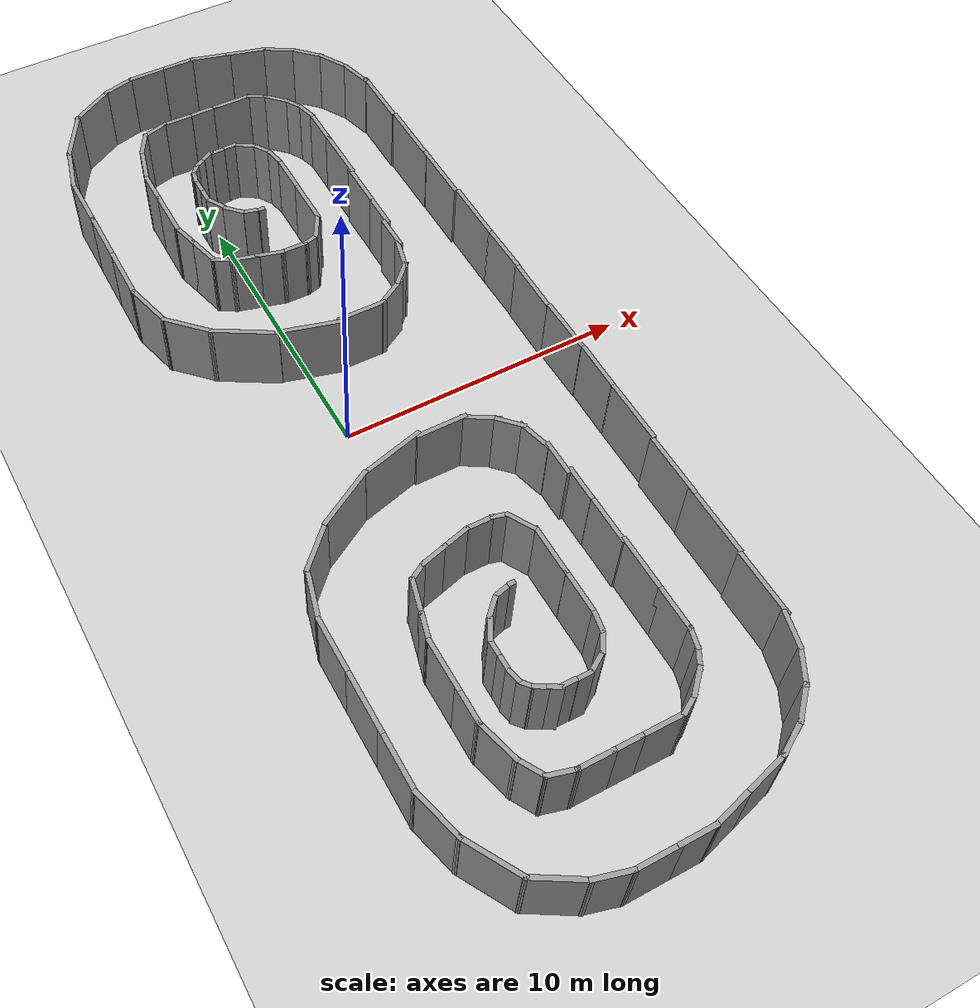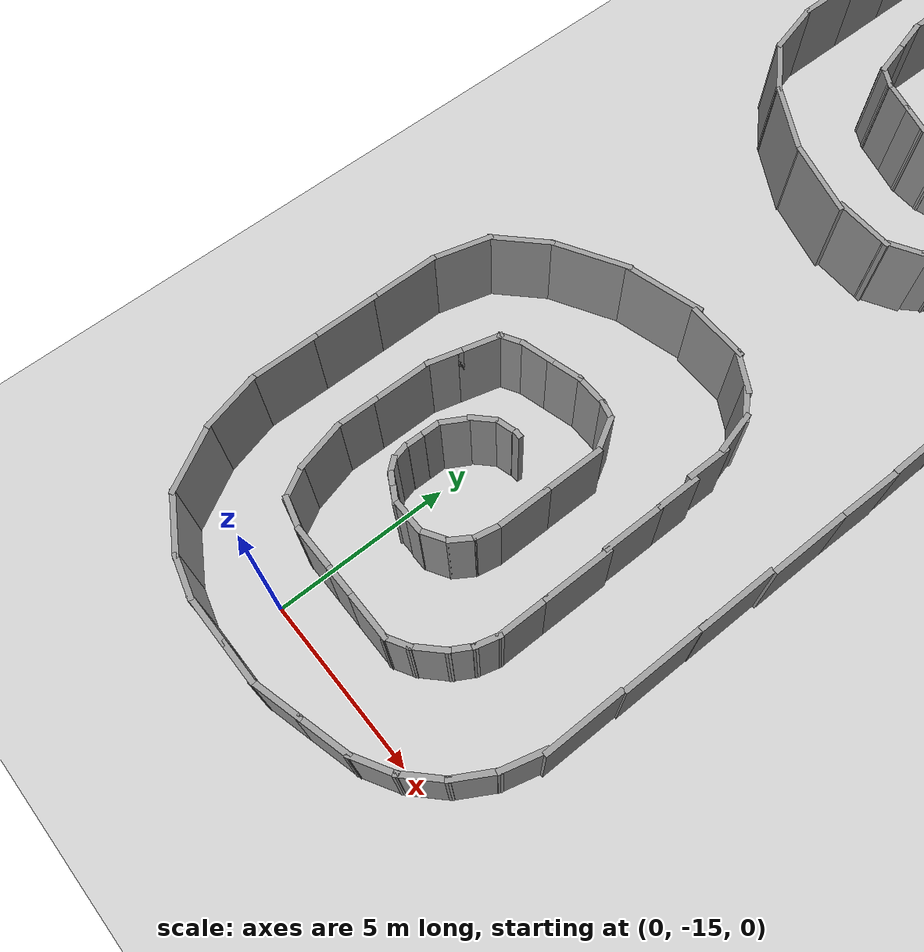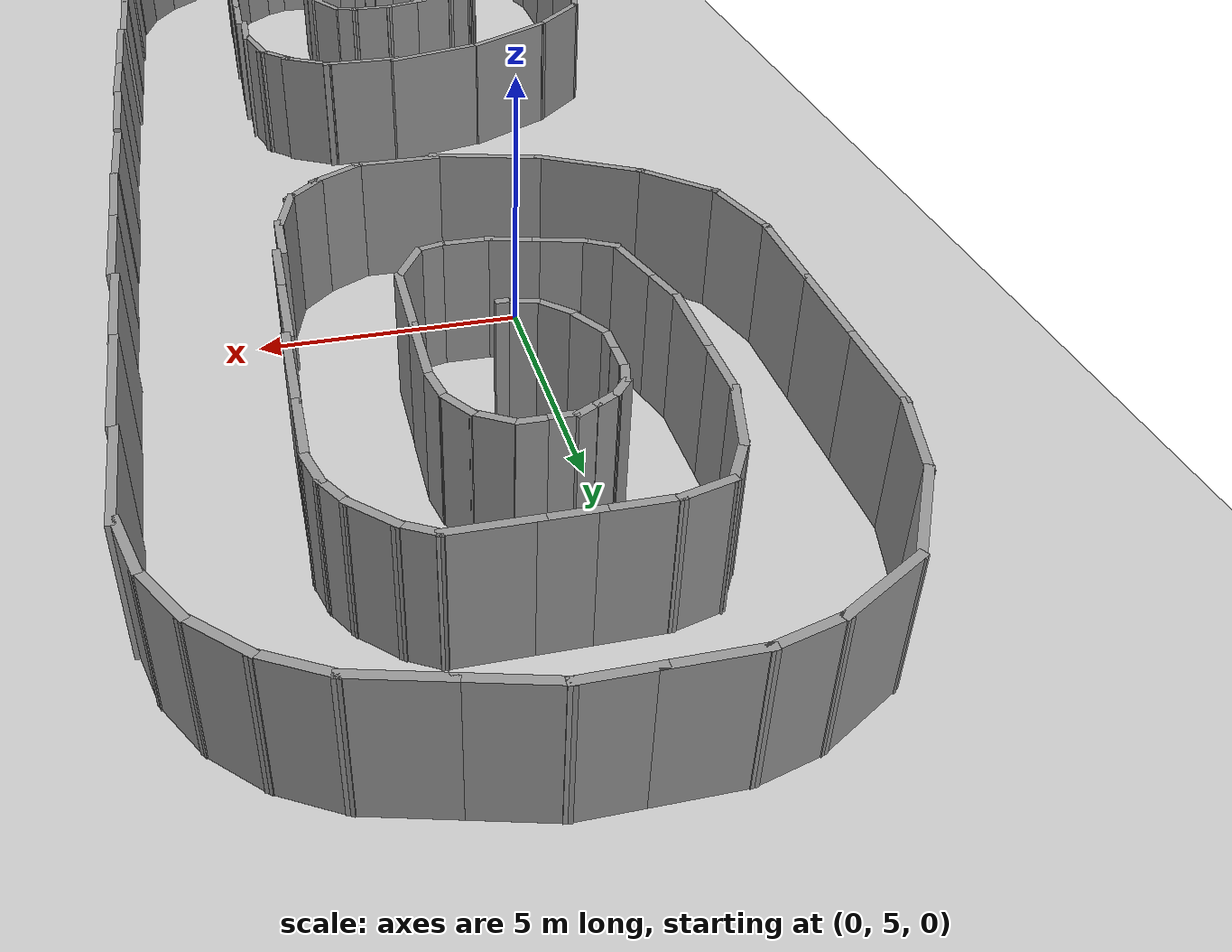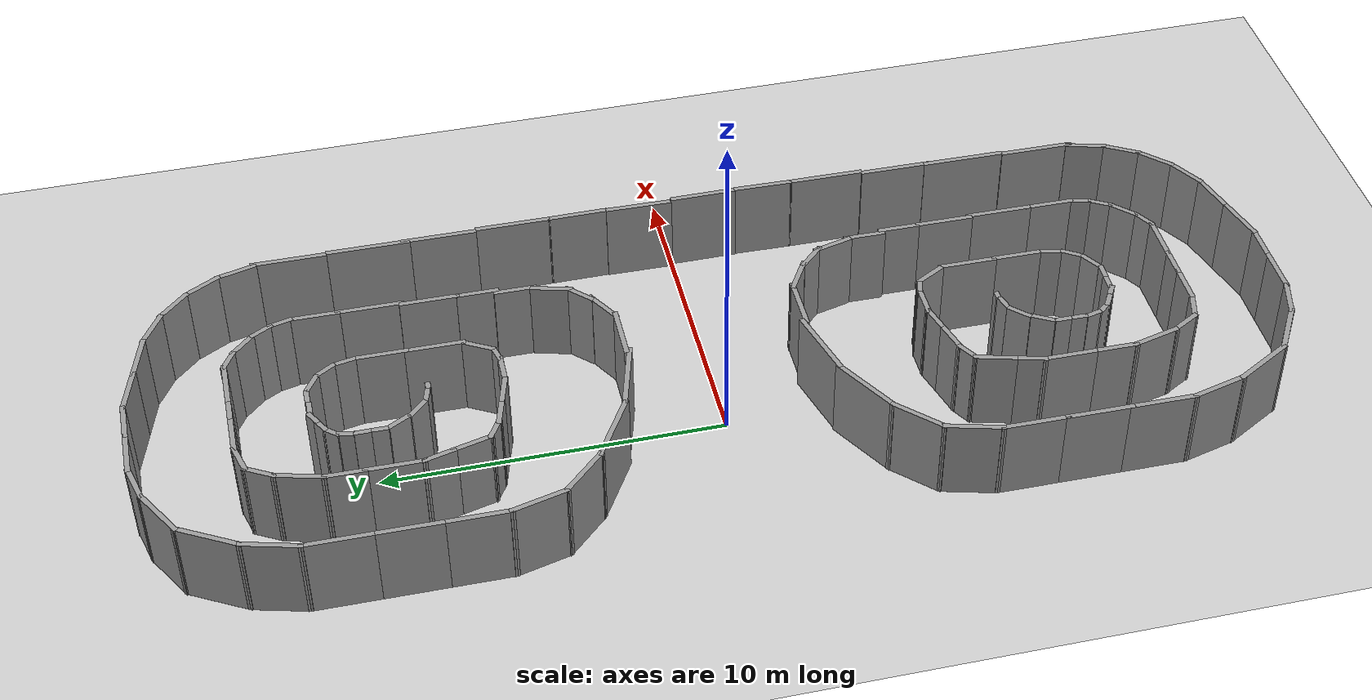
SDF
<sdf version="1.6">
 <world name="default">
  <light name="sun" type="directional">
   <pose>0 0 10 0 -0 0</pose>
   <diffuse>0.8 0.8 0.8 1</diffuse>
   <specular>0.2 0.2 0.2 1</specular>
   <attenuation>
    <range>1000</range>
    <constant>0.9</constant>
    <linear>0.01</linear>
    <quadratic>0.001</quadratic>
   </attenuation>
   <direction>-0.5 0.1 -0.9</direction>
  </light>
  <model name="ground_plane">
   <static>1</static>
   <link name="link">
    <collision name="collision">
     <geometry><plane><normal>0 0 1</normal><size>100 100</size></plane></geometry>
     <surface><friction><ode><mu>100</mu><mu2>50</mu2></ode></friction></surface>
    </collision>
    <visual name="visual">
     <cast_shadows>0</cast_shadows>
     <geometry><plane><normal>0 0 1</normal><size>100 100</size></plane></geometry>
     <material>
      <script><uri>file://media/materials/scripts/gazebo.material</uri><name>Gazebo/Grey</name></script>
     </material>
    </visual>
   </link>
  </model>
  <gravity>0 0 -9.8</gravity>
  <magnetic_field>6e-06 2.3e-05 -4.2e-05</magnetic_field>
  <atmosphere type="adiabatic"/>
  <physics name="default_physics" default="0" type="ode">
   <max_step_size>0.001</max_step_size>
   <real_time_factor>1</real_time_factor>
   <real_time_update_rate>1000</real_time_update_rate>
  </physics>
  <scene><ambient>0.4 0.4 0.4 1</ambient><background>0.7 0.7 0.7 1</background><shadows>1</shadows></scene>
  <audio><device>default</device></audio>
  <spherical_coordinates>
   <surface_model>EARTH_WGS84</surface_model>
   <latitude_deg>0</latitude_deg>
   <longitude_deg>0</longitude_deg>
   <elevation>0</elevation>
   <heading_deg>0</heading_deg>
  </spherical_coordinates>
  <model name="c-Snail_update">
   <link name="Wall_14">
    <pose>-5.26527 -5.8787 0 0 0 -0.010393</pose>
    <visual name="Wall_14_Visual">
     <pose>0 0 1.25 0 -0 0</pose>
     <geometry><box><size>2 0.15 2.5</size></box></geometry>
     <material>
      <script><uri>file://media/materials/scripts/gazebo.material</uri><name>Gazebo/Grey</name></script>
      <ambient>1 1 1 1</ambient>
     </material>
     <meta><layer>0</layer></meta>
    </visual>
    <collision name="Wall_14_Collision">
     <pose>0 0 1.25 0 -0 0</pose>
     <geometry><box><size>2 0.15 2.5</size></box></geometry>
     <surface>
      <friction>
       <ode><mu>1</mu><mu2>1</mu2><fdir1>0 0 0</fdir1><slip1>0</slip1><slip2>0</slip2></ode>
       <torsional>
        <coefficient>1</coefficient>
        <patch_radius>0</patch_radius>
        <surface_radius>0</surface_radius>
        <use_patch_radius>1</use_patch_radius>
        <ode><slip>0</slip></ode>
       </torsional>
      </friction>
      <bounce><restitution_coefficient>0</restitution_coefficient><threshold>1e+06</threshold></bounce>
      <contact>
       <collide_without_contact>0</collide_without_contact>
       <collide_without_contact_bitmask>1</collide_without_contact_bitmask>
       <collide_bitmask>1</collide_bitmask>
       <ode>
        <soft_cfm>0</soft_cfm>
        <soft_erp>0.2</soft_erp>
        <kp>1e+13</kp>
        <kd>1</kd>
        <max_vel>0.01</max_vel>
        <min_depth>0</min_depth>
       </ode>
       <bullet>
        <split_impulse>1</split_impulse>
        <split_impulse_penetration_threshold>-0.01</split_impulse_penetration_threshold>
        <soft_cfm>0</soft_cfm>
        <soft_erp>0.2</soft_erp>
        <kp>1e+13</kp>
        <kd>1</kd>
       </bullet>
      </contact>
     </surface>
    </collision>
   </link>
   <link name="Wall_15">
    <pose>-3.40013 -5.89719 0 0 -0 0.01305</pose>
    <visual name="Wall_15_Visual">
     <pose>0 0 1.25 0 -0 0</pose>
     <geometry><box><size>1.77919 0.15 2.5</size></box></geometry>
     <material>
      <script><uri>file://media/materials/scripts/gazebo.material</uri><name>Gazebo/Grey</name></script>
      <ambient>1 1 1 1</ambient>
     </material>
     <meta><layer>0</layer></meta>
    </visual>
    <collision name="Wall_15_Collision">
     <pose>0 0 1.25 0 -0 0</pose>
     <geometry><box><size>1.77919 0.15 2.5</size></box></geometry>
     <surface>
      <friction>
       <ode><mu>1</mu><mu2>1</mu2><fdir1>0 0 0</fdir1><slip1>0</slip1><slip2>0</slip2></ode>
       <torsional>
        <coefficient>1</coefficient>
        <patch_radius>0</patch_radius>
        <surface_radius>0</surface_radius>
        <use_patch_radius>1</use_patch_radius>
        <ode><slip>0</slip></ode>
       </torsional>
      </friction>
      <bounce><restitution_coefficient>0</restitution_coefficient><threshold>1e+06</threshold></bounce>
      <contact>
       <collide_without_contact>0</collide_without_contact>
       <collide_without_contact_bitmask>1</collide_without_contact_bitmask>
       <collide_bitmask>1</collide_bitmask>
       <ode>
        <soft_cfm>0</soft_cfm>
        <soft_erp>0.2</soft_erp>
        <kp>1e+13</kp>
        <kd>1</kd>
        <max_vel>0.01</max_vel>
        <min_depth>0</min_depth>
       </ode>
       <bullet>
        <split_impulse>1</split_impulse>
        <split_impulse_penetration_threshold>-0.01</split_impulse_penetration_threshold>
        <soft_cfm>0</soft_cfm>
        <soft_erp>0.2</soft_erp>
        <kp>1e+13</kp>
        <kd>1</kd>
       </bullet>
      </contact>
     </surface>
    </collision>
   </link>
   <link name="Wall_18">
    <pose>-1.42808 -5.88586 0 0 -0 0</pose>
    <visual name="Wall_18_Visual">
     <pose>0 0 1.25 0 -0 0</pose>
     <geometry><box><size>2.25 0.15 2.5</size></box></geometry>
     <material>
      <script><uri>file://media/materials/scripts/gazebo.material</uri><name>Gazebo/Grey</name></script>
      <ambient>1 1 1 1</ambient>
     </material>
     <meta><layer>0</layer></meta>
    </visual>
    <collision name="Wall_18_Collision">
     <pose>0 0 1.25 0 -0 0</pose>
     <geometry><box><size>2.25 0.15 2.5</size></box></geometry>
     <surface>
      <friction>
       <ode><mu>1</mu><mu2>1</mu2><fdir1>0 0 0</fdir1><slip1>0</slip1><slip2>0</slip2></ode>
       <torsional>
        <coefficient>1</coefficient>
        <patch_radius>0</patch_radius>
        <surface_radius>0</surface_radius>
        <use_patch_radius>1</use_patch_radius>
        <ode><slip>0</slip></ode>
       </torsional>
      </friction>
      <bounce><restitution_coefficient>0</restitution_coefficient><threshold>1e+06</threshold></bounce>
      <contact>
       <collide_without_contact>0</collide_without_contact>
       <collide_without_contact_bitmask>1</collide_without_contact_bitmask>
       <collide_bitmask>1</collide_bitmask>
       <ode>
        <soft_cfm>0</soft_cfm>
        <soft_erp>0.2</soft_erp>
        <kp>1e+13</kp>
        <kd>1</kd>
        <max_vel>0.01</max_vel>
        <min_depth>0</min_depth>
       </ode>
       <bullet>
        <split_impulse>1</split_impulse>
        <split_impulse_penetration_threshold>-0.01</split_impulse_penetration_threshold>
        <soft_cfm>0</soft_cfm>
        <soft_erp>0.2</soft_erp>
        <kp>1e+13</kp>
        <kd>1</kd>
       </bullet>
      </contact>
     </surface>
    </collision>
   </link>
   <link name="Wall_19">
    <pose>0.800174 -5.81597 0 0 -0 0</pose>
    <visual name="Wall_19_Visual">
     <pose>0 0 1.25 0 -0 0</pose>
     <geometry><box><size>2.25 0.15 2.5</size></box></geometry>
     <material>
      <script><uri>file://media/materials/scripts/gazebo.material</uri><name>Gazebo/Grey</name></script>
      <ambient>1 1 1 1</ambient>
     </material>
     <meta><layer>0</layer></meta>
    </visual>
    <collision name="Wall_19_Collision">
     <pose>0 0 1.25 0 -0 0</pose>
     <geometry><box><size>2.25 0.15 2.5</size></box></geometry>
     <surface>
      <friction>
       <ode><mu>1</mu><mu2>1</mu2><fdir1>0 0 0</fdir1><slip1>0</slip1><slip2>0</slip2></ode>
       <torsional>
        <coefficient>1</coefficient>
        <patch_radius>0</patch_radius>
        <surface_radius>0</surface_radius>
        <use_patch_radius>1</use_patch_radius>
        <ode><slip>0</slip></ode>
       </torsional>
      </friction>
      <bounce><restitution_coefficient>0</restitution_coefficient><threshold>1e+06</threshold></bounce>
      <contact>
       <collide_without_contact>0</collide_without_contact>
       <collide_without_contact_bitmask>1</collide_without_contact_bitmask>
       <collide_bitmask>1</collide_bitmask>
       <ode>
        <soft_cfm>0</soft_cfm>
        <soft_erp>0.2</soft_erp>
        <kp>1e+13</kp>
        <kd>1</kd>
        <max_vel>0.01</max_vel>
        <min_depth>0</min_depth>
       </ode>
       <bullet>
        <split_impulse>1</split_impulse>
        <split_impulse_penetration_threshold>-0.01</split_impulse_penetration_threshold>
        <soft_cfm>0</soft_cfm>
        <soft_erp>0.2</soft_erp>
        <kp>1e+13</kp>
        <kd>1</kd>
       </bullet>
      </contact>
     </surface>
    </collision>
   </link>
   <link name="Wall_20">
    <pose>2.90214 -5.80096 0 0 -0 0</pose>
    <visual name="Wall_20_Visual">
     <pose>0 0 1.25 0 -0 0</pose>
     <geometry><box><size>2.5 0.15 2.5</size></box></geometry>
     <material>
      <script><uri>file://media/materials/scripts/gazebo.material</uri><name>Gazebo/Grey</name></script>
      <ambient>1 1 1 1</ambient>
     </material>
     <meta><layer>0</layer></meta>
    </visual>
    <collision name="Wall_20_Collision">
     <pose>0 0 1.25 0 -0 0</pose>
     <geometry><box><size>2.5 0.15 2.5</size></box></geometry>
     <surface>
      <friction>
       <ode><mu>1</mu><mu2>1</mu2><fdir1>0 0 0</fdir1><slip1>0</slip1><slip2>0</slip2></ode>
       <torsional>
        <coefficient>1</coefficient>
        <patch_radius>0</patch_radius>
        <surface_radius>0</surface_radius>
        <use_patch_radius>1</use_patch_radius>
        <ode><slip>0</slip></ode>
       </torsional>
      </friction>
      <bounce><restitution_coefficient>0</restitution_coefficient><threshold>1e+06</threshold></bounce>
      <contact>
       <collide_without_contact>0</collide_without_contact>
       <collide_without_contact_bitmask>1</collide_without_contact_bitmask>
       <collide_bitmask>1</collide_bitmask>
       <ode>
        <soft_cfm>0</soft_cfm>
        <soft_erp>0.2</soft_erp>
        <kp>1e+13</kp>
        <kd>1</kd>
        <max_vel>0.01</max_vel>
        <min_depth>0</min_depth>
       </ode>
       <bullet>
        <split_impulse>1</split_impulse>
        <split_impulse_penetration_threshold>-0.01</split_impulse_penetration_threshold>
        <soft_cfm>0</soft_cfm>
        <soft_erp>0.2</soft_erp>
        <kp>1e+13</kp>
        <kd>1</kd>
       </bullet>
      </contact>
     </surface>
    </collision>
   </link>
   <link name="Wall_21">
    <pose>5.25228 -5.75509 0 0 -0 0</pose>
    <visual name="Wall_21_Visual">
     <pose>0 0 1.25 0 -0 0</pose>
     <geometry><box><size>2.25 0.15 2.5</size></box></geometry>
     <material>
      <script><uri>file://media/materials/scripts/gazebo.material</uri><name>Gazebo/Grey</name></script>
      <ambient>1 1 1 1</ambient>
     </material>
     <meta><layer>0</layer></meta>
    </visual>
    <collision name="Wall_21_Collision">
     <pose>0 0 1.25 0 -0 0</pose>
     <geometry><box><size>2.25 0.15 2.5</size></box></geometry>
     <surface>
      <friction>
       <ode><mu>1</mu><mu2>1</mu2><fdir1>0 0 0</fdir1><slip1>0</slip1><slip2>0</slip2></ode>
       <torsional>
        <coefficient>1</coefficient>
        <patch_radius>0</patch_radius>
        <surface_radius>0</surface_radius>
        <use_patch_radius>1</use_patch_radius>
        <ode><slip>0</slip></ode>
       </torsional>
      </friction>
      <bounce><restitution_coefficient>0</restitution_coefficient><threshold>1e+06</threshold></bounce>
      <contact>
       <collide_without_contact>0</collide_without_contact>
       <collide_without_contact_bitmask>1</collide_without_contact_bitmask>
       <collide_bitmask>1</collide_bitmask>
       <ode>
        <soft_cfm>0</soft_cfm>
        <soft_erp>0.2</soft_erp>
        <kp>1e+13</kp>
        <kd>1</kd>
        <max_vel>0.01</max_vel>
        <min_depth>0</min_depth>
       </ode>
       <bullet>
        <split_impulse>1</split_impulse>
        <split_impulse_penetration_threshold>-0.01</split_impulse_penetration_threshold>
        <soft_cfm>0</soft_cfm>
        <soft_erp>0.2</soft_erp>
        <kp>1e+13</kp>
        <kd>1</kd>
       </bullet>
      </contact>
     </surface>
    </collision>
   </link>
   <link name="Wall_22">
    <pose>6.78859 -5.56286 0 0 -0 0.261799</pose>
    <visual name="Wall_22_Visual">
     <pose>0 0 1.25 0 -0 0</pose>
     <geometry><box><size>1.25 0.15 2.5</size></box></geometry>
     <material>
      <script><uri>file://media/materials/scripts/gazebo.material</uri><name>Gazebo/Grey</name></script>
      <ambient>1 1 1 1</ambient>
     </material>
     <meta><layer>0</layer></meta>
    </visual>
    <collision name="Wall_22_Collision">
     <pose>0 0 1.25 0 -0 0</pose>
     <geometry><box><size>1.25 0.15 2.5</size></box></geometry>
     <surface>
      <friction>
       <ode><mu>1</mu><mu2>1</mu2><fdir1>0 0 0</fdir1><slip1>0</slip1><slip2>0</slip2></ode>
       <torsional>
        <coefficient>1</coefficient>
        <patch_radius>0</patch_radius>
        <surface_radius>0</surface_radius>
        <use_patch_radius>1</use_patch_radius>
        <ode><slip>0</slip></ode>
       </torsional>
      </friction>
      <bounce><restitution_coefficient>0</restitution_coefficient><threshold>1e+06</threshold></bounce>
      <contact>
       <collide_without_contact>0</collide_without_contact>
       <collide_without_contact_bitmask>1</collide_without_contact_bitmask>
       <collide_bitmask>1</collide_bitmask>
       <ode>
        <soft_cfm>0</soft_cfm>
        <soft_erp>0.2</soft_erp>
        <kp>1e+13</kp>
        <kd>1</kd>
        <max_vel>0.01</max_vel>
        <min_depth>0</min_depth>
       </ode>
       <bullet>
        <split_impulse>1</split_impulse>
        <split_impulse_penetration_threshold>-0.01</split_impulse_penetration_threshold>
        <soft_cfm>0</soft_cfm>
        <soft_erp>0.2</soft_erp>
        <kp>1e+13</kp>
        <kd>1</kd>
       </bullet>
      </contact>
     </surface>
    </collision>
   </link>
   <link name="Wall_23">
    <pose>7.79617 -5.14551 0 0 -0 0.523599</pose>
    <visual name="Wall_23_Visual">
     <pose>0 0 1.25 0 -0 0</pose>
     <geometry><box><size>1.25 0.15 2.5</size></box></geometry>
     <material>
      <script><uri>file://media/materials/scripts/gazebo.material</uri><name>Gazebo/Grey</name></script>
      <ambient>1 1 1 1</ambient>
     </material>
     <meta><layer>0</layer></meta>
    </visual>
    <collision name="Wall_23_Collision">
     <pose>0 0 1.25 0 -0 0</pose>
     <geometry><box><size>1.25 0.15 2.5</size></box></geometry>
     <surface>
      <friction>
       <ode><mu>1</mu><mu2>1</mu2><fdir1>0 0 0</fdir1><slip1>0</slip1><slip2>0</slip2></ode>
       <torsional>
        <coefficient>1</coefficient>
        <patch_radius>0</patch_radius>
        <surface_radius>0</surface_radius>
        <use_patch_radius>1</use_patch_radius>
        <ode><slip>0</slip></ode>
       </torsional>
      </friction>
      <bounce><restitution_coefficient>0</restitution_coefficient><threshold>1e+06</threshold></bounce>
      <contact>
       <collide_without_contact>0</collide_without_contact>
       <collide_without_contact_bitmask>1</collide_without_contact_bitmask>
       <collide_bitmask>1</collide_bitmask>
       <ode>
        <soft_cfm>0</soft_cfm>
        <soft_erp>0.2</soft_erp>
        <kp>1e+13</kp>
        <kd>1</kd>
        <max_vel>0.01</max_vel>
        <min_depth>0</min_depth>
       </ode>
       <bullet>
        <split_impulse>1</split_impulse>
        <split_impulse_penetration_threshold>-0.01</split_impulse_penetration_threshold>
        <soft_cfm>0</soft_cfm>
        <soft_erp>0.2</soft_erp>
        <kp>1e+13</kp>
        <kd>1</kd>
       </bullet>
      </contact>
     </surface>
    </collision>
   </link>
   <link name="Wall_24">
    <pose>8.66139 -4.4816 0 0 -0 0.785398</pose>
    <visual name="Wall_24_Visual">
     <pose>0 0 1.25 0 -0 0</pose>
     <geometry><box><size>1.25 0.15 2.5</size></box></geometry>
     <material>
      <script><uri>file://media/materials/scripts/gazebo.material</uri><name>Gazebo/Grey</name></script>
      <ambient>1 1 1 1</ambient>
     </material>
     <meta><layer>0</layer></meta>
    </visual>
    <collision name="Wall_24_Collision">
     <pose>0 0 1.25 0 -0 0</pose>
     <geometry><box><size>1.25 0.15 2.5</size></box></geometry>
     <surface>
      <friction>
       <ode><mu>1</mu><mu2>1</mu2><fdir1>0 0 0</fdir1><slip1>0</slip1><slip2>0</slip2></ode>
       <torsional>
        <coefficient>1</coefficient>
        <patch_radius>0</patch_radius>
        <surface_radius>0</surface_radius>
        <use_patch_radius>1</use_patch_radius>
        <ode><slip>0</slip></ode>
       </torsional>
      </friction>
      <bounce><restitution_coefficient>0</restitution_coefficient><threshold>1e+06</threshold></bounce>
      <contact>
       <collide_without_contact>0</collide_without_contact>
       <collide_without_contact_bitmask>1</collide_without_contact_bitmask>
       <collide_bitmask>1</collide_bitmask>
       <ode>
        <soft_cfm>0</soft_cfm>
        <soft_erp>0.2</soft_erp>
        <kp>1e+13</kp>
        <kd>1</kd>
        <max_vel>0.01</max_vel>
        <min_depth>0</min_depth>
       </ode>
       <bullet>
        <split_impulse>1</split_impulse>
        <split_impulse_penetration_threshold>-0.01</split_impulse_penetration_threshold>
        <soft_cfm>0</soft_cfm>
        <soft_erp>0.2</soft_erp>
        <kp>1e+13</kp>
        <kd>1</kd>
       </bullet>
      </contact>
     </surface>
    </collision>
   </link>
   <link name="Wall_25">
    <pose>9.3253 -3.61638 0 0 -0 1.0472</pose>
    <visual name="Wall_25_Visual">
     <pose>0 0 1.25 0 -0 0</pose>
     <geometry><box><size>1.25 0.15 2.5</size></box></geometry>
     <material>
      <script><uri>file://media/materials/scripts/gazebo.material</uri><name>Gazebo/Grey</name></script>
      <ambient>1 1 1 1</ambient>
     </material>
     <meta><layer>0</layer></meta>
    </visual>
    <collision name="Wall_25_Collision">
     <pose>0 0 1.25 0 -0 0</pose>
     <geometry><box><size>1.25 0.15 2.5</size></box></geometry>
     <surface>
      <friction>
       <ode><mu>1</mu><mu2>1</mu2><fdir1>0 0 0</fdir1><slip1>0</slip1><slip2>0</slip2></ode>
       <torsional>
        <coefficient>1</coefficient>
        <patch_radius>0</patch_radius>
        <surface_radius>0</surface_radius>
        <use_patch_radius>1</use_patch_radius>
        <ode><slip>0</slip></ode>
       </torsional>
      </friction>
      <bounce><restitution_coefficient>0</restitution_coefficient><threshold>1e+06</threshold></bounce>
      <contact>
       <collide_without_contact>0</collide_without_contact>
       <collide_without_contact_bitmask>1</collide_without_contact_bitmask>
       <collide_bitmask>1</collide_bitmask>
       <ode>
        <soft_cfm>0</soft_cfm>
        <soft_erp>0.2</soft_erp>
        <kp>1e+13</kp>
        <kd>1</kd>
        <max_vel>0.01</max_vel>
        <min_depth>0</min_depth>
       </ode>
       <bullet>
        <split_impulse>1</split_impulse>
        <split_impulse_penetration_threshold>-0.01</split_impulse_penetration_threshold>
        <soft_cfm>0</soft_cfm>
        <soft_erp>0.2</soft_erp>
        <kp>1e+13</kp>
        <kd>1</kd>
       </bullet>
      </contact>
     </surface>
    </collision>
   </link>
   <link name="Wall_26">
    <pose>9.775 -2.48806 0 0 -0 1.309</pose>
    <visual name="Wall_26_Visual">
     <pose>0 0 1.25 0 -0 0</pose>
     <geometry><box><size>1.5 0.15 2.5</size></box></geometry>
     <material>
      <script><uri>file://media/materials/scripts/gazebo.material</uri><name>Gazebo/Grey</name></script>
      <ambient>1 1 1 1</ambient>
     </material>
     <meta><layer>0</layer></meta>
    </visual>
    <collision name="Wall_26_Collision">
     <pose>0 0 1.25 0 -0 0</pose>
     <geometry><box><size>1.5 0.15 2.5</size></box></geometry>
     <surface>
      <friction>
       <ode><mu>1</mu><mu2>1</mu2><fdir1>0 0 0</fdir1><slip1>0</slip1><slip2>0</slip2></ode>
       <torsional>
        <coefficient>1</coefficient>
        <patch_radius>0</patch_radius>
        <surface_radius>0</surface_radius>
        <use_patch_radius>1</use_patch_radius>
        <ode><slip>0</slip></ode>
       </torsional>
      </friction>
      <bounce><restitution_coefficient>0</restitution_coefficient><threshold>1e+06</threshold></bounce>
      <contact>
       <collide_without_contact>0</collide_without_contact>
       <collide_without_contact_bitmask>1</collide_without_contact_bitmask>
       <collide_bitmask>1</collide_bitmask>
       <ode>
        <soft_cfm>0</soft_cfm>
        <soft_erp>0.2</soft_erp>
        <kp>1e+13</kp>
        <kd>1</kd>
        <max_vel>0.01</max_vel>
        <min_depth>0</min_depth>
       </ode>
       <bullet>
        <split_impulse>1</split_impulse>
        <split_impulse_penetration_threshold>-0.01</split_impulse_penetration_threshold>
        <soft_cfm>0</soft_cfm>
        <soft_erp>0.2</soft_erp>
        <kp>1e+13</kp>
        <kd>1</kd>
       </bullet>
      </contact>
     </surface>
    </collision>
   </link>
   <link name="Wall_27">
    <pose>10.1244 -1.18406 0 0 -0 1.309</pose>
    <visual name="Wall_27_Visual">
     <pose>0 0 1.25 0 -0 0</pose>
     <geometry><box><size>1.5 0.15 2.5</size></box></geometry>
     <material>
      <script><uri>file://media/materials/scripts/gazebo.material</uri><name>Gazebo/Grey</name></script>
      <ambient>1 1 1 1</ambient>
     </material>
     <meta><layer>0</layer></meta>
    </visual>
    <collision name="Wall_27_Collision">
     <pose>0 0 1.25 0 -0 0</pose>
     <geometry><box><size>1.5 0.15 2.5</size></box></geometry>
     <surface>
      <friction>
       <ode><mu>1</mu><mu2>1</mu2><fdir1>0 0 0</fdir1><slip1>0</slip1><slip2>0</slip2></ode>
       <torsional>
        <coefficient>1</coefficient>
        <patch_radius>0</patch_radius>
        <surface_radius>0</surface_radius>
        <use_patch_radius>1</use_patch_radius>
        <ode><slip>0</slip></ode>
       </torsional>
      </friction>
      <bounce><restitution_coefficient>0</restitution_coefficient><threshold>1e+06</threshold></bounce>
      <contact>
       <collide_without_contact>0</collide_without_contact>
       <collide_without_contact_bitmask>1</collide_without_contact_bitmask>
       <collide_bitmask>1</collide_bitmask>
       <ode>
        <soft_cfm>0</soft_cfm>
        <soft_erp>0.2</soft_erp>
        <kp>1e+13</kp>
        <kd>1</kd>
        <max_vel>0.01</max_vel>
        <min_depth>0</min_depth>
       </ode>
       <bullet>
        <split_impulse>1</split_impulse>
        <split_impulse_penetration_threshold>-0.01</split_impulse_penetration_threshold>
        <soft_cfm>0</soft_cfm>
        <soft_erp>0.2</soft_erp>
        <kp>1e+13</kp>
        <kd>1</kd>
       </bullet>
      </contact>
     </surface>
    </collision>
   </link>
   <link name="Wall_28">
    <pose>10.2991 0.017937 0 0 -0 1.5708</pose>
    <visual name="Wall_28_Visual">
     <pose>0 0 1.25 0 -0 0</pose>
     <geometry><box><size>1.25 0.15 2.5</size></box></geometry>
     <material>
      <script><uri>file://media/materials/scripts/gazebo.material</uri><name>Gazebo/Grey</name></script>
      <ambient>1 1 1 1</ambient>
     </material>
     <meta><layer>0</layer></meta>
    </visual>
    <collision name="Wall_28_Collision">
     <pose>0 0 1.25 0 -0 0</pose>
     <geometry><box><size>1.25 0.15 2.5</size></box></geometry>
     <surface>
      <friction>
       <ode><mu>1</mu><mu2>1</mu2><fdir1>0 0 0</fdir1><slip1>0</slip1><slip2>0</slip2></ode>
       <torsional>
        <coefficient>1</coefficient>
        <patch_radius>0</patch_radius>
        <surface_radius>0</surface_radius>
        <use_patch_radius>1</use_patch_radius>
        <ode><slip>0</slip></ode>
       </torsional>
      </friction>
      <bounce><restitution_coefficient>0</restitution_coefficient><threshold>1e+06</threshold></bounce>
      <contact>
       <collide_without_contact>0</collide_without_contact>
       <collide_without_contact_bitmask>1</collide_without_contact_bitmask>
       <collide_bitmask>1</collide_bitmask>
       <ode>
        <soft_cfm>0</soft_cfm>
        <soft_erp>0.2</soft_erp>
        <kp>1e+13</kp>
        <kd>1</kd>
        <max_vel>0.01</max_vel>
        <min_depth>0</min_depth>
       </ode>
       <bullet>
        <split_impulse>1</split_impulse>
        <split_impulse_penetration_threshold>-0.01</split_impulse_penetration_threshold>
        <soft_cfm>0</soft_cfm>
        <soft_erp>0.2</soft_erp>
        <kp>1e+13</kp>
        <kd>1</kd>
       </bullet>
      </contact>
     </surface>
    </collision>
   </link>
   <link name="Wall_29">
    <pose>10.2991 1.24294 0 0 -0 1.5708</pose>
    <visual name="Wall_29_Visual">
     <pose>0 0 1.25 0 -0 0</pose>
     <geometry><box><size>1.5 0.15 2.5</size></box></geometry>
     <material>
      <script><uri>file://media/materials/scripts/gazebo.material</uri><name>Gazebo/Grey</name></script>
      <ambient>1 1 1 1</ambient>
     </material>
     <meta><layer>0</layer></meta>
    </visual>
    <collision name="Wall_29_Collision">
     <pose>0 0 1.25 0 -0 0</pose>
     <geometry><box><size>1.5 0.15 2.5</size></box></geometry>
     <surface>
      <friction>
       <ode><mu>1</mu><mu2>1</mu2><fdir1>0 0 0</fdir1><slip1>0</slip1><slip2>0</slip2></ode>
       <torsional>
        <coefficient>1</coefficient>
        <patch_radius>0</patch_radius>
        <surface_radius>0</surface_radius>
        <use_patch_radius>1</use_patch_radius>
        <ode><slip>0</slip></ode>
       </torsional>
      </friction>
      <bounce><restitution_coefficient>0</restitution_coefficient><threshold>1e+06</threshold></bounce>
      <contact>
       <collide_without_contact>0</collide_without_contact>
       <collide_without_contact_bitmask>1</collide_without_contact_bitmask>
       <collide_bitmask>1</collide_bitmask>
       <ode>
        <soft_cfm>0</soft_cfm>
        <soft_erp>0.2</soft_erp>
        <kp>1e+13</kp>
        <kd>1</kd>
        <max_vel>0.01</max_vel>
        <min_depth>0</min_depth>
       </ode>
       <bullet>
        <split_impulse>1</split_impulse>
        <split_impulse_penetration_threshold>-0.01</split_impulse_penetration_threshold>
        <soft_cfm>0</soft_cfm>
        <soft_erp>0.2</soft_erp>
        <kp>1e+13</kp>
        <kd>1</kd>
       </bullet>
      </contact>
     </surface>
    </collision>
   </link>
   <link name="Wall_30">
    <pose>10.1568 2.4492 0 0 -0 1.8326</pose>
    <visual name="Wall_30_Visual">
     <pose>0 0 1.25 0 -0 0</pose>
     <geometry><box><size>1.25 0.15 2.5</size></box></geometry>
     <material>
      <script><uri>file://media/materials/scripts/gazebo.material</uri><name>Gazebo/Grey</name></script>
      <ambient>1 1 1 1</ambient>
     </material>
     <meta><layer>0</layer></meta>
    </visual>
    <collision name="Wall_30_Collision">
     <pose>0 0 1.25 0 -0 0</pose>
     <geometry><box><size>1.25 0.15 2.5</size></box></geometry>
     <surface>
      <friction>
       <ode><mu>1</mu><mu2>1</mu2><fdir1>0 0 0</fdir1><slip1>0</slip1><slip2>0</slip2></ode>
       <torsional>
        <coefficient>1</coefficient>
        <patch_radius>0</patch_radius>
        <surface_radius>0</surface_radius>
        <use_patch_radius>1</use_patch_radius>
        <ode><slip>0</slip></ode>
       </torsional>
      </friction>
      <bounce><restitution_coefficient>0</restitution_coefficient><threshold>1e+06</threshold></bounce>
      <contact>
       <collide_without_contact>0</collide_without_contact>
       <collide_without_contact_bitmask>1</collide_without_contact_bitmask>
       <collide_bitmask>1</collide_bitmask>
       <ode>
        <soft_cfm>0</soft_cfm>
        <soft_erp>0.2</soft_erp>
        <kp>1e+13</kp>
        <kd>1</kd>
        <max_vel>0.01</max_vel>
        <min_depth>0</min_depth>
       </ode>
       <bullet>
        <split_impulse>1</split_impulse>
        <split_impulse_penetration_threshold>-0.01</split_impulse_penetration_threshold>
        <soft_cfm>0</soft_cfm>
        <soft_erp>0.2</soft_erp>
        <kp>1e+13</kp>
        <kd>1</kd>
       </bullet>
      </contact>
     </surface>
    </collision>
   </link>
   <link name="Wall_31">
    <pose>9.61441 3.67328 0 0 -0 2.0944</pose>
    <visual name="Wall_31_Visual">
     <pose>0 0 1.25 0 -0 0</pose>
     <geometry><box><size>1.75 0.15 2.5</size></box></geometry>
     <material>
      <script><uri>file://media/materials/scripts/gazebo.material</uri><name>Gazebo/Grey</name></script>
      <ambient>1 1 1 1</ambient>
     </material>
     <meta><layer>0</layer></meta>
    </visual>
    <collision name="Wall_31_Collision">
     <pose>0 0 1.25 0 -0 0</pose>
     <geometry><box><size>1.75 0.15 2.5</size></box></geometry>
     <surface>
      <friction>
       <ode><mu>1</mu><mu2>1</mu2><fdir1>0 0 0</fdir1><slip1>0</slip1><slip2>0</slip2></ode>
       <torsional>
        <coefficient>1</coefficient>
        <patch_radius>0</patch_radius>
        <surface_radius>0</surface_radius>
        <use_patch_radius>1</use_patch_radius>
        <ode><slip>0</slip></ode>
       </torsional>
      </friction>
      <bounce><restitution_coefficient>0</restitution_coefficient><threshold>1e+06</threshold></bounce>
      <contact>
       <collide_without_contact>0</collide_without_contact>
       <collide_without_contact_bitmask>1</collide_without_contact_bitmask>
       <collide_bitmask>1</collide_bitmask>
       <ode>
        <soft_cfm>0</soft_cfm>
        <soft_erp>0.2</soft_erp>
        <kp>1e+13</kp>
        <kd>1</kd>
        <max_vel>0.01</max_vel>
        <min_depth>0</min_depth>
       </ode>
       <bullet>
        <split_impulse>1</split_impulse>
        <split_impulse_penetration_threshold>-0.01</split_impulse_penetration_threshold>
        <soft_cfm>0</soft_cfm>
        <soft_erp>0.2</soft_erp>
        <kp>1e+13</kp>
        <kd>1</kd>
       </bullet>
      </contact>
     </surface>
    </collision>
   </link>
   <link name="Wall_32">
    <pose>8.41334 4.8286 0 0 -0 2.61799</pose>
    <visual name="Wall_32_Visual">
     <pose>0 0 1.25 0 -0 0</pose>
     <geometry><box><size>2 0.15 2.5</size></box></geometry>
     <material>
      <script><uri>file://media/materials/scripts/gazebo.material</uri><name>Gazebo/Grey</name></script>
      <ambient>1 1 1 1</ambient>
     </material>
     <meta><layer>0</layer></meta>
    </visual>
    <collision name="Wall_32_Collision">
     <pose>0 0 1.25 0 -0 0</pose>
     <geometry><box><size>2 0.15 2.5</size></box></geometry>
     <surface>
      <friction>
       <ode><mu>1</mu><mu2>1</mu2><fdir1>0 0 0</fdir1><slip1>0</slip1><slip2>0</slip2></ode>
       <torsional>
        <coefficient>1</coefficient>
        <patch_radius>0</patch_radius>
        <surface_radius>0</surface_radius>
        <use_patch_radius>1</use_patch_radius>
        <ode><slip>0</slip></ode>
       </torsional>
      </friction>
      <bounce><restitution_coefficient>0</restitution_coefficient><threshold>1e+06</threshold></bounce>
      <contact>
       <collide_without_contact>0</collide_without_contact>
       <collide_without_contact_bitmask>1</collide_without_contact_bitmask>
       <collide_bitmask>1</collide_bitmask>
       <ode>
        <soft_cfm>0</soft_cfm>
        <soft_erp>0.2</soft_erp>
        <kp>1e+13</kp>
        <kd>1</kd>
        <max_vel>0.01</max_vel>
        <min_depth>0</min_depth>
       </ode>
       <bullet>
        <split_impulse>1</split_impulse>
        <split_impulse_penetration_threshold>-0.01</split_impulse_penetration_threshold>
        <soft_cfm>0</soft_cfm>
        <soft_erp>0.2</soft_erp>
        <kp>1e+13</kp>
        <kd>1</kd>
       </bullet>
      </contact>
     </surface>
    </collision>
   </link>
   <link name="Wall_33">
    <pose>6.83952 5.49815 0 0 -0 2.87979</pose>
    <visual name="Wall_33_Visual">
     <pose>0 0 1.25 0 -0 0</pose>
     <geometry><box><size>1.75 0.15 2.5</size></box></geometry>
     <material>
      <script><uri>file://media/materials/scripts/gazebo.material</uri><name>Gazebo/Grey</name></script>
      <ambient>1 1 1 1</ambient>
     </material>
     <meta><layer>0</layer></meta>
    </visual>
    <collision name="Wall_33_Collision">
     <pose>0 0 1.25 0 -0 0</pose>
     <geometry><box><size>1.75 0.15 2.5</size></box></geometry>
     <surface>
      <friction>
       <ode><mu>1</mu><mu2>1</mu2><fdir1>0 0 0</fdir1><slip1>0</slip1><slip2>0</slip2></ode>
       <torsional>
        <coefficient>1</coefficient>
        <patch_radius>0</patch_radius>
        <surface_radius>0</surface_radius>
        <use_patch_radius>1</use_patch_radius>
        <ode><slip>0</slip></ode>
       </torsional>
      </friction>
      <bounce><restitution_coefficient>0</restitution_coefficient><threshold>1e+06</threshold></bounce>
      <contact>
       <collide_without_contact>0</collide_without_contact>
       <collide_without_contact_bitmask>1</collide_without_contact_bitmask>
       <collide_bitmask>1</collide_bitmask>
       <ode>
        <soft_cfm>0</soft_cfm>
        <soft_erp>0.2</soft_erp>
        <kp>1e+13</kp>
        <kd>1</kd>
        <max_vel>0.01</max_vel>
        <min_depth>0</min_depth>
       </ode>
       <bullet>
        <split_impulse>1</split_impulse>
        <split_impulse_penetration_threshold>-0.01</split_impulse_penetration_threshold>
        <soft_cfm>0</soft_cfm>
        <soft_erp>0.2</soft_erp>
        <kp>1e+13</kp>
        <kd>1</kd>
       </bullet>
      </contact>
     </surface>
    </collision>
   </link>
   <link name="Wall_34">
    <pose>5.14178 5.70521 0 0 -0 3.14159</pose>
    <visual name="Wall_34_Visual">
     <pose>0 0 1.25 0 -0 0</pose>
     <geometry><box><size>2 0.15 2.5</size></box></geometry>
     <material>
      <script><uri>file://media/materials/scripts/gazebo.material</uri><name>Gazebo/Grey</name></script>
      <ambient>1 1 1 1</ambient>
     </material>
     <meta><layer>0</layer></meta>
    </visual>
    <collision name="Wall_34_Collision">
     <pose>0 0 1.25 0 -0 0</pose>
     <geometry><box><size>2 0.15 2.5</size></box></geometry>
     <surface>
      <friction>
       <ode><mu>1</mu><mu2>1</mu2><fdir1>0 0 0</fdir1><slip1>0</slip1><slip2>0</slip2></ode>
       <torsional>
        <coefficient>1</coefficient>
        <patch_radius>0</patch_radius>
        <surface_radius>0</surface_radius>
        <use_patch_radius>1</use_patch_radius>
        <ode><slip>0</slip></ode>
       </torsional>
      </friction>
      <bounce><restitution_coefficient>0</restitution_coefficient><threshold>1e+06</threshold></bounce>
      <contact>
       <collide_without_contact>0</collide_without_contact>
       <collide_without_contact_bitmask>1</collide_without_contact_bitmask>
       <collide_bitmask>1</collide_bitmask>
       <ode>
        <soft_cfm>0</soft_cfm>
        <soft_erp>0.2</soft_erp>
        <kp>1e+13</kp>
        <kd>1</kd>
        <max_vel>0.01</max_vel>
        <min_depth>0</min_depth>
       </ode>
       <bullet>
        <split_impulse>1</split_impulse>
        <split_impulse_penetration_threshold>-0.01</split_impulse_penetration_threshold>
        <soft_cfm>0</soft_cfm>
        <soft_erp>0.2</soft_erp>
        <kp>1e+13</kp>
        <kd>1</kd>
       </bullet>
      </contact>
     </surface>
    </collision>
   </link>
   <link name="Wall_35">
    <pose>3.29178 5.70521 0 0 -0 3.14159</pose>
    <visual name="Wall_35_Visual">
     <pose>0 0 1.25 0 -0 0</pose>
     <geometry><box><size>2 0.15 2.5</size></box></geometry>
     <material>
      <script><uri>file://media/materials/scripts/gazebo.material</uri><name>Gazebo/Grey</name></script>
      <ambient>1 1 1 1</ambient>
     </material>
     <meta><layer>0</layer></meta>
    </visual>
    <collision name="Wall_35_Collision">
     <pose>0 0 1.25 0 -0 0</pose>
     <geometry><box><size>2 0.15 2.5</size></box></geometry>
     <surface>
      <friction>
       <ode><mu>1</mu><mu2>1</mu2><fdir1>0 0 0</fdir1><slip1>0</slip1><slip2>0</slip2></ode>
       <torsional>
        <coefficient>1</coefficient>
        <patch_radius>0</patch_radius>
        <surface_radius>0</surface_radius>
        <use_patch_radius>1</use_patch_radius>
        <ode><slip>0</slip></ode>
       </torsional>
      </friction>
      <bounce><restitution_coefficient>0</restitution_coefficient><threshold>1e+06</threshold></bounce>
      <contact>
       <collide_without_contact>0</collide_without_contact>
       <collide_without_contact_bitmask>1</collide_without_contact_bitmask>
       <collide_bitmask>1</collide_bitmask>
       <ode>
        <soft_cfm>0</soft_cfm>
        <soft_erp>0.2</soft_erp>
        <kp>1e+13</kp>
        <kd>1</kd>
        <max_vel>0.01</max_vel>
        <min_depth>0</min_depth>
       </ode>
       <bullet>
        <split_impulse>1</split_impulse>
        <split_impulse_penetration_threshold>-0.01</split_impulse_penetration_threshold>
        <soft_cfm>0</soft_cfm>
        <soft_erp>0.2</soft_erp>
        <kp>1e+13</kp>
        <kd>1</kd>
       </bullet>
      </contact>
     </surface>
    </collision>
   </link>
   <link name="Wall_36">
    <pose>1.44178 5.70521 0 0 -0 3.14159</pose>
    <visual name="Wall_36_Visual">
     <pose>0 0 1.25 0 -0 0</pose>
     <geometry><box><size>2 0.15 2.5</size></box></geometry>
     <material>
      <script><uri>file://media/materials/scripts/gazebo.material</uri><name>Gazebo/Grey</name></script>
      <ambient>1 1 1 1</ambient>
     </material>
     <meta><layer>0</layer></meta>
    </visual>
    <collision name="Wall_36_Collision">
     <pose>0 0 1.25 0 -0 0</pose>
     <geometry><box><size>2 0.15 2.5</size></box></geometry>
     <surface>
      <friction>
       <ode><mu>1</mu><mu2>1</mu2><fdir1>0 0 0</fdir1><slip1>0</slip1><slip2>0</slip2></ode>
       <torsional>
        <coefficient>1</coefficient>
        <patch_radius>0</patch_radius>
        <surface_radius>0</surface_radius>
        <use_patch_radius>1</use_patch_radius>
        <ode><slip>0</slip></ode>
       </torsional>
      </friction>
      <bounce><restitution_coefficient>0</restitution_coefficient><threshold>1e+06</threshold></bounce>
      <contact>
       <collide_without_contact>0</collide_without_contact>
       <collide_without_contact_bitmask>1</collide_without_contact_bitmask>
       <collide_bitmask>1</collide_bitmask>
       <ode>
        <soft_cfm>0</soft_cfm>
        <soft_erp>0.2</soft_erp>
        <kp>1e+13</kp>
        <kd>1</kd>
        <max_vel>0.01</max_vel>
        <min_depth>0</min_depth>
       </ode>
       <bullet>
        <split_impulse>1</split_impulse>
        <split_impulse_penetration_threshold>-0.01</split_impulse_penetration_threshold>
        <soft_cfm>0</soft_cfm>
        <soft_erp>0.2</soft_erp>
        <kp>1e+13</kp>
        <kd>1</kd>
       </bullet>
      </contact>
     </surface>
    </collision>
   </link>
   <link name="Wall_37">
    <pose>-0.255959 5.49815 0 0 0 -2.87979</pose>
    <visual name="Wall_37_Visual">
     <pose>0 0 1.25 0 -0 0</pose>
     <geometry><box><size>1.75 0.15 2.5</size></box></geometry>
     <material>
      <script><uri>file://media/materials/scripts/gazebo.material</uri><name>Gazebo/Grey</name></script>
      <ambient>1 1 1 1</ambient>
     </material>
     <meta><layer>0</layer></meta>
    </visual>
    <collision name="Wall_37_Collision">
     <pose>0 0 1.25 0 -0 0</pose>
     <geometry><box><size>1.75 0.15 2.5</size></box></geometry>
     <surface>
      <friction>
       <ode><mu>1</mu><mu2>1</mu2><fdir1>0 0 0</fdir1><slip1>0</slip1><slip2>0</slip2></ode>
       <torsional>
        <coefficient>1</coefficient>
        <patch_radius>0</patch_radius>
        <surface_radius>0</surface_radius>
        <use_patch_radius>1</use_patch_radius>
        <ode><slip>0</slip></ode>
       </torsional>
      </friction>
      <bounce><restitution_coefficient>0</restitution_coefficient><threshold>1e+06</threshold></bounce>
      <contact>
       <collide_without_contact>0</collide_without_contact>
       <collide_without_contact_bitmask>1</collide_without_contact_bitmask>
       <collide_bitmask>1</collide_bitmask>
       <ode>
        <soft_cfm>0</soft_cfm>
        <soft_erp>0.2</soft_erp>
        <kp>1e+13</kp>
        <kd>1</kd>
        <max_vel>0.01</max_vel>
        <min_depth>0</min_depth>
       </ode>
       <bullet>
        <split_impulse>1</split_impulse>
        <split_impulse_penetration_threshold>-0.01</split_impulse_penetration_threshold>
        <soft_cfm>0</soft_cfm>
        <soft_erp>0.2</soft_erp>
        <kp>1e+13</kp>
        <kd>1</kd>
       </bullet>
      </contact>
     </surface>
    </collision>
   </link>
   <link name="Wall_38">
    <pose>-1.59438 4.72541 0 0 0 -2.35619</pose>
    <visual name="Wall_38_Visual">
     <pose>0 0 1.25 0 -0 0</pose>
     <geometry><box><size>1.75 0.15 2.5</size></box></geometry>
     <material>
      <script><uri>file://media/materials/scripts/gazebo.material</uri><name>Gazebo/Grey</name></script>
      <ambient>1 1 1 1</ambient>
     </material>
     <meta><layer>0</layer></meta>
    </visual>
    <collision name="Wall_38_Collision">
     <pose>0 0 1.25 0 -0 0</pose>
     <geometry><box><size>1.75 0.15 2.5</size></box></geometry>
     <surface>
      <friction>
       <ode><mu>1</mu><mu2>1</mu2><fdir1>0 0 0</fdir1><slip1>0</slip1><slip2>0</slip2></ode>
       <torsional>
        <coefficient>1</coefficient>
        <patch_radius>0</patch_radius>
        <surface_radius>0</surface_radius>
        <use_patch_radius>1</use_patch_radius>
        <ode><slip>0</slip></ode>
       </torsional>
      </friction>
      <bounce><restitution_coefficient>0</restitution_coefficient><threshold>1e+06</threshold></bounce>
      <contact>
       <collide_without_contact>0</collide_without_contact>
       <collide_without_contact_bitmask>1</collide_without_contact_bitmask>
       <collide_bitmask>1</collide_bitmask>
       <ode>
        <soft_cfm>0</soft_cfm>
        <soft_erp>0.2</soft_erp>
        <kp>1e+13</kp>
        <kd>1</kd>
        <max_vel>0.01</max_vel>
        <min_depth>0</min_depth>
       </ode>
       <bullet>
        <split_impulse>1</split_impulse>
        <split_impulse_penetration_threshold>-0.01</split_impulse_penetration_threshold>
        <soft_cfm>0</soft_cfm>
        <soft_erp>0.2</soft_erp>
        <kp>1e+13</kp>
        <kd>1</kd>
       </bullet>
      </contact>
     </surface>
    </collision>
   </link>
   <link name="Wall_39">
    <pose>-2.68507 3.2504 0 0 0 -2.0944</pose>
    <visual name="Wall_39_Visual">
     <pose>0 0 1.25 0 -0 0</pose>
     <geometry><box><size>2.25 0.15 2.5</size></box></geometry>
     <material>
      <script><uri>file://media/materials/scripts/gazebo.material</uri><name>Gazebo/Grey</name></script>
      <ambient>1 1 1 1</ambient>
     </material>
     <meta><layer>0</layer></meta>
    </visual>
    <collision name="Wall_39_Collision">
     <pose>0 0 1.25 0 -0 0</pose>
     <geometry><box><size>2.25 0.15 2.5</size></box></geometry>
     <surface>
      <friction>
       <ode><mu>1</mu><mu2>1</mu2><fdir1>0 0 0</fdir1><slip1>0</slip1><slip2>0</slip2></ode>
       <torsional>
        <coefficient>1</coefficient>
        <patch_radius>0</patch_radius>
        <surface_radius>0</surface_radius>
        <use_patch_radius>1</use_patch_radius>
        <ode><slip>0</slip></ode>
       </torsional>
      </friction>
      <bounce><restitution_coefficient>0</restitution_coefficient><threshold>1e+06</threshold></bounce>
      <contact>
       <collide_without_contact>0</collide_without_contact>
       <collide_without_contact_bitmask>1</collide_without_contact_bitmask>
       <collide_bitmask>1</collide_bitmask>
       <ode>
        <soft_cfm>0</soft_cfm>
        <soft_erp>0.2</soft_erp>
        <kp>1e+13</kp>
        <kd>1</kd>
        <max_vel>0.01</max_vel>
        <min_depth>0</min_depth>
       </ode>
       <bullet>
        <split_impulse>1</split_impulse>
        <split_impulse_penetration_threshold>-0.01</split_impulse_penetration_threshold>
        <soft_cfm>0</soft_cfm>
        <soft_erp>0.2</soft_erp>
        <kp>1e+13</kp>
        <kd>1</kd>
       </bullet>
      </contact>
     </surface>
    </collision>
   </link>
   <link name="Wall_40">
    <pose>-3.4661 1.30505 0 0 0 -1.8326</pose>
    <visual name="Wall_40_Visual">
     <pose>0 0 1.25 0 -0 0</pose>
     <geometry><box><size>2.25 0.15 2.5</size></box></geometry>
     <material>
      <script><uri>file://media/materials/scripts/gazebo.material</uri><name>Gazebo/Grey</name></script>
      <ambient>1 1 1 1</ambient>
     </material>
     <meta><layer>0</layer></meta>
    </visual>
    <collision name="Wall_40_Collision">
     <pose>0 0 1.25 0 -0 0</pose>
     <geometry><box><size>2.25 0.15 2.5</size></box></geometry>
     <surface>
      <friction>
       <ode><mu>1</mu><mu2>1</mu2><fdir1>0 0 0</fdir1><slip1>0</slip1><slip2>0</slip2></ode>
       <torsional>
        <coefficient>1</coefficient>
        <patch_radius>0</patch_radius>
        <surface_radius>0</surface_radius>
        <use_patch_radius>1</use_patch_radius>
        <ode><slip>0</slip></ode>
       </torsional>
      </friction>
      <bounce><restitution_coefficient>0</restitution_coefficient><threshold>1e+06</threshold></bounce>
      <contact>
       <collide_without_contact>0</collide_without_contact>
       <collide_without_contact_bitmask>1</collide_without_contact_bitmask>
       <collide_bitmask>1</collide_bitmask>
       <ode>
        <soft_cfm>0</soft_cfm>
        <soft_erp>0.2</soft_erp>
        <kp>1e+13</kp>
        <kd>1</kd>
        <max_vel>0.01</max_vel>
        <min_depth>0</min_depth>
       </ode>
       <bullet>
        <split_impulse>1</split_impulse>
        <split_impulse_penetration_threshold>-0.01</split_impulse_penetration_threshold>
        <soft_cfm>0</soft_cfm>
        <soft_erp>0.2</soft_erp>
        <kp>1e+13</kp>
        <kd>1</kd>
       </bullet>
      </contact>
     </surface>
    </collision>
   </link>
   <link name="Wall_41">
    <pose>-3.63808 -0.467586 0 0 0 -1.5708</pose>
    <visual name="Wall_41_Visual">
     <pose>0 0 1.25 0 -0 0</pose>
     <geometry><box><size>1.75 0.15 2.5</size></box></geometry>
     <material>
      <script><uri>file://media/materials/scripts/gazebo.material</uri><name>Gazebo/Grey</name></script>
      <ambient>1 1 1 1</ambient>
     </material>
     <meta><layer>0</layer></meta>
    </visual>
    <collision name="Wall_41_Collision">
     <pose>0 0 1.25 0 -0 0</pose>
     <geometry><box><size>1.75 0.15 2.5</size></box></geometry>
     <surface>
      <friction>
       <ode><mu>1</mu><mu2>1</mu2><fdir1>0 0 0</fdir1><slip1>0</slip1><slip2>0</slip2></ode>
       <torsional>
        <coefficient>1</coefficient>
        <patch_radius>0</patch_radius>
        <surface_radius>0</surface_radius>
        <use_patch_radius>1</use_patch_radius>
        <ode><slip>0</slip></ode>
       </torsional>
      </friction>
      <bounce><restitution_coefficient>0</restitution_coefficient><threshold>1e+06</threshold></bounce>
      <contact>
       <collide_without_contact>0</collide_without_contact>
       <collide_without_contact_bitmask>1</collide_without_contact_bitmask>
       <collide_bitmask>1</collide_bitmask>
       <ode>
        <soft_cfm>0</soft_cfm>
        <soft_erp>0.2</soft_erp>
        <kp>1e+13</kp>
        <kd>1</kd>
        <max_vel>0.01</max_vel>
        <min_depth>0</min_depth>
       </ode>
       <bullet>
        <split_impulse>1</split_impulse>
        <split_impulse_penetration_threshold>-0.01</split_impulse_penetration_threshold>
        <soft_cfm>0</soft_cfm>
        <soft_erp>0.2</soft_erp>
        <kp>1e+13</kp>
        <kd>1</kd>
       </bullet>
      </contact>
     </surface>
    </collision>
   </link>
   <link name="Wall_42">
    <pose>-3.35514 -1.67487 0 0 0 -1.0472</pose>
    <visual name="Wall_42_Visual">
     <pose>0 0 1.25 0 -0 0</pose>
     <geometry><box><size>1.25 0.15 2.5</size></box></geometry>
     <material>
      <script><uri>file://media/materials/scripts/gazebo.material</uri><name>Gazebo/Grey</name></script>
      <ambient>1 1 1 1</ambient>
     </material>
     <meta><layer>0</layer></meta>
    </visual>
    <collision name="Wall_42_Collision">
     <pose>0 0 1.25 0 -0 0</pose>
     <geometry><box><size>1.25 0.15 2.5</size></box></geometry>
     <surface>
      <friction>
       <ode><mu>1</mu><mu2>1</mu2><fdir1>0 0 0</fdir1><slip1>0</slip1><slip2>0</slip2></ode>
       <torsional>
        <coefficient>1</coefficient>
        <patch_radius>0</patch_radius>
        <surface_radius>0</surface_radius>
        <use_patch_radius>1</use_patch_radius>
        <ode><slip>0</slip></ode>
       </torsional>
      </friction>
      <bounce><restitution_coefficient>0</restitution_coefficient><threshold>1e+06</threshold></bounce>
      <contact>
       <collide_without_contact>0</collide_without_contact>
       <collide_without_contact_bitmask>1</collide_without_contact_bitmask>
       <collide_bitmask>1</collide_bitmask>
       <ode>
        <soft_cfm>0</soft_cfm>
        <soft_erp>0.2</soft_erp>
        <kp>1e+13</kp>
        <kd>1</kd>
        <max_vel>0.01</max_vel>
        <min_depth>0</min_depth>
       </ode>
       <bullet>
        <split_impulse>1</split_impulse>
        <split_impulse_penetration_threshold>-0.01</split_impulse_penetration_threshold>
        <soft_cfm>0</soft_cfm>
        <soft_erp>0.2</soft_erp>
        <kp>1e+13</kp>
        <kd>1</kd>
       </bullet>
      </contact>
     </surface>
    </collision>
   </link>
   <link name="Wall_43">
    <pose>-2.78966 -2.37241 0 0 0 -0.785398</pose>
    <visual name="Wall_43_Visual">
     <pose>0 0 1.25 0 -0 0</pose>
     <geometry><box><size>1 0.15 2.5</size></box></geometry>
     <material>
      <script><uri>file://media/materials/scripts/gazebo.material</uri><name>Gazebo/Grey</name></script>
      <ambient>1 1 1 1</ambient>
     </material>
     <meta><layer>0</layer></meta>
    </visual>
    <collision name="Wall_43_Collision">
     <pose>0 0 1.25 0 -0 0</pose>
     <geometry><box><size>1 0.15 2.5</size></box></geometry>
     <surface>
      <friction>
       <ode><mu>1</mu><mu2>1</mu2><fdir1>0 0 0</fdir1><slip1>0</slip1><slip2>0</slip2></ode>
       <torsional>
        <coefficient>1</coefficient>
        <patch_radius>0</patch_radius>
        <surface_radius>0</surface_radius>
        <use_patch_radius>1</use_patch_radius>
        <ode><slip>0</slip></ode>
       </torsional>
      </friction>
      <bounce><restitution_coefficient>0</restitution_coefficient><threshold>1e+06</threshold></bounce>
      <contact>
       <collide_without_contact>0</collide_without_contact>
       <collide_without_contact_bitmask>1</collide_without_contact_bitmask>
       <collide_bitmask>1</collide_bitmask>
       <ode>
        <soft_cfm>0</soft_cfm>
        <soft_erp>0.2</soft_erp>
        <kp>1e+13</kp>
        <kd>1</kd>
        <max_vel>0.01</max_vel>
        <min_depth>0</min_depth>
       </ode>
       <bullet>
        <split_impulse>1</split_impulse>
        <split_impulse_penetration_threshold>-0.01</split_impulse_penetration_threshold>
        <soft_cfm>0</soft_cfm>
        <soft_erp>0.2</soft_erp>
        <kp>1e+13</kp>
        <kd>1</kd>
       </bullet>
      </contact>
     </surface>
    </collision>
   </link>
   <link name="Wall_44">
    <pose>-2.05063 -2.75971 0 0 0 -0.261799</pose>
    <visual name="Wall_44_Visual">
     <pose>0 0 1.25 0 -0 0</pose>
     <geometry><box><size>1.25 0.15 2.5</size></box></geometry>
     <material>
      <script><uri>file://media/materials/scripts/gazebo.material</uri><name>Gazebo/Grey</name></script>
      <ambient>1 1 1 1</ambient>
     </material>
     <meta><layer>0</layer></meta>
    </visual>
    <collision name="Wall_44_Collision">
     <pose>0 0 1.25 0 -0 0</pose>
     <geometry><box><size>1.25 0.15 2.5</size></box></geometry>
     <surface>
      <friction>
       <ode><mu>1</mu><mu2>1</mu2><fdir1>0 0 0</fdir1><slip1>0</slip1><slip2>0</slip2></ode>
       <torsional>
        <coefficient>1</coefficient>
        <patch_radius>0</patch_radius>
        <surface_radius>0</surface_radius>
        <use_patch_radius>1</use_patch_radius>
        <ode><slip>0</slip></ode>
       </torsional>
      </friction>
      <bounce><restitution_coefficient>0</restitution_coefficient><threshold>1e+06</threshold></bounce>
      <contact>
       <collide_without_contact>0</collide_without_contact>
       <collide_without_contact_bitmask>1</collide_without_contact_bitmask>
       <collide_bitmask>1</collide_bitmask>
       <ode>
        <soft_cfm>0</soft_cfm>
        <soft_erp>0.2</soft_erp>
        <kp>1e+13</kp>
        <kd>1</kd>
        <max_vel>0.01</max_vel>
        <min_depth>0</min_depth>
       </ode>
       <bullet>
        <split_impulse>1</split_impulse>
        <split_impulse_penetration_threshold>-0.01</split_impulse_penetration_threshold>
        <soft_cfm>0</soft_cfm>
        <soft_erp>0.2</soft_erp>
        <kp>1e+13</kp>
        <kd>1</kd>
       </bullet>
      </contact>
     </surface>
    </collision>
   </link>
   <link name="Wall_45">
    <pose>-1.01737 -2.94537 0 0 -0 0</pose>
    <visual name="Wall_45_Visual">
     <pose>0 0 1.25 0 -0 0</pose>
     <geometry><box><size>1.25 0.15 2.5</size></box></geometry>
     <material>
      <script><uri>file://media/materials/scripts/gazebo.material</uri><name>Gazebo/Grey</name></script>
      <ambient>1 1 1 1</ambient>
     </material>
     <meta><layer>0</layer></meta>
    </visual>
    <collision name="Wall_45_Collision">
     <pose>0 0 1.25 0 -0 0</pose>
     <geometry><box><size>1.25 0.15 2.5</size></box></geometry>
     <surface>
      <friction>
       <ode><mu>1</mu><mu2>1</mu2><fdir1>0 0 0</fdir1><slip1>0</slip1><slip2>0</slip2></ode>
       <torsional>
        <coefficient>1</coefficient>
        <patch_radius>0</patch_radius>
        <surface_radius>0</surface_radius>
        <use_patch_radius>1</use_patch_radius>
        <ode><slip>0</slip></ode>
       </torsional>
      </friction>
      <bounce><restitution_coefficient>0</restitution_coefficient><threshold>1e+06</threshold></bounce>
      <contact>
       <collide_without_contact>0</collide_without_contact>
       <collide_without_contact_bitmask>1</collide_without_contact_bitmask>
       <collide_bitmask>1</collide_bitmask>
       <ode>
        <soft_cfm>0</soft_cfm>
        <soft_erp>0.2</soft_erp>
        <kp>1e+13</kp>
        <kd>1</kd>
        <max_vel>0.01</max_vel>
        <min_depth>0</min_depth>
       </ode>
       <bullet>
        <split_impulse>1</split_impulse>
        <split_impulse_penetration_threshold>-0.01</split_impulse_penetration_threshold>
        <soft_cfm>0</soft_cfm>
        <soft_erp>0.2</soft_erp>
        <kp>1e+13</kp>
        <kd>1</kd>
       </bullet>
      </contact>
     </surface>
    </collision>
   </link>
   <link name="Wall_46">
    <pose>0.062812 -3.06018 0 0 -0 0</pose>
    <visual name="Wall_46_Visual">
     <pose>0 0 1.25 0 -0 0</pose>
     <geometry><box><size>1.25 0.15 2.5</size></box></geometry>
     <material>
      <script><uri>file://media/materials/scripts/gazebo.material</uri><name>Gazebo/Grey</name></script>
      <ambient>1 1 1 1</ambient>
     </material>
     <meta><layer>0</layer></meta>
    </visual>
    <collision name="Wall_46_Collision">
     <pose>0 0 1.25 0 -0 0</pose>
     <geometry><box><size>1.25 0.15 2.5</size></box></geometry>
     <surface>
      <friction>
       <ode><mu>1</mu><mu2>1</mu2><fdir1>0 0 0</fdir1><slip1>0</slip1><slip2>0</slip2></ode>
       <torsional>
        <coefficient>1</coefficient>
        <patch_radius>0</patch_radius>
        <surface_radius>0</surface_radius>
        <use_patch_radius>1</use_patch_radius>
        <ode><slip>0</slip></ode>
       </torsional>
      </friction>
      <bounce><restitution_coefficient>0</restitution_coefficient><threshold>1e+06</threshold></bounce>
      <contact>
       <collide_without_contact>0</collide_without_contact>
       <collide_without_contact_bitmask>1</collide_without_contact_bitmask>
       <collide_bitmask>1</collide_bitmask>
       <ode>
        <soft_cfm>0</soft_cfm>
        <soft_erp>0.2</soft_erp>
        <kp>1e+13</kp>
        <kd>1</kd>
        <max_vel>0.01</max_vel>
        <min_depth>0</min_depth>
       </ode>
       <bullet>
        <split_impulse>1</split_impulse>
        <split_impulse_penetration_threshold>-0.01</split_impulse_penetration_threshold>
        <soft_cfm>0</soft_cfm>
        <soft_erp>0.2</soft_erp>
        <kp>1e+13</kp>
        <kd>1</kd>
       </bullet>
      </contact>
     </surface>
    </collision>
   </link>
   <link name="Wall_47">
    <pose>1.4692 -3.06934 0 0 -0 0</pose>
    <visual name="Wall_47_Visual">
     <pose>0 0 1.25 0 -0 0</pose>
     <geometry><box><size>1.75 0.15 2.5</size></box></geometry>
     <material>
      <script><uri>file://media/materials/scripts/gazebo.material</uri><name>Gazebo/Grey</name></script>
      <ambient>1 1 1 1</ambient>
     </material>
     <meta><layer>0</layer></meta>
    </visual>
    <collision name="Wall_47_Collision">
     <pose>0 0 1.25 0 -0 0</pose>
     <geometry><box><size>1.75 0.15 2.5</size></box></geometry>
     <surface>
      <friction>
       <ode><mu>1</mu><mu2>1</mu2><fdir1>0 0 0</fdir1><slip1>0</slip1><slip2>0</slip2></ode>
       <torsional>
        <coefficient>1</coefficient>
        <patch_radius>0</patch_radius>
        <surface_radius>0</surface_radius>
        <use_patch_radius>1</use_patch_radius>
        <ode><slip>0</slip></ode>
       </torsional>
      </friction>
      <bounce><restitution_coefficient>0</restitution_coefficient><threshold>1e+06</threshold></bounce>
      <contact>
       <collide_without_contact>0</collide_without_contact>
       <collide_without_contact_bitmask>1</collide_without_contact_bitmask>
       <collide_bitmask>1</collide_bitmask>
       <ode>
        <soft_cfm>0</soft_cfm>
        <soft_erp>0.2</soft_erp>
        <kp>1e+13</kp>
        <kd>1</kd>
        <max_vel>0.01</max_vel>
        <min_depth>0</min_depth>
       </ode>
       <bullet>
        <split_impulse>1</split_impulse>
        <split_impulse_penetration_threshold>-0.01</split_impulse_penetration_threshold>
        <soft_cfm>0</soft_cfm>
        <soft_erp>0.2</soft_erp>
        <kp>1e+13</kp>
        <kd>1</kd>
       </bullet>
      </contact>
     </surface>
    </collision>
   </link>
   <link name="Wall_48">
    <pose>3.18497 -3.12574 0 0 -0 0</pose>
    <visual name="Wall_48_Visual">
     <pose>0 0 1.25 0 -0 0</pose>
     <geometry><box><size>2 0.15 2.5</size></box></geometry>
     <material>
      <script><uri>file://media/materials/scripts/gazebo.material</uri><name>Gazebo/Grey</name></script>
      <ambient>1 1 1 1</ambient>
     </material>
     <meta><layer>0</layer></meta>
    </visual>
    <collision name="Wall_48_Collision">
     <pose>0 0 1.25 0 -0 0</pose>
     <geometry><box><size>2 0.15 2.5</size></box></geometry>
     <surface>
      <friction>
       <ode><mu>1</mu><mu2>1</mu2><fdir1>0 0 0</fdir1><slip1>0</slip1><slip2>0</slip2></ode>
       <torsional>
        <coefficient>1</coefficient>
        <patch_radius>0</patch_radius>
        <surface_radius>0</surface_radius>
        <use_patch_radius>1</use_patch_radius>
        <ode><slip>0</slip></ode>
       </torsional>
      </friction>
      <bounce><restitution_coefficient>0</restitution_coefficient><threshold>1e+06</threshold></bounce>
      <contact>
       <collide_without_contact>0</collide_without_contact>
       <collide_without_contact_bitmask>1</collide_without_contact_bitmask>
       <collide_bitmask>1</collide_bitmask>
       <ode>
        <soft_cfm>0</soft_cfm>
        <soft_erp>0.2</soft_erp>
        <kp>1e+13</kp>
        <kd>1</kd>
        <max_vel>0.01</max_vel>
        <min_depth>0</min_depth>
       </ode>
       <bullet>
        <split_impulse>1</split_impulse>
        <split_impulse_penetration_threshold>-0.01</split_impulse_penetration_threshold>
        <soft_cfm>0</soft_cfm>
        <soft_erp>0.2</soft_erp>
        <kp>1e+13</kp>
        <kd>1</kd>
       </bullet>
      </contact>
     </surface>
    </collision>
   </link>
   <link name="Wall_49">
    <pose>4.78497 -3.12574 0 0 -0 0</pose>
    <visual name="Wall_49_Visual">
     <pose>0 0 1.25 0 -0 0</pose>
     <geometry><box><size>1.5 0.15 2.5</size></box></geometry>
     <material>
      <script><uri>file://media/materials/scripts/gazebo.material</uri><name>Gazebo/Grey</name></script>
      <ambient>1 1 1 1</ambient>
     </material>
     <meta><layer>0</layer></meta>
    </visual>
    <collision name="Wall_49_Collision">
     <pose>0 0 1.25 0 -0 0</pose>
     <geometry><box><size>1.5 0.15 2.5</size></box></geometry>
     <surface>
      <friction>
       <ode><mu>1</mu><mu2>1</mu2><fdir1>0 0 0</fdir1><slip1>0</slip1><slip2>0</slip2></ode>
       <torsional>
        <coefficient>1</coefficient>
        <patch_radius>0</patch_radius>
        <surface_radius>0</surface_radius>
        <use_patch_radius>1</use_patch_radius>
        <ode><slip>0</slip></ode>
       </torsional>
      </friction>
      <bounce><restitution_coefficient>0</restitution_coefficient><threshold>1e+06</threshold></bounce>
      <contact>
       <collide_without_contact>0</collide_without_contact>
       <collide_without_contact_bitmask>1</collide_without_contact_bitmask>
       <collide_bitmask>1</collide_bitmask>
       <ode>
        <soft_cfm>0</soft_cfm>
        <soft_erp>0.2</soft_erp>
        <kp>1e+13</kp>
        <kd>1</kd>
        <max_vel>0.01</max_vel>
        <min_depth>0</min_depth>
       </ode>
       <bullet>
        <split_impulse>1</split_impulse>
        <split_impulse_penetration_threshold>-0.01</split_impulse_penetration_threshold>
        <soft_cfm>0</soft_cfm>
        <soft_erp>0.2</soft_erp>
        <kp>1e+13</kp>
        <kd>1</kd>
       </bullet>
      </contact>
     </surface>
    </collision>
   </link>
   <link name="Wall_50">
    <pose>5.74975 -3.04809 0 0 -0 0.261799</pose>
    <visual name="Wall_50_Visual">
     <pose>0 0 1.25 0 -0 0</pose>
     <geometry><box><size>0.75 0.15 2.5</size></box></geometry>
     <material>
      <script><uri>file://media/materials/scripts/gazebo.material</uri><name>Gazebo/Grey</name></script>
      <ambient>1 1 1 1</ambient>
     </material>
     <meta><layer>0</layer></meta>
    </visual>
    <collision name="Wall_50_Collision">
     <pose>0 0 1.25 0 -0 0</pose>
     <geometry><box><size>0.75 0.15 2.5</size></box></geometry>
     <surface>
      <friction>
       <ode><mu>1</mu><mu2>1</mu2><fdir1>0 0 0</fdir1><slip1>0</slip1><slip2>0</slip2></ode>
       <torsional>
        <coefficient>1</coefficient>
        <patch_radius>0</patch_radius>
        <surface_radius>0</surface_radius>
        <use_patch_radius>1</use_patch_radius>
        <ode><slip>0</slip></ode>
       </torsional>
      </friction>
      <bounce><restitution_coefficient>0</restitution_coefficient><threshold>1e+06</threshold></bounce>
      <contact>
       <collide_without_contact>0</collide_without_contact>
       <collide_without_contact_bitmask>1</collide_without_contact_bitmask>
       <collide_bitmask>1</collide_bitmask>
       <ode>
        <soft_cfm>0</soft_cfm>
        <soft_erp>0.2</soft_erp>
        <kp>1e+13</kp>
        <kd>1</kd>
        <max_vel>0.01</max_vel>
        <min_depth>0</min_depth>
       </ode>
       <bullet>
        <split_impulse>1</split_impulse>
        <split_impulse_penetration_threshold>-0.01</split_impulse_penetration_threshold>
        <soft_cfm>0</soft_cfm>
        <soft_erp>0.2</soft_erp>
        <kp>1e+13</kp>
        <kd>1</kd>
       </bullet>
      </contact>
     </surface>
    </collision>
   </link>
   <link name="Wall_51">
    <pose>6.29933 -2.82045 0 0 -0 0.523599</pose>
    <visual name="Wall_51_Visual">
     <pose>0 0 1.25 0 -0 0</pose>
     <geometry><box><size>0.75 0.15 2.5</size></box></geometry>
     <material>
      <script><uri>file://media/materials/scripts/gazebo.material</uri><name>Gazebo/Grey</name></script>
      <ambient>1 1 1 1</ambient>
     </material>
     <meta><layer>0</layer></meta>
    </visual>
    <collision name="Wall_51_Collision">
     <pose>0 0 1.25 0 -0 0</pose>
     <geometry><box><size>0.75 0.15 2.5</size></box></geometry>
     <surface>
      <friction>
       <ode><mu>1</mu><mu2>1</mu2><fdir1>0 0 0</fdir1><slip1>0</slip1><slip2>0</slip2></ode>
       <torsional>
        <coefficient>1</coefficient>
        <patch_radius>0</patch_radius>
        <surface_radius>0</surface_radius>
        <use_patch_radius>1</use_patch_radius>
        <ode><slip>0</slip></ode>
       </torsional>
      </friction>
      <bounce><restitution_coefficient>0</restitution_coefficient><threshold>1e+06</threshold></bounce>
      <contact>
       <collide_without_contact>0</collide_without_contact>
       <collide_without_contact_bitmask>1</collide_without_contact_bitmask>
       <collide_bitmask>1</collide_bitmask>
       <ode>
        <soft_cfm>0</soft_cfm>
        <soft_erp>0.2</soft_erp>
        <kp>1e+13</kp>
        <kd>1</kd>
        <max_vel>0.01</max_vel>
        <min_depth>0</min_depth>
       </ode>
       <bullet>
        <split_impulse>1</split_impulse>
        <split_impulse_penetration_threshold>-0.01</split_impulse_penetration_threshold>
        <soft_cfm>0</soft_cfm>
        <soft_erp>0.2</soft_erp>
        <kp>1e+13</kp>
        <kd>1</kd>
       </bullet>
      </contact>
     </surface>
    </collision>
   </link>
   <link name="Wall_52">
    <pose>6.85966 -2.36993 0 0 -0 0.785398</pose>
    <visual name="Wall_52_Visual">
     <pose>0 0 1.25 0 -0 0</pose>
     <geometry><box><size>1 0.15 2.5</size></box></geometry>
     <material>
      <script><uri>file://media/materials/scripts/gazebo.material</uri><name>Gazebo/Grey</name></script>
      <ambient>1 1 1 1</ambient>
     </material>
     <meta><layer>0</layer></meta>
    </visual>
    <collision name="Wall_52_Collision">
     <pose>0 0 1.25 0 -0 0</pose>
     <geometry><box><size>1 0.15 2.5</size></box></geometry>
     <surface>
      <friction>
       <ode><mu>1</mu><mu2>1</mu2><fdir1>0 0 0</fdir1><slip1>0</slip1><slip2>0</slip2></ode>
       <torsional>
        <coefficient>1</coefficient>
        <patch_radius>0</patch_radius>
        <surface_radius>0</surface_radius>
        <use_patch_radius>1</use_patch_radius>
        <ode><slip>0</slip></ode>
       </torsional>
      </friction>
      <bounce><restitution_coefficient>0</restitution_coefficient><threshold>1e+06</threshold></bounce>
      <contact>
       <collide_without_contact>0</collide_without_contact>
       <collide_without_contact_bitmask>1</collide_without_contact_bitmask>
       <collide_bitmask>1</collide_bitmask>
       <ode>
        <soft_cfm>0</soft_cfm>
        <soft_erp>0.2</soft_erp>
        <kp>1e+13</kp>
        <kd>1</kd>
        <max_vel>0.01</max_vel>
        <min_depth>0</min_depth>
       </ode>
       <bullet>
        <split_impulse>1</split_impulse>
        <split_impulse_penetration_threshold>-0.01</split_impulse_penetration_threshold>
        <soft_cfm>0</soft_cfm>
        <soft_erp>0.2</soft_erp>
        <kp>1e+13</kp>
        <kd>1</kd>
       </bullet>
      </contact>
     </surface>
    </collision>
   </link>
   <link name="Wall_53">
    <pose>7.31018 -1.8096 0 0 -0 1.0472</pose>
    <visual name="Wall_53_Visual">
     <pose>0 0 1.25 0 -0 0</pose>
     <geometry><box><size>0.75 0.15 2.5</size></box></geometry>
     <material>
      <script><uri>file://media/materials/scripts/gazebo.material</uri><name>Gazebo/Grey</name></script>
      <ambient>1 1 1 1</ambient>
     </material>
     <meta><layer>0</layer></meta>
    </visual>
    <collision name="Wall_53_Collision">
     <pose>0 0 1.25 0 -0 0</pose>
     <geometry><box><size>0.75 0.15 2.5</size></box></geometry>
     <surface>
      <friction>
       <ode><mu>1</mu><mu2>1</mu2><fdir1>0 0 0</fdir1><slip1>0</slip1><slip2>0</slip2></ode>
       <torsional>
        <coefficient>1</coefficient>
        <patch_radius>0</patch_radius>
        <surface_radius>0</surface_radius>
        <use_patch_radius>1</use_patch_radius>
        <ode><slip>0</slip></ode>
       </torsional>
      </friction>
      <bounce><restitution_coefficient>0</restitution_coefficient><threshold>1e+06</threshold></bounce>
      <contact>
       <collide_without_contact>0</collide_without_contact>
       <collide_without_contact_bitmask>1</collide_without_contact_bitmask>
       <collide_bitmask>1</collide_bitmask>
       <ode>
        <soft_cfm>0</soft_cfm>
        <soft_erp>0.2</soft_erp>
        <kp>1e+13</kp>
        <kd>1</kd>
        <max_vel>0.01</max_vel>
        <min_depth>0</min_depth>
       </ode>
       <bullet>
        <split_impulse>1</split_impulse>
        <split_impulse_penetration_threshold>-0.01</split_impulse_penetration_threshold>
        <soft_cfm>0</soft_cfm>
        <soft_erp>0.2</soft_erp>
        <kp>1e+13</kp>
        <kd>1</kd>
       </bullet>
      </contact>
     </surface>
    </collision>
   </link>
   <link name="Wall_54">
    <pose>7.46018 -0.874794 0 0 -0 1.5708</pose>
    <visual name="Wall_54_Visual">
     <pose>0 0 1.25 0 -0 0</pose>
     <geometry><box><size>1.5 0.15 2.5</size></box></geometry>
     <material>
      <script><uri>file://media/materials/scripts/gazebo.material</uri><name>Gazebo/Grey</name></script>
      <ambient>1 1 1 1</ambient>
     </material>
     <meta><layer>0</layer></meta>
    </visual>
    <collision name="Wall_54_Collision">
     <pose>0 0 1.25 0 -0 0</pose>
     <geometry><box><size>1.5 0.15 2.5</size></box></geometry>
     <surface>
      <friction>
       <ode><mu>1</mu><mu2>1</mu2><fdir1>0 0 0</fdir1><slip1>0</slip1><slip2>0</slip2></ode>
       <torsional>
        <coefficient>1</coefficient>
        <patch_radius>0</patch_radius>
        <surface_radius>0</surface_radius>
        <use_patch_radius>1</use_patch_radius>
        <ode><slip>0</slip></ode>
       </torsional>
      </friction>
      <bounce><restitution_coefficient>0</restitution_coefficient><threshold>1e+06</threshold></bounce>
      <contact>
       <collide_without_contact>0</collide_without_contact>
       <collide_without_contact_bitmask>1</collide_without_contact_bitmask>
       <collide_bitmask>1</collide_bitmask>
       <ode>
        <soft_cfm>0</soft_cfm>
        <soft_erp>0.2</soft_erp>
        <kp>1e+13</kp>
        <kd>1</kd>
        <max_vel>0.01</max_vel>
        <min_depth>0</min_depth>
       </ode>
       <bullet>
        <split_impulse>1</split_impulse>
        <split_impulse_penetration_threshold>-0.01</split_impulse_penetration_threshold>
        <soft_cfm>0</soft_cfm>
        <soft_erp>0.2</soft_erp>
        <kp>1e+13</kp>
        <kd>1</kd>
       </bullet>
      </contact>
     </surface>
    </collision>
   </link>
   <link name="Wall_55">
    <pose>7.46018 0.225207 0 0 -0 1.5708</pose>
    <visual name="Wall_55_Visual">
     <pose>0 0 1.25 0 -0 0</pose>
     <geometry><box><size>1 0.15 2.5</size></box></geometry>
     <material>
      <script><uri>file://media/materials/scripts/gazebo.material</uri><name>Gazebo/Grey</name></script>
      <ambient>1 1 1 1</ambient>
     </material>
     <meta><layer>0</layer></meta>
    </visual>
    <collision name="Wall_55_Collision">
     <pose>0 0 1.25 0 -0 0</pose>
     <geometry><box><size>1 0.15 2.5</size></box></geometry>
     <surface>
      <friction>
       <ode><mu>1</mu><mu2>1</mu2><fdir1>0 0 0</fdir1><slip1>0</slip1><slip2>0</slip2></ode>
       <torsional>
        <coefficient>1</coefficient>
        <patch_radius>0</patch_radius>
        <surface_radius>0</surface_radius>
        <use_patch_radius>1</use_patch_radius>
        <ode><slip>0</slip></ode>
       </torsional>
      </friction>
      <bounce><restitution_coefficient>0</restitution_coefficient><threshold>1e+06</threshold></bounce>
      <contact>
       <collide_without_contact>0</collide_without_contact>
       <collide_without_contact_bitmask>1</collide_without_contact_bitmask>
       <collide_bitmask>1</collide_bitmask>
       <ode>
        <soft_cfm>0</soft_cfm>
        <soft_erp>0.2</soft_erp>
        <kp>1e+13</kp>
        <kd>1</kd>
        <max_vel>0.01</max_vel>
        <min_depth>0</min_depth>
       </ode>
       <bullet>
        <split_impulse>1</split_impulse>
        <split_impulse_penetration_threshold>-0.01</split_impulse_penetration_threshold>
        <soft_cfm>0</soft_cfm>
        <soft_erp>0.2</soft_erp>
        <kp>1e+13</kp>
        <kd>1</kd>
       </bullet>
      </contact>
     </surface>
    </collision>
   </link>
   <link name="Wall_56">
    <pose>7.46018 1.20021 0 0 -0 1.5708</pose>
    <visual name="Wall_56_Visual">
     <pose>0 0 1.25 0 -0 0</pose>
     <geometry><box><size>1.25 0.15 2.5</size></box></geometry>
     <material>
      <script><uri>file://media/materials/scripts/gazebo.material</uri><name>Gazebo/Grey</name></script>
      <ambient>1 1 1 1</ambient>
     </material>
     <meta><layer>0</layer></meta>
    </visual>
    <collision name="Wall_56_Collision">
     <pose>0 0 1.25 0 -0 0</pose>
     <geometry><box><size>1.25 0.15 2.5</size></box></geometry>
     <surface>
      <friction>
       <ode><mu>1</mu><mu2>1</mu2><fdir1>0 0 0</fdir1><slip1>0</slip1><slip2>0</slip2></ode>
       <torsional>
        <coefficient>1</coefficient>
        <patch_radius>0</patch_radius>
        <surface_radius>0</surface_radius>
        <use_patch_radius>1</use_patch_radius>
        <ode><slip>0</slip></ode>
       </torsional>
      </friction>
      <bounce><restitution_coefficient>0</restitution_coefficient><threshold>1e+06</threshold></bounce>
      <contact>
       <collide_without_contact>0</collide_without_contact>
       <collide_without_contact_bitmask>1</collide_without_contact_bitmask>
       <collide_bitmask>1</collide_bitmask>
       <ode>
        <soft_cfm>0</soft_cfm>
        <soft_erp>0.2</soft_erp>
        <kp>1e+13</kp>
        <kd>1</kd>
        <max_vel>0.01</max_vel>
        <min_depth>0</min_depth>
       </ode>
       <bullet>
        <split_impulse>1</split_impulse>
        <split_impulse_penetration_threshold>-0.01</split_impulse_penetration_threshold>
        <soft_cfm>0</soft_cfm>
        <soft_erp>0.2</soft_erp>
        <kp>1e+13</kp>
        <kd>1</kd>
       </bullet>
      </contact>
     </surface>
    </collision>
   </link>
   <link name="Wall_57">
    <pose>7.35018 2.16072 0 0 -0 1.8326</pose>
    <visual name="Wall_57_Visual">
     <pose>0 0 1.25 0 -0 0</pose>
     <geometry><box><size>1 0.15 2.5</size></box></geometry>
     <material>
      <script><uri>file://media/materials/scripts/gazebo.material</uri><name>Gazebo/Grey</name></script>
      <ambient>1 1 1 1</ambient>
     </material>
     <meta><layer>0</layer></meta>
    </visual>
    <collision name="Wall_57_Collision">
     <pose>0 0 1.25 0 -0 0</pose>
     <geometry><box><size>1 0.15 2.5</size></box></geometry>
     <surface>
      <friction>
       <ode><mu>1</mu><mu2>1</mu2><fdir1>0 0 0</fdir1><slip1>0</slip1><slip2>0</slip2></ode>
       <torsional>
        <coefficient>1</coefficient>
        <patch_radius>0</patch_radius>
        <surface_radius>0</surface_radius>
        <use_patch_radius>1</use_patch_radius>
        <ode><slip>0</slip></ode>
       </torsional>
      </friction>
      <bounce><restitution_coefficient>0</restitution_coefficient><threshold>1e+06</threshold></bounce>
      <contact>
       <collide_without_contact>0</collide_without_contact>
       <collide_without_contact_bitmask>1</collide_without_contact_bitmask>
       <collide_bitmask>1</collide_bitmask>
       <ode>
        <soft_cfm>0</soft_cfm>
        <soft_erp>0.2</soft_erp>
        <kp>1e+13</kp>
        <kd>1</kd>
        <max_vel>0.01</max_vel>
        <min_depth>0</min_depth>
       </ode>
       <bullet>
        <split_impulse>1</split_impulse>
        <split_impulse_penetration_threshold>-0.01</split_impulse_penetration_threshold>
        <soft_cfm>0</soft_cfm>
        <soft_erp>0.2</soft_erp>
        <kp>1e+13</kp>
        <kd>1</kd>
       </bullet>
      </contact>
     </surface>
    </collision>
   </link>
   <link name="Wall_58">
    <pose>6.87212 2.78374 0 0 -0 2.61799</pose>
    <visual name="Wall_58_Visual">
     <pose>0 0 1.25 0 -0 0</pose>
     <geometry><box><size>1 0.15 2.5</size></box></geometry>
     <material>
      <script><uri>file://media/materials/scripts/gazebo.material</uri><name>Gazebo/Grey</name></script>
      <ambient>1 1 1 1</ambient>
     </material>
     <meta><layer>0</layer></meta>
    </visual>
    <collision name="Wall_58_Collision">
     <pose>0 0 1.25 0 -0 0</pose>
     <geometry><box><size>1 0.15 2.5</size></box></geometry>
     <surface>
      <friction>
       <ode><mu>1</mu><mu2>1</mu2><fdir1>0 0 0</fdir1><slip1>0</slip1><slip2>0</slip2></ode>
       <torsional>
        <coefficient>1</coefficient>
        <patch_radius>0</patch_radius>
        <surface_radius>0</surface_radius>
        <use_patch_radius>1</use_patch_radius>
        <ode><slip>0</slip></ode>
       </torsional>
      </friction>
      <bounce><restitution_coefficient>0</restitution_coefficient><threshold>1e+06</threshold></bounce>
      <contact>
       <collide_without_contact>0</collide_without_contact>
       <collide_without_contact_bitmask>1</collide_without_contact_bitmask>
       <collide_bitmask>1</collide_bitmask>
       <ode>
        <soft_cfm>0</soft_cfm>
        <soft_erp>0.2</soft_erp>
        <kp>1e+13</kp>
        <kd>1</kd>
        <max_vel>0.01</max_vel>
        <min_depth>0</min_depth>
       </ode>
       <bullet>
        <split_impulse>1</split_impulse>
        <split_impulse_penetration_threshold>-0.01</split_impulse_penetration_threshold>
        <soft_cfm>0</soft_cfm>
        <soft_erp>0.2</soft_erp>
        <kp>1e+13</kp>
        <kd>1</kd>
       </bullet>
      </contact>
     </surface>
    </collision>
   </link>
   <link name="Wall_59">
    <pose>5.85206 3.17095 0 0 -0 2.87979</pose>
    <visual name="Wall_59_Visual">
     <pose>0 0 1.25 0 -0 0</pose>
     <geometry><box><size>1.5 0.15 2.5</size></box></geometry>
     <material>
      <script><uri>file://media/materials/scripts/gazebo.material</uri><name>Gazebo/Grey</name></script>
      <ambient>1 1 1 1</ambient>
     </material>
     <meta><layer>0</layer></meta>
    </visual>
    <collision name="Wall_59_Collision">
     <pose>0 0 1.25 0 -0 0</pose>
     <geometry><box><size>1.5 0.15 2.5</size></box></geometry>
     <surface>
      <friction>
       <ode><mu>1</mu><mu2>1</mu2><fdir1>0 0 0</fdir1><slip1>0</slip1><slip2>0</slip2></ode>
       <torsional>
        <coefficient>1</coefficient>
        <patch_radius>0</patch_radius>
        <surface_radius>0</surface_radius>
        <use_patch_radius>1</use_patch_radius>
        <ode><slip>0</slip></ode>
       </torsional>
      </friction>
      <bounce><restitution_coefficient>0</restitution_coefficient><threshold>1e+06</threshold></bounce>
      <contact>
       <collide_without_contact>0</collide_without_contact>
       <collide_without_contact_bitmask>1</collide_without_contact_bitmask>
       <collide_bitmask>1</collide_bitmask>
       <ode>
        <soft_cfm>0</soft_cfm>
        <soft_erp>0.2</soft_erp>
        <kp>1e+13</kp>
        <kd>1</kd>
        <max_vel>0.01</max_vel>
        <min_depth>0</min_depth>
       </ode>
       <bullet>
        <split_impulse>1</split_impulse>
        <split_impulse_penetration_threshold>-0.01</split_impulse_penetration_threshold>
        <soft_cfm>0</soft_cfm>
        <soft_erp>0.2</soft_erp>
        <kp>1e+13</kp>
        <kd>1</kd>
       </bullet>
      </contact>
     </surface>
    </collision>
   </link>
   <link name="Wall_60">
    <pose>4.65006 3.34565 0 0 -0 3.14159</pose>
    <visual name="Wall_60_Visual">
     <pose>0 0 1.25 0 -0 0</pose>
     <geometry><box><size>1.25 0.15 2.5</size></box></geometry>
     <material>
      <script><uri>file://media/materials/scripts/gazebo.material</uri><name>Gazebo/Grey</name></script>
      <ambient>1 1 1 1</ambient>
     </material>
     <meta><layer>0</layer></meta>
    </visual>
    <collision name="Wall_60_Collision">
     <pose>0 0 1.25 0 -0 0</pose>
     <geometry><box><size>1.25 0.15 2.5</size></box></geometry>
     <surface>
      <friction>
       <ode><mu>1</mu><mu2>1</mu2><fdir1>0 0 0</fdir1><slip1>0</slip1><slip2>0</slip2></ode>
       <torsional>
        <coefficient>1</coefficient>
        <patch_radius>0</patch_radius>
        <surface_radius>0</surface_radius>
        <use_patch_radius>1</use_patch_radius>
        <ode><slip>0</slip></ode>
       </torsional>
      </friction>
      <bounce><restitution_coefficient>0</restitution_coefficient><threshold>1e+06</threshold></bounce>
      <contact>
       <collide_without_contact>0</collide_without_contact>
       <collide_without_contact_bitmask>1</collide_without_contact_bitmask>
       <collide_bitmask>1</collide_bitmask>
       <ode>
        <soft_cfm>0</soft_cfm>
        <soft_erp>0.2</soft_erp>
        <kp>1e+13</kp>
        <kd>1</kd>
        <max_vel>0.01</max_vel>
        <min_depth>0</min_depth>
       </ode>
       <bullet>
        <split_impulse>1</split_impulse>
        <split_impulse_penetration_threshold>-0.01</split_impulse_penetration_threshold>
        <soft_cfm>0</soft_cfm>
        <soft_erp>0.2</soft_erp>
        <kp>1e+13</kp>
        <kd>1</kd>
       </bullet>
      </contact>
     </surface>
    </collision>
   </link>
   <link name="Wall_61">
    <pose>3.30006 3.34565 0 0 -0 3.14159</pose>
    <visual name="Wall_61_Visual">
     <pose>0 0 1.25 0 -0 0</pose>
     <geometry><box><size>1.75 0.15 2.5</size></box></geometry>
     <material>
      <script><uri>file://media/materials/scripts/gazebo.material</uri><name>Gazebo/Grey</name></script>
      <ambient>1 1 1 1</ambient>
     </material>
     <meta><layer>0</layer></meta>
    </visual>
    <collision name="Wall_61_Collision">
     <pose>0 0 1.25 0 -0 0</pose>
     <geometry><box><size>1.75 0.15 2.5</size></box></geometry>
     <surface>
      <friction>
       <ode><mu>1</mu><mu2>1</mu2><fdir1>0 0 0</fdir1><slip1>0</slip1><slip2>0</slip2></ode>
       <torsional>
        <coefficient>1</coefficient>
        <patch_radius>0</patch_radius>
        <surface_radius>0</surface_radius>
        <use_patch_radius>1</use_patch_radius>
        <ode><slip>0</slip></ode>
       </torsional>
      </friction>
      <bounce><restitution_coefficient>0</restitution_coefficient><threshold>1e+06</threshold></bounce>
      <contact>
       <collide_without_contact>0</collide_without_contact>
       <collide_without_contact_bitmask>1</collide_without_contact_bitmask>
       <collide_bitmask>1</collide_bitmask>
       <ode>
        <soft_cfm>0</soft_cfm>
        <soft_erp>0.2</soft_erp>
        <kp>1e+13</kp>
        <kd>1</kd>
        <max_vel>0.01</max_vel>
        <min_depth>0</min_depth>
       </ode>
       <bullet>
        <split_impulse>1</split_impulse>
        <split_impulse_penetration_threshold>-0.01</split_impulse_penetration_threshold>
        <soft_cfm>0</soft_cfm>
        <soft_erp>0.2</soft_erp>
        <kp>1e+13</kp>
        <kd>1</kd>
       </bullet>
      </contact>
     </surface>
    </collision>
   </link>
   <link name="Wall_62">
    <pose>2.08954 3.23565 0 0 0 -2.87979</pose>
    <visual name="Wall_62_Visual">
     <pose>0 0 1.25 0 -0 0</pose>
     <geometry><box><size>1 0.15 2.5</size></box></geometry>
     <material>
      <script><uri>file://media/materials/scripts/gazebo.material</uri><name>Gazebo/Grey</name></script>
      <ambient>1 1 1 1</ambient>
     </material>
     <meta><layer>0</layer></meta>
    </visual>
    <collision name="Wall_62_Collision">
     <pose>0 0 1.25 0 -0 0</pose>
     <geometry><box><size>1 0.15 2.5</size></box></geometry>
     <surface>
      <friction>
       <ode><mu>1</mu><mu2>1</mu2><fdir1>0 0 0</fdir1><slip1>0</slip1><slip2>0</slip2></ode>
       <torsional>
        <coefficient>1</coefficient>
        <patch_radius>0</patch_radius>
        <surface_radius>0</surface_radius>
        <use_patch_radius>1</use_patch_radius>
        <ode><slip>0</slip></ode>
       </torsional>
      </friction>
      <bounce><restitution_coefficient>0</restitution_coefficient><threshold>1e+06</threshold></bounce>
      <contact>
       <collide_without_contact>0</collide_without_contact>
       <collide_without_contact_bitmask>1</collide_without_contact_bitmask>
       <collide_bitmask>1</collide_bitmask>
       <ode>
        <soft_cfm>0</soft_cfm>
        <soft_erp>0.2</soft_erp>
        <kp>1e+13</kp>
        <kd>1</kd>
        <max_vel>0.01</max_vel>
        <min_depth>0</min_depth>
       </ode>
       <bullet>
        <split_impulse>1</split_impulse>
        <split_impulse_penetration_threshold>-0.01</split_impulse_penetration_threshold>
        <soft_cfm>0</soft_cfm>
        <soft_erp>0.2</soft_erp>
        <kp>1e+13</kp>
        <kd>1</kd>
       </bullet>
      </contact>
     </surface>
    </collision>
   </link>
   <link name="Wall_63">
    <pose>1.14777 2.9833 0 0 0 -2.87979</pose>
    <visual name="Wall_63_Visual">
     <pose>0 0 1.25 0 -0 0</pose>
     <geometry><box><size>1.25 0.15 2.5</size></box></geometry>
     <material>
      <script><uri>file://media/materials/scripts/gazebo.material</uri><name>Gazebo/Grey</name></script>
      <ambient>1 1 1 1</ambient>
     </material>
     <meta><layer>0</layer></meta>
    </visual>
    <collision name="Wall_63_Collision">
     <pose>0 0 1.25 0 -0 0</pose>
     <geometry><box><size>1.25 0.15 2.5</size></box></geometry>
     <surface>
      <friction>
       <ode><mu>1</mu><mu2>1</mu2><fdir1>0 0 0</fdir1><slip1>0</slip1><slip2>0</slip2></ode>
       <torsional>
        <coefficient>1</coefficient>
        <patch_radius>0</patch_radius>
        <surface_radius>0</surface_radius>
        <use_patch_radius>1</use_patch_radius>
        <ode><slip>0</slip></ode>
       </torsional>
      </friction>
      <bounce><restitution_coefficient>0</restitution_coefficient><threshold>1e+06</threshold></bounce>
      <contact>
       <collide_without_contact>0</collide_without_contact>
       <collide_without_contact_bitmask>1</collide_without_contact_bitmask>
       <collide_bitmask>1</collide_bitmask>
       <ode>
        <soft_cfm>0</soft_cfm>
        <soft_erp>0.2</soft_erp>
        <kp>1e+13</kp>
        <kd>1</kd>
        <max_vel>0.01</max_vel>
        <min_depth>0</min_depth>
       </ode>
       <bullet>
        <split_impulse>1</split_impulse>
        <split_impulse_penetration_threshold>-0.01</split_impulse_penetration_threshold>
        <soft_cfm>0</soft_cfm>
        <soft_erp>0.2</soft_erp>
        <kp>1e+13</kp>
        <kd>1</kd>
       </bullet>
      </contact>
     </surface>
    </collision>
   </link>
   <link name="Wall_64">
    <pose>0.466507 2.58114 0 0 0 -2.0944</pose>
    <visual name="Wall_64_Visual">
     <pose>0 0 1.25 0 -0 0</pose>
     <geometry><box><size>0.75 0.15 2.5</size></box></geometry>
     <material>
      <script><uri>file://media/materials/scripts/gazebo.material</uri><name>Gazebo/Grey</name></script>
      <ambient>1 1 1 1</ambient>
     </material>
     <meta><layer>0</layer></meta>
    </visual>
    <collision name="Wall_64_Collision">
     <pose>0 0 1.25 0 -0 0</pose>
     <geometry><box><size>0.75 0.15 2.5</size></box></geometry>
     <surface>
      <friction>
       <ode><mu>1</mu><mu2>1</mu2><fdir1>0 0 0</fdir1><slip1>0</slip1><slip2>0</slip2></ode>
       <torsional>
        <coefficient>1</coefficient>
        <patch_radius>0</patch_radius>
        <surface_radius>0</surface_radius>
        <use_patch_radius>1</use_patch_radius>
        <ode><slip>0</slip></ode>
       </torsional>
      </friction>
      <bounce><restitution_coefficient>0</restitution_coefficient><threshold>1e+06</threshold></bounce>
      <contact>
       <collide_without_contact>0</collide_without_contact>
       <collide_without_contact_bitmask>1</collide_without_contact_bitmask>
       <collide_bitmask>1</collide_bitmask>
       <ode>
        <soft_cfm>0</soft_cfm>
        <soft_erp>0.2</soft_erp>
        <kp>1e+13</kp>
        <kd>1</kd>
        <max_vel>0.01</max_vel>
        <min_depth>0</min_depth>
       </ode>
       <bullet>
        <split_impulse>1</split_impulse>
        <split_impulse_penetration_threshold>-0.01</split_impulse_penetration_threshold>
        <soft_cfm>0</soft_cfm>
        <soft_erp>0.2</soft_erp>
        <kp>1e+13</kp>
        <kd>1</kd>
       </bullet>
      </contact>
     </surface>
    </collision>
   </link>
   <link name="Wall_65">
    <pose>0.206509 1.91082 0 0 0 -1.8326</pose>
    <visual name="Wall_65_Visual">
     <pose>0 0 1.25 0 -0 0</pose>
     <geometry><box><size>1 0.15 2.5</size></box></geometry>
     <material>
      <script><uri>file://media/materials/scripts/gazebo.material</uri><name>Gazebo/Grey</name></script>
      <ambient>1 1 1 1</ambient>
     </material>
     <meta><layer>0</layer></meta>
    </visual>
    <collision name="Wall_65_Collision">
     <pose>0 0 1.25 0 -0 0</pose>
     <geometry><box><size>1 0.15 2.5</size></box></geometry>
     <surface>
      <friction>
       <ode><mu>1</mu><mu2>1</mu2><fdir1>0 0 0</fdir1><slip1>0</slip1><slip2>0</slip2></ode>
       <torsional>
        <coefficient>1</coefficient>
        <patch_radius>0</patch_radius>
        <surface_radius>0</surface_radius>
        <use_patch_radius>1</use_patch_radius>
        <ode><slip>0</slip></ode>
       </torsional>
      </friction>
      <bounce><restitution_coefficient>0</restitution_coefficient><threshold>1e+06</threshold></bounce>
      <contact>
       <collide_without_contact>0</collide_without_contact>
       <collide_without_contact_bitmask>1</collide_without_contact_bitmask>
       <collide_bitmask>1</collide_bitmask>
       <ode>
        <soft_cfm>0</soft_cfm>
        <soft_erp>0.2</soft_erp>
        <kp>1e+13</kp>
        <kd>1</kd>
        <max_vel>0.01</max_vel>
        <min_depth>0</min_depth>
       </ode>
       <bullet>
        <split_impulse>1</split_impulse>
        <split_impulse_penetration_threshold>-0.01</split_impulse_penetration_threshold>
        <soft_cfm>0</soft_cfm>
        <soft_erp>0.2</soft_erp>
        <kp>1e+13</kp>
        <kd>1</kd>
       </bullet>
      </contact>
     </surface>
    </collision>
   </link>
   <link name="Wall_66">
    <pose>-0.013487 1.08978 0 0 0 -1.8326</pose>
    <visual name="Wall_66_Visual">
     <pose>0 0 1.25 0 -0 0</pose>
     <geometry><box><size>1 0.15 2.5</size></box></geometry>
     <material>
      <script><uri>file://media/materials/scripts/gazebo.material</uri><name>Gazebo/Grey</name></script>
      <ambient>1 1 1 1</ambient>
     </material>
     <meta><layer>0</layer></meta>
    </visual>
    <collision name="Wall_66_Collision">
     <pose>0 0 1.25 0 -0 0</pose>
     <geometry><box><size>1 0.15 2.5</size></box></geometry>
     <surface>
      <friction>
       <ode><mu>1</mu><mu2>1</mu2><fdir1>0 0 0</fdir1><slip1>0</slip1><slip2>0</slip2></ode>
       <torsional>
        <coefficient>1</coefficient>
        <patch_radius>0</patch_radius>
        <surface_radius>0</surface_radius>
        <use_patch_radius>1</use_patch_radius>
        <ode><slip>0</slip></ode>
       </torsional>
      </friction>
      <bounce><restitution_coefficient>0</restitution_coefficient><threshold>1e+06</threshold></bounce>
      <contact>
       <collide_without_contact>0</collide_without_contact>
       <collide_without_contact_bitmask>1</collide_without_contact_bitmask>
       <collide_bitmask>1</collide_bitmask>
       <ode>
        <soft_cfm>0</soft_cfm>
        <soft_erp>0.2</soft_erp>
        <kp>1e+13</kp>
        <kd>1</kd>
        <max_vel>0.01</max_vel>
        <min_depth>0</min_depth>
       </ode>
       <bullet>
        <split_impulse>1</split_impulse>
        <split_impulse_penetration_threshold>-0.01</split_impulse_penetration_threshold>
        <soft_cfm>0</soft_cfm>
        <soft_erp>0.2</soft_erp>
        <kp>1e+13</kp>
        <kd>1</kd>
       </bullet>
      </contact>
     </surface>
    </collision>
   </link>
   <link name="Wall_67">
    <pose>-0.123486 0.254263 0 0 0 -1.5708</pose>
    <visual name="Wall_67_Visual">
     <pose>0 0 1.25 0 -0 0</pose>
     <geometry><box><size>1 0.15 2.5</size></box></geometry>
     <material>
      <script><uri>file://media/materials/scripts/gazebo.material</uri><name>Gazebo/Grey</name></script>
      <ambient>1 1 1 1</ambient>
     </material>
     <meta><layer>0</layer></meta>
    </visual>
    <collision name="Wall_67_Collision">
     <pose>0 0 1.25 0 -0 0</pose>
     <geometry><box><size>1 0.15 2.5</size></box></geometry>
     <surface>
      <friction>
       <ode><mu>1</mu><mu2>1</mu2><fdir1>0 0 0</fdir1><slip1>0</slip1><slip2>0</slip2></ode>
       <torsional>
        <coefficient>1</coefficient>
        <patch_radius>0</patch_radius>
        <surface_radius>0</surface_radius>
        <use_patch_radius>1</use_patch_radius>
        <ode><slip>0</slip></ode>
       </torsional>
      </friction>
      <bounce><restitution_coefficient>0</restitution_coefficient><threshold>1e+06</threshold></bounce>
      <contact>
       <collide_without_contact>0</collide_without_contact>
       <collide_without_contact_bitmask>1</collide_without_contact_bitmask>
       <collide_bitmask>1</collide_bitmask>
       <ode>
        <soft_cfm>0</soft_cfm>
        <soft_erp>0.2</soft_erp>
        <kp>1e+13</kp>
        <kd>1</kd>
        <max_vel>0.01</max_vel>
        <min_depth>0</min_depth>
       </ode>
       <bullet>
        <split_impulse>1</split_impulse>
        <split_impulse_penetration_threshold>-0.01</split_impulse_penetration_threshold>
        <soft_cfm>0</soft_cfm>
        <soft_erp>0.2</soft_erp>
        <kp>1e+13</kp>
        <kd>1</kd>
       </bullet>
      </contact>
     </surface>
    </collision>
   </link>
   <link name="Wall_68">
    <pose>-0.078192 -0.339774 0 0 0 -1.309</pose>
    <visual name="Wall_68_Visual">
     <pose>0 0 1.25 0 -0 0</pose>
     <geometry><box><size>0.5 0.15 2.5</size></box></geometry>
     <material>
      <script><uri>file://media/materials/scripts/gazebo.material</uri><name>Gazebo/Grey</name></script>
      <ambient>1 1 1 1</ambient>
     </material>
     <meta><layer>0</layer></meta>
    </visual>
    <collision name="Wall_68_Collision">
     <pose>0 0 1.25 0 -0 0</pose>
     <geometry><box><size>0.5 0.15 2.5</size></box></geometry>
     <surface>
      <friction>
       <ode><mu>1</mu><mu2>1</mu2><fdir1>0 0 0</fdir1><slip1>0</slip1><slip2>0</slip2></ode>
       <torsional>
        <coefficient>1</coefficient>
        <patch_radius>0</patch_radius>
        <surface_radius>0</surface_radius>
        <use_patch_radius>1</use_patch_radius>
        <ode><slip>0</slip></ode>
       </torsional>
      </friction>
      <bounce><restitution_coefficient>0</restitution_coefficient><threshold>1e+06</threshold></bounce>
      <contact>
       <collide_without_contact>0</collide_without_contact>
       <collide_without_contact_bitmask>1</collide_without_contact_bitmask>
       <collide_bitmask>1</collide_bitmask>
       <ode>
        <soft_cfm>0</soft_cfm>
        <soft_erp>0.2</soft_erp>
        <kp>1e+13</kp>
        <kd>1</kd>
        <max_vel>0.01</max_vel>
        <min_depth>0</min_depth>
       </ode>
       <bullet>
        <split_impulse>1</split_impulse>
        <split_impulse_penetration_threshold>-0.01</split_impulse_penetration_threshold>
        <soft_cfm>0</soft_cfm>
        <soft_erp>0.2</soft_erp>
        <kp>1e+13</kp>
        <kd>1</kd>
       </bullet>
      </contact>
     </surface>
    </collision>
   </link>
   <link name="Wall_69">
    <pose>0.371942 -0.821214 0 0 0 -0.523599</pose>
    <visual name="Wall_69_Visual">
     <pose>0 0 1.25 0 -0 0</pose>
     <geometry><box><size>1 0.15 2.5</size></box></geometry>
     <material>
      <script><uri>file://media/materials/scripts/gazebo.material</uri><name>Gazebo/Grey</name></script>
      <ambient>1 1 1 1</ambient>
     </material>
     <meta><layer>0</layer></meta>
    </visual>
    <collision name="Wall_69_Collision">
     <pose>0 0 1.25 0 -0 0</pose>
     <geometry><box><size>1 0.15 2.5</size></box></geometry>
     <surface>
      <friction>
       <ode><mu>1</mu><mu2>1</mu2><fdir1>0 0 0</fdir1><slip1>0</slip1><slip2>0</slip2></ode>
       <torsional>
        <coefficient>1</coefficient>
        <patch_radius>0</patch_radius>
        <surface_radius>0</surface_radius>
        <use_patch_radius>1</use_patch_radius>
        <ode><slip>0</slip></ode>
       </torsional>
      </friction>
      <bounce><restitution_coefficient>0</restitution_coefficient><threshold>1e+06</threshold></bounce>
      <contact>
       <collide_without_contact>0</collide_without_contact>
       <collide_without_contact_bitmask>1</collide_without_contact_bitmask>
       <collide_bitmask>1</collide_bitmask>
       <ode>
        <soft_cfm>0</soft_cfm>
        <soft_erp>0.2</soft_erp>
        <kp>1e+13</kp>
        <kd>1</kd>
        <max_vel>0.01</max_vel>
        <min_depth>0</min_depth>
       </ode>
       <bullet>
        <split_impulse>1</split_impulse>
        <split_impulse_penetration_threshold>-0.01</split_impulse_penetration_threshold>
        <soft_cfm>0</soft_cfm>
        <soft_erp>0.2</soft_erp>
        <kp>1e+13</kp>
        <kd>1</kd>
       </bullet>
      </contact>
     </surface>
    </collision>
   </link>
   <link name="Wall_70">
    <pose>1.58585 -1.08327 0 0 -0 0</pose>
    <visual name="Wall_70_Visual">
     <pose>0 0 1.25 0 -0 0</pose>
     <geometry><box><size>1.75 0.15 2.5</size></box></geometry>
     <material>
      <script><uri>file://media/materials/scripts/gazebo.material</uri><name>Gazebo/Grey</name></script>
      <ambient>1 1 1 1</ambient>
     </material>
     <meta><layer>0</layer></meta>
    </visual>
    <collision name="Wall_70_Collision">
     <pose>0 0 1.25 0 -0 0</pose>
     <geometry><box><size>1.75 0.15 2.5</size></box></geometry>
     <surface>
      <friction>
       <ode><mu>1</mu><mu2>1</mu2><fdir1>0 0 0</fdir1><slip1>0</slip1><slip2>0</slip2></ode>
       <torsional>
        <coefficient>1</coefficient>
        <patch_radius>0</patch_radius>
        <surface_radius>0</surface_radius>
        <use_patch_radius>1</use_patch_radius>
        <ode><slip>0</slip></ode>
       </torsional>
      </friction>
      <bounce><restitution_coefficient>0</restitution_coefficient><threshold>1e+06</threshold></bounce>
      <contact>
       <collide_without_contact>0</collide_without_contact>
       <collide_without_contact_bitmask>1</collide_without_contact_bitmask>
       <collide_bitmask>1</collide_bitmask>
       <ode>
        <soft_cfm>0</soft_cfm>
        <soft_erp>0.2</soft_erp>
        <kp>1e+13</kp>
        <kd>1</kd>
        <max_vel>0.01</max_vel>
        <min_depth>0</min_depth>
       </ode>
       <bullet>
        <split_impulse>1</split_impulse>
        <split_impulse_penetration_threshold>-0.01</split_impulse_penetration_threshold>
        <soft_cfm>0</soft_cfm>
        <soft_erp>0.2</soft_erp>
        <kp>1e+13</kp>
        <kd>1</kd>
       </bullet>
      </contact>
     </surface>
    </collision>
   </link>
   <link name="Wall_71">
    <pose>3.077 -1.08935 0 0 -0 0</pose>
    <visual name="Wall_71_Visual">
     <pose>0 0 1.25 0 -0 0</pose>
     <geometry><box><size>1.5 0.15 2.5</size></box></geometry>
     <material>
      <script><uri>file://media/materials/scripts/gazebo.material</uri><name>Gazebo/Grey</name></script>
      <ambient>1 1 1 1</ambient>
     </material>
     <meta><layer>0</layer></meta>
    </visual>
    <collision name="Wall_71_Collision">
     <pose>0 0 1.25 0 -0 0</pose>
     <geometry><box><size>1.5 0.15 2.5</size></box></geometry>
     <surface>
      <friction>
       <ode><mu>1</mu><mu2>1</mu2><fdir1>0 0 0</fdir1><slip1>0</slip1><slip2>0</slip2></ode>
       <torsional>
        <coefficient>1</coefficient>
        <patch_radius>0</patch_radius>
        <surface_radius>0</surface_radius>
        <use_patch_radius>1</use_patch_radius>
        <ode><slip>0</slip></ode>
       </torsional>
      </friction>
      <bounce><restitution_coefficient>0</restitution_coefficient><threshold>1e+06</threshold></bounce>
      <contact>
       <collide_without_contact>0</collide_without_contact>
       <collide_without_contact_bitmask>1</collide_without_contact_bitmask>
       <collide_bitmask>1</collide_bitmask>
       <ode>
        <soft_cfm>0</soft_cfm>
        <soft_erp>0.2</soft_erp>
        <kp>1e+13</kp>
        <kd>1</kd>
        <max_vel>0.01</max_vel>
        <min_depth>0</min_depth>
       </ode>
       <bullet>
        <split_impulse>1</split_impulse>
        <split_impulse_penetration_threshold>-0.01</split_impulse_penetration_threshold>
        <soft_cfm>0</soft_cfm>
        <soft_erp>0.2</soft_erp>
        <kp>1e+13</kp>
        <kd>1</kd>
       </bullet>
      </contact>
     </surface>
    </collision>
   </link>
   <link name="Wall_73">
    <pose>5.12974 -0.354554 0 0 -0 1.02139</pose>
    <visual name="Wall_73_Visual">
     <pose>0 0 1.25 0 -0 0</pose>
     <geometry><box><size>0.701928 0.15 2.5</size></box></geometry>
     <material>
      <script><uri>file://media/materials/scripts/gazebo.material</uri><name>Gazebo/Grey</name></script>
      <ambient>1 1 1 1</ambient>
     </material>
     <meta><layer>0</layer></meta>
    </visual>
    <collision name="Wall_73_Collision">
     <pose>0 0 1.25 0 -0 0</pose>
     <geometry><box><size>0.701928 0.15 2.5</size></box></geometry>
     <surface>
      <friction>
       <ode><mu>1</mu><mu2>1</mu2><fdir1>0 0 0</fdir1><slip1>0</slip1><slip2>0</slip2></ode>
       <torsional>
        <coefficient>1</coefficient>
        <patch_radius>0</patch_radius>
        <surface_radius>0</surface_radius>
        <use_patch_radius>1</use_patch_radius>
        <ode><slip>0</slip></ode>
       </torsional>
      </friction>
      <bounce><restitution_coefficient>0</restitution_coefficient><threshold>1e+06</threshold></bounce>
      <contact>
       <collide_without_contact>0</collide_without_contact>
       <collide_without_contact_bitmask>1</collide_without_contact_bitmask>
       <collide_bitmask>1</collide_bitmask>
       <ode>
        <soft_cfm>0</soft_cfm>
        <soft_erp>0.2</soft_erp>
        <kp>1e+13</kp>
        <kd>1</kd>
        <max_vel>0.01</max_vel>
        <min_depth>0</min_depth>
       </ode>
       <bullet>
        <split_impulse>1</split_impulse>
        <split_impulse_penetration_threshold>-0.01</split_impulse_penetration_threshold>
        <soft_cfm>0</soft_cfm>
        <soft_erp>0.2</soft_erp>
        <kp>1e+13</kp>
        <kd>1</kd>
       </bullet>
      </contact>
     </surface>
    </collision>
   </link>
   <link name="Wall_73_clone">
    <pose>4.14736 -1.02426 0 0 -0 0.199421</pose>
    <visual name="Wall_73_Visual">
     <pose>0 0 1.25 0 -0 0</pose>
     <geometry><box><size>0.701928 0.15 2.5</size></box></geometry>
     <material>
      <script><uri>file://media/materials/scripts/gazebo.material</uri><name>Gazebo/Grey</name></script>
      <ambient>1 1 1 1</ambient>
      <shader type="pixel"/>
     </material>
     <meta><layer>0</layer></meta>
    </visual>
    <collision name="Wall_73_Collision">
     <pose>0 0 1.25 0 -0 0</pose>
     <geometry><box><size>0.701928 0.15 2.5</size></box></geometry>
     <surface>
      <friction>
       <ode><mu>1</mu><mu2>1</mu2><fdir1>0 0 0</fdir1><slip1>0</slip1><slip2>0</slip2></ode>
       <torsional>
        <coefficient>1</coefficient>
        <patch_radius>0</patch_radius>
        <surface_radius>0</surface_radius>
        <use_patch_radius>1</use_patch_radius>
        <ode><slip>0</slip></ode>
       </torsional>
      </friction>
      <bounce><restitution_coefficient>0</restitution_coefficient><threshold>1e+06</threshold></bounce>
      <contact>
       <collide_without_contact>0</collide_without_contact>
       <collide_without_contact_bitmask>1</collide_without_contact_bitmask>
       <collide_bitmask>1</collide_bitmask>
       <ode>
        <soft_cfm>0</soft_cfm>
        <soft_erp>0.2</soft_erp>
        <kp>1e+13</kp>
        <kd>1</kd>
        <max_vel>0.01</max_vel>
        <min_depth>0</min_depth>
       </ode>
       <bullet>
        <split_impulse>1</split_impulse>
        <split_impulse_penetration_threshold>-0.01</split_impulse_penetration_threshold>
        <soft_cfm>0</soft_cfm>
        <soft_erp>0.2</soft_erp>
        <kp>1e+13</kp>
        <kd>1</kd>
       </bullet>
      </contact>
     </surface>
    </collision>
   </link>
   <link name="Wall_73_clone_clone">
    <pose>4.71444 -0.792318 0 0 -0 0.571827</pose>
    <visual name="Wall_73_Visual">
     <pose>0 0 1.25 0 -0 0</pose>
     <geometry><box><size>0.701928 0.15 2.5</size></box></geometry>
     <material>
      <script><uri>file://media/materials/scripts/gazebo.material</uri><name>Gazebo/Grey</name></script>
      <ambient>1 1 1 1</ambient>
      <shader type="pixel"/>
     </material>
     <meta><layer>0</layer></meta>
    </visual>
    <collision name="Wall_73_Collision">
     <pose>0 0 1.25 0 -0 0</pose>
     <geometry><box><size>0.701928 0.15 2.5</size></box></geometry>
     <surface>
      <friction>
       <ode><mu>1</mu><mu2>1</mu2><fdir1>0 0 0</fdir1><slip1>0</slip1><slip2>0</slip2></ode>
       <torsional>
        <coefficient>1</coefficient>
        <patch_radius>0</patch_radius>
        <surface_radius>0</surface_radius>
        <use_patch_radius>1</use_patch_radius>
        <ode><slip>0</slip></ode>
       </torsional>
      </friction>
      <bounce><restitution_coefficient>0</restitution_coefficient><threshold>1e+06</threshold></bounce>
      <contact>
       <collide_without_contact>0</collide_without_contact>
       <collide_without_contact_bitmask>1</collide_without_contact_bitmask>
       <collide_bitmask>1</collide_bitmask>
       <ode>
        <soft_cfm>0</soft_cfm>
        <soft_erp>0.2</soft_erp>
        <kp>1e+13</kp>
        <kd>1</kd>
        <max_vel>0.01</max_vel>
        <min_depth>0</min_depth>
       </ode>
       <bullet>
        <split_impulse>1</split_impulse>
        <split_impulse_penetration_threshold>-0.01</split_impulse_penetration_threshold>
        <soft_cfm>0</soft_cfm>
        <soft_erp>0.2</soft_erp>
        <kp>1e+13</kp>
        <kd>1</kd>
       </bullet>
      </contact>
     </surface>
    </collision>
   </link>
   <link name="Wall_77">
    <pose>5.3252 0.164833 0 0 -0 1.5708</pose>
    <visual name="Wall_77_Visual">
     <pose>0 0 1.25 0 -0 0</pose>
     <geometry><box><size>0.5 0.15 2.5</size></box></geometry>
     <material>
      <script><uri>file://media/materials/scripts/gazebo.material</uri><name>Gazebo/Grey</name></script>
      <ambient>1 1 1 1</ambient>
     </material>
     <meta><layer>0</layer></meta>
    </visual>
    <collision name="Wall_77_Collision">
     <pose>0 0 1.25 0 -0 0</pose>
     <geometry><box><size>0.5 0.15 2.5</size></box></geometry>
     <surface>
      <friction>
       <ode><mu>1</mu><mu2>1</mu2><fdir1>0 0 0</fdir1><slip1>0</slip1><slip2>0</slip2></ode>
       <torsional>
        <coefficient>1</coefficient>
        <patch_radius>0</patch_radius>
        <surface_radius>0</surface_radius>
        <use_patch_radius>1</use_patch_radius>
        <ode><slip>0</slip></ode>
       </torsional>
      </friction>
      <bounce><restitution_coefficient>0</restitution_coefficient><threshold>1e+06</threshold></bounce>
      <contact>
       <collide_without_contact>0</collide_without_contact>
       <collide_without_contact_bitmask>1</collide_without_contact_bitmask>
       <collide_bitmask>1</collide_bitmask>
       <ode>
        <soft_cfm>0</soft_cfm>
        <soft_erp>0.2</soft_erp>
        <kp>1e+13</kp>
        <kd>1</kd>
        <max_vel>0.01</max_vel>
        <min_depth>0</min_depth>
       </ode>
       <bullet>
        <split_impulse>1</split_impulse>
        <split_impulse_penetration_threshold>-0.01</split_impulse_penetration_threshold>
        <soft_cfm>0</soft_cfm>
        <soft_erp>0.2</soft_erp>
        <kp>1e+13</kp>
        <kd>1</kd>
       </bullet>
      </contact>
     </surface>
    </collision>
   </link>
   <link name="Wall_78">
    <pose>5.30515 0.648382 0 0 -0 1.5708</pose>
    <visual name="Wall_78_Visual">
     <pose>0 0 1.25 0 -0 0</pose>
     <geometry><box><size>0.5 0.15 2.5</size></box></geometry>
     <material>
      <script><uri>file://media/materials/scripts/gazebo.material</uri><name>Gazebo/Grey</name></script>
      <ambient>1 1 1 1</ambient>
     </material>
     <meta><layer>0</layer></meta>
    </visual>
    <collision name="Wall_78_Collision">
     <pose>0 0 1.25 0 -0 0</pose>
     <geometry><box><size>0.5 0.15 2.5</size></box></geometry>
     <surface>
      <friction>
       <ode><mu>1</mu><mu2>1</mu2><fdir1>0 0 0</fdir1><slip1>0</slip1><slip2>0</slip2></ode>
       <torsional>
        <coefficient>1</coefficient>
        <patch_radius>0</patch_radius>
        <surface_radius>0</surface_radius>
        <use_patch_radius>1</use_patch_radius>
        <ode><slip>0</slip></ode>
       </torsional>
      </friction>
      <bounce><restitution_coefficient>0</restitution_coefficient><threshold>1e+06</threshold></bounce>
      <contact>
       <collide_without_contact>0</collide_without_contact>
       <collide_without_contact_bitmask>1</collide_without_contact_bitmask>
       <collide_bitmask>1</collide_bitmask>
       <ode>
        <soft_cfm>0</soft_cfm>
        <soft_erp>0.2</soft_erp>
        <kp>1e+13</kp>
        <kd>1</kd>
        <max_vel>0.01</max_vel>
        <min_depth>0</min_depth>
       </ode>
       <bullet>
        <split_impulse>1</split_impulse>
        <split_impulse_penetration_threshold>-0.01</split_impulse_penetration_threshold>
        <soft_cfm>0</soft_cfm>
        <soft_erp>0.2</soft_erp>
        <kp>1e+13</kp>
        <kd>1</kd>
       </bullet>
      </contact>
     </surface>
    </collision>
   </link>
   <link name="Wall_79">
    <pose>5.24565 1.04184 0 0 -0 2.0944</pose>
    <visual name="Wall_79_Visual">
     <pose>0 0 1.25 0 -0 0</pose>
     <geometry><box><size>0.5 0.15 2.5</size></box></geometry>
     <material>
      <script><uri>file://media/materials/scripts/gazebo.material</uri><name>Gazebo/Grey</name></script>
      <ambient>1 1 1 1</ambient>
     </material>
     <meta><layer>0</layer></meta>
    </visual>
    <collision name="Wall_79_Collision">
     <pose>0 0 1.25 0 -0 0</pose>
     <geometry><box><size>0.5 0.15 2.5</size></box></geometry>
     <surface>
      <friction>
       <ode><mu>1</mu><mu2>1</mu2><fdir1>0 0 0</fdir1><slip1>0</slip1><slip2>0</slip2></ode>
       <torsional>
        <coefficient>1</coefficient>
        <patch_radius>0</patch_radius>
        <surface_radius>0</surface_radius>
        <use_patch_radius>1</use_patch_radius>
        <ode><slip>0</slip></ode>
       </torsional>
      </friction>
      <bounce><restitution_coefficient>0</restitution_coefficient><threshold>1e+06</threshold></bounce>
      <contact>
       <collide_without_contact>0</collide_without_contact>
       <collide_without_contact_bitmask>1</collide_without_contact_bitmask>
       <collide_bitmask>1</collide_bitmask>
       <ode>
        <soft_cfm>0</soft_cfm>
        <soft_erp>0.2</soft_erp>
        <kp>1e+13</kp>
        <kd>1</kd>
        <max_vel>0.01</max_vel>
        <min_depth>0</min_depth>
       </ode>
       <bullet>
        <split_impulse>1</split_impulse>
        <split_impulse_penetration_threshold>-0.01</split_impulse_penetration_threshold>
        <soft_cfm>0</soft_cfm>
        <soft_erp>0.2</soft_erp>
        <kp>1e+13</kp>
        <kd>1</kd>
       </bullet>
      </contact>
     </surface>
    </collision>
   </link>
   <link name="Wall_80">
    <pose>5.06173 1.38578 0 0 -0 2.0944</pose>
    <visual name="Wall_80_Visual">
     <pose>0 0 1.25 0 -0 0</pose>
     <geometry><box><size>0.5 0.15 2.5</size></box></geometry>
     <material>
      <script><uri>file://media/materials/scripts/gazebo.material</uri><name>Gazebo/Grey</name></script>
      <ambient>1 1 1 1</ambient>
     </material>
     <meta><layer>0</layer></meta>
    </visual>
    <collision name="Wall_80_Collision">
     <pose>0 0 1.25 0 -0 0</pose>
     <geometry><box><size>0.5 0.15 2.5</size></box></geometry>
     <surface>
      <friction>
       <ode><mu>1</mu><mu2>1</mu2><fdir1>0 0 0</fdir1><slip1>0</slip1><slip2>0</slip2></ode>
       <torsional>
        <coefficient>1</coefficient>
        <patch_radius>0</patch_radius>
        <surface_radius>0</surface_radius>
        <use_patch_radius>1</use_patch_radius>
        <ode><slip>0</slip></ode>
       </torsional>
      </friction>
      <bounce><restitution_coefficient>0</restitution_coefficient><threshold>1e+06</threshold></bounce>
      <contact>
       <collide_without_contact>0</collide_without_contact>
       <collide_without_contact_bitmask>1</collide_without_contact_bitmask>
       <collide_bitmask>1</collide_bitmask>
       <ode>
        <soft_cfm>0</soft_cfm>
        <soft_erp>0.2</soft_erp>
        <kp>1e+13</kp>
        <kd>1</kd>
        <max_vel>0.01</max_vel>
        <min_depth>0</min_depth>
       </ode>
       <bullet>
        <split_impulse>1</split_impulse>
        <split_impulse_penetration_threshold>-0.01</split_impulse_penetration_threshold>
        <soft_cfm>0</soft_cfm>
        <soft_erp>0.2</soft_erp>
        <kp>1e+13</kp>
        <kd>1</kd>
       </bullet>
      </contact>
     </surface>
    </collision>
   </link>
   <link name="Wall_81">
    <pose>4.80922 1.69585 0 0 -0 2.43746</pose>
    <visual name="Wall_81_Visual">
     <pose>0 0 1.25 0 -0 0</pose>
     <geometry><box><size>0.5 0.15 2.5</size></box></geometry>
     <material>
      <script><uri>file://media/materials/scripts/gazebo.material</uri><name>Gazebo/Grey</name></script>
      <ambient>1 1 1 1</ambient>
     </material>
     <meta><layer>0</layer></meta>
    </visual>
    <collision name="Wall_81_Collision">
     <pose>0 0 1.25 0 -0 0</pose>
     <geometry><box><size>0.5 0.15 2.5</size></box></geometry>
     <surface>
      <friction>
       <ode><mu>1</mu><mu2>1</mu2><fdir1>0 0 0</fdir1><slip1>0</slip1><slip2>0</slip2></ode>
       <torsional>
        <coefficient>1</coefficient>
        <patch_radius>0</patch_radius>
        <surface_radius>0</surface_radius>
        <use_patch_radius>1</use_patch_radius>
        <ode><slip>0</slip></ode>
       </torsional>
      </friction>
      <bounce><restitution_coefficient>0</restitution_coefficient><threshold>1e+06</threshold></bounce>
      <contact>
       <collide_without_contact>0</collide_without_contact>
       <collide_without_contact_bitmask>1</collide_without_contact_bitmask>
       <collide_bitmask>1</collide_bitmask>
       <ode>
        <soft_cfm>0</soft_cfm>
        <soft_erp>0.2</soft_erp>
        <kp>1e+13</kp>
        <kd>1</kd>
        <max_vel>0.01</max_vel>
        <min_depth>0</min_depth>
       </ode>
       <bullet>
        <split_impulse>1</split_impulse>
        <split_impulse_penetration_threshold>-0.01</split_impulse_penetration_threshold>
        <soft_cfm>0</soft_cfm>
        <soft_erp>0.2</soft_erp>
        <kp>1e+13</kp>
        <kd>1</kd>
       </bullet>
      </contact>
     </surface>
    </collision>
   </link>
   <link name="Wall_82">
    <pose>4.45763 1.85252 0 0 -0 2.89252</pose>
    <visual name="Wall_82_Visual">
     <pose>0 0 1.25 0 -0 0</pose>
     <geometry><box><size>0.5 0.15 2.5</size></box></geometry>
     <material>
      <script><uri>file://media/materials/scripts/gazebo.material</uri><name>Gazebo/Grey</name></script>
      <ambient>1 1 1 1</ambient>
     </material>
     <meta><layer>0</layer></meta>
    </visual>
    <collision name="Wall_82_Collision">
     <pose>0 0 1.25 0 -0 0</pose>
     <geometry><box><size>0.5 0.15 2.5</size></box></geometry>
     <surface>
      <friction>
       <ode><mu>1</mu><mu2>1</mu2><fdir1>0 0 0</fdir1><slip1>0</slip1><slip2>0</slip2></ode>
       <torsional>
        <coefficient>1</coefficient>
        <patch_radius>0</patch_radius>
        <surface_radius>0</surface_radius>
        <use_patch_radius>1</use_patch_radius>
        <ode><slip>0</slip></ode>
       </torsional>
      </friction>
      <bounce><restitution_coefficient>0</restitution_coefficient><threshold>1e+06</threshold></bounce>
      <contact>
       <collide_without_contact>0</collide_without_contact>
       <collide_without_contact_bitmask>1</collide_without_contact_bitmask>
       <collide_bitmask>1</collide_bitmask>
       <ode>
        <soft_cfm>0</soft_cfm>
        <soft_erp>0.2</soft_erp>
        <kp>1e+13</kp>
        <kd>1</kd>
        <max_vel>0.01</max_vel>
        <min_depth>0</min_depth>
       </ode>
       <bullet>
        <split_impulse>1</split_impulse>
        <split_impulse_penetration_threshold>-0.01</split_impulse_penetration_threshold>
        <soft_cfm>0</soft_cfm>
        <soft_erp>0.2</soft_erp>
        <kp>1e+13</kp>
        <kd>1</kd>
       </bullet>
      </contact>
     </surface>
    </collision>
   </link>
   <link name="Wall_83">
    <pose>4.00303 1.88865 0 0 -0 3.14159</pose>
    <visual name="Wall_83_Visual">
     <pose>0 0 1.25 0 -0 0</pose>
     <geometry><box><size>0.5 0.15 2.5</size></box></geometry>
     <material>
      <script><uri>file://media/materials/scripts/gazebo.material</uri><name>Gazebo/Grey</name></script>
      <ambient>1 1 1 1</ambient>
     </material>
     <meta><layer>0</layer></meta>
    </visual>
    <collision name="Wall_83_Collision">
     <pose>0 0 1.25 0 -0 0</pose>
     <geometry><box><size>0.5 0.15 2.5</size></box></geometry>
     <surface>
      <friction>
       <ode><mu>1</mu><mu2>1</mu2><fdir1>0 0 0</fdir1><slip1>0</slip1><slip2>0</slip2></ode>
       <torsional>
        <coefficient>1</coefficient>
        <patch_radius>0</patch_radius>
        <surface_radius>0</surface_radius>
        <use_patch_radius>1</use_patch_radius>
        <ode><slip>0</slip></ode>
       </torsional>
      </friction>
      <bounce><restitution_coefficient>0</restitution_coefficient><threshold>1e+06</threshold></bounce>
      <contact>
       <collide_without_contact>0</collide_without_contact>
       <collide_without_contact_bitmask>1</collide_without_contact_bitmask>
       <collide_bitmask>1</collide_bitmask>
       <ode>
        <soft_cfm>0</soft_cfm>
        <soft_erp>0.2</soft_erp>
        <kp>1e+13</kp>
        <kd>1</kd>
        <max_vel>0.01</max_vel>
        <min_depth>0</min_depth>
       </ode>
       <bullet>
        <split_impulse>1</split_impulse>
        <split_impulse_penetration_threshold>-0.01</split_impulse_penetration_threshold>
        <soft_cfm>0</soft_cfm>
        <soft_erp>0.2</soft_erp>
        <kp>1e+13</kp>
        <kd>1</kd>
       </bullet>
      </contact>
     </surface>
    </collision>
   </link>
   <link name="Wall_84">
    <pose>3.52832 1.88552 0 0 -0 3.14159</pose>
    <visual name="Wall_84_Visual">
     <pose>0 0 1.25 0 -0 0</pose>
     <geometry><box><size>0.5 0.15 2.5</size></box></geometry>
     <material>
      <script><uri>file://media/materials/scripts/gazebo.material</uri><name>Gazebo/Grey</name></script>
      <ambient>1 1 1 1</ambient>
     </material>
     <meta><layer>0</layer></meta>
    </visual>
    <collision name="Wall_84_Collision">
     <pose>0 0 1.25 0 -0 0</pose>
     <geometry><box><size>0.5 0.15 2.5</size></box></geometry>
     <surface>
      <friction>
       <ode><mu>1</mu><mu2>1</mu2><fdir1>0 0 0</fdir1><slip1>0</slip1><slip2>0</slip2></ode>
       <torsional>
        <coefficient>1</coefficient>
        <patch_radius>0</patch_radius>
        <surface_radius>0</surface_radius>
        <use_patch_radius>1</use_patch_radius>
        <ode><slip>0</slip></ode>
       </torsional>
      </friction>
      <bounce><restitution_coefficient>0</restitution_coefficient><threshold>1e+06</threshold></bounce>
      <contact>
       <collide_without_contact>0</collide_without_contact>
       <collide_without_contact_bitmask>1</collide_without_contact_bitmask>
       <collide_bitmask>1</collide_bitmask>
       <ode>
        <soft_cfm>0</soft_cfm>
        <soft_erp>0.2</soft_erp>
        <kp>1e+13</kp>
        <kd>1</kd>
        <max_vel>0.01</max_vel>
        <min_depth>0</min_depth>
       </ode>
       <bullet>
        <split_impulse>1</split_impulse>
        <split_impulse_penetration_threshold>-0.01</split_impulse_penetration_threshold>
        <soft_cfm>0</soft_cfm>
        <soft_erp>0.2</soft_erp>
        <kp>1e+13</kp>
        <kd>1</kd>
       </bullet>
      </contact>
     </surface>
    </collision>
   </link>
   <link name="Wall_85">
    <pose>2.96676 1.70222 0 0 0 -2.61799</pose>
    <visual name="Wall_85_Visual">
     <pose>0 0 1.25 0 -0 0</pose>
     <geometry><box><size>0.75 0.15 2.5</size></box></geometry>
     <material>
      <script><uri>file://media/materials/scripts/gazebo.material</uri><name>Gazebo/Grey</name></script>
      <ambient>1 1 1 1</ambient>
     </material>
     <meta><layer>0</layer></meta>
    </visual>
    <collision name="Wall_85_Collision">
     <pose>0 0 1.25 0 -0 0</pose>
     <geometry><box><size>0.75 0.15 2.5</size></box></geometry>
     <surface>
      <friction>
       <ode><mu>1</mu><mu2>1</mu2><fdir1>0 0 0</fdir1><slip1>0</slip1><slip2>0</slip2></ode>
       <torsional>
        <coefficient>1</coefficient>
        <patch_radius>0</patch_radius>
        <surface_radius>0</surface_radius>
        <use_patch_radius>1</use_patch_radius>
        <ode><slip>0</slip></ode>
       </torsional>
      </friction>
      <bounce><restitution_coefficient>0</restitution_coefficient><threshold>1e+06</threshold></bounce>
      <contact>
       <collide_without_contact>0</collide_without_contact>
       <collide_without_contact_bitmask>1</collide_without_contact_bitmask>
       <collide_bitmask>1</collide_bitmask>
       <ode>
        <soft_cfm>0</soft_cfm>
        <soft_erp>0.2</soft_erp>
        <kp>1e+13</kp>
        <kd>1</kd>
        <max_vel>0.01</max_vel>
        <min_depth>0</min_depth>
       </ode>
       <bullet>
        <split_impulse>1</split_impulse>
        <split_impulse_penetration_threshold>-0.01</split_impulse_penetration_threshold>
        <soft_cfm>0</soft_cfm>
        <soft_erp>0.2</soft_erp>
        <kp>1e+13</kp>
        <kd>1</kd>
       </bullet>
      </contact>
     </surface>
    </collision>
   </link>
   <link name="Wall_86">
    <pose>2.40161 1.31085 0 0 0 -2.35619</pose>
    <visual name="Wall_86_Visual">
     <pose>0 0 1.25 0 -0 0</pose>
     <geometry><box><size>0.75 0.15 2.5</size></box></geometry>
     <material>
      <script><uri>file://media/materials/scripts/gazebo.material</uri><name>Gazebo/Grey</name></script>
      <ambient>1 1 1 1</ambient>
     </material>
     <meta><layer>0</layer></meta>
    </visual>
    <collision name="Wall_86_Collision">
     <pose>0 0 1.25 0 -0 0</pose>
     <geometry><box><size>0.75 0.15 2.5</size></box></geometry>
     <surface>
      <friction>
       <ode><mu>1</mu><mu2>1</mu2><fdir1>0 0 0</fdir1><slip1>0</slip1><slip2>0</slip2></ode>
       <torsional>
        <coefficient>1</coefficient>
        <patch_radius>0</patch_radius>
        <surface_radius>0</surface_radius>
        <use_patch_radius>1</use_patch_radius>
        <ode><slip>0</slip></ode>
       </torsional>
      </friction>
      <bounce><restitution_coefficient>0</restitution_coefficient><threshold>1e+06</threshold></bounce>
      <contact>
       <collide_without_contact>0</collide_without_contact>
       <collide_without_contact_bitmask>1</collide_without_contact_bitmask>
       <collide_bitmask>1</collide_bitmask>
       <ode>
        <soft_cfm>0</soft_cfm>
        <soft_erp>0.2</soft_erp>
        <kp>1e+13</kp>
        <kd>1</kd>
        <max_vel>0.01</max_vel>
        <min_depth>0</min_depth>
       </ode>
       <bullet>
        <split_impulse>1</split_impulse>
        <split_impulse_penetration_threshold>-0.01</split_impulse_penetration_threshold>
        <soft_cfm>0</soft_cfm>
        <soft_erp>0.2</soft_erp>
        <kp>1e+13</kp>
        <kd>1</kd>
       </bullet>
      </contact>
     </surface>
    </collision>
   </link>
   <link name="Wall_87">
    <pose>2.09047 0.832472 0 0 0 -1.8326</pose>
    <visual name="Wall_87_Visual">
     <pose>0 0 1.25 0 -0 0</pose>
     <geometry><box><size>0.5 0.15 2.5</size></box></geometry>
     <material>
      <script><uri>file://media/materials/scripts/gazebo.material</uri><name>Gazebo/Grey</name></script>
      <ambient>1 1 1 1</ambient>
     </material>
     <meta><layer>0</layer></meta>
    </visual>
    <collision name="Wall_87_Collision">
     <pose>0 0 1.25 0 -0 0</pose>
     <geometry><box><size>0.5 0.15 2.5</size></box></geometry>
     <surface>
      <friction>
       <ode><mu>1</mu><mu2>1</mu2><fdir1>0 0 0</fdir1><slip1>0</slip1><slip2>0</slip2></ode>
       <torsional>
        <coefficient>1</coefficient>
        <patch_radius>0</patch_radius>
        <surface_radius>0</surface_radius>
        <use_patch_radius>1</use_patch_radius>
        <ode><slip>0</slip></ode>
       </torsional>
      </friction>
      <bounce><restitution_coefficient>0</restitution_coefficient><threshold>1e+06</threshold></bounce>
      <contact>
       <collide_without_contact>0</collide_without_contact>
       <collide_without_contact_bitmask>1</collide_without_contact_bitmask>
       <collide_bitmask>1</collide_bitmask>
       <ode>
        <soft_cfm>0</soft_cfm>
        <soft_erp>0.2</soft_erp>
        <kp>1e+13</kp>
        <kd>1</kd>
        <max_vel>0.01</max_vel>
        <min_depth>0</min_depth>
       </ode>
       <bullet>
        <split_impulse>1</split_impulse>
        <split_impulse_penetration_threshold>-0.01</split_impulse_penetration_threshold>
        <soft_cfm>0</soft_cfm>
        <soft_erp>0.2</soft_erp>
        <kp>1e+13</kp>
        <kd>1</kd>
       </bullet>
      </contact>
     </surface>
    </collision>
   </link>
   <link name="Wall_88">
    <pose>2.00351 0.461787 0 0 0 -1.5708</pose>
    <visual name="Wall_88_Visual">
     <pose>0 0 1.25 0 -0 0</pose>
     <geometry><box><size>0.25 0.15 2.5</size></box></geometry>
     <material>
      <script><uri>file://media/materials/scripts/gazebo.material</uri><name>Gazebo/Grey</name></script>
      <ambient>1 1 1 1</ambient>
     </material>
     <meta><layer>0</layer></meta>
    </visual>
    <collision name="Wall_88_Collision">
     <pose>0 0 1.25 0 -0 0</pose>
     <geometry><box><size>0.25 0.15 2.5</size></box></geometry>
     <surface>
      <friction>
       <ode><mu>1</mu><mu2>1</mu2><fdir1>0 0 0</fdir1><slip1>0</slip1><slip2>0</slip2></ode>
       <torsional>
        <coefficient>1</coefficient>
        <patch_radius>0</patch_radius>
        <surface_radius>0</surface_radius>
        <use_patch_radius>1</use_patch_radius>
        <ode><slip>0</slip></ode>
       </torsional>
      </friction>
      <bounce><restitution_coefficient>0</restitution_coefficient><threshold>1e+06</threshold></bounce>
      <contact>
       <collide_without_contact>0</collide_without_contact>
       <collide_without_contact_bitmask>1</collide_without_contact_bitmask>
       <collide_bitmask>1</collide_bitmask>
       <ode>
        <soft_cfm>0</soft_cfm>
        <soft_erp>0.2</soft_erp>
        <kp>1e+13</kp>
        <kd>1</kd>
        <max_vel>0.01</max_vel>
        <min_depth>0</min_depth>
       </ode>
       <bullet>
        <split_impulse>1</split_impulse>
        <split_impulse_penetration_threshold>-0.01</split_impulse_penetration_threshold>
        <soft_cfm>0</soft_cfm>
        <soft_erp>0.2</soft_erp>
        <kp>1e+13</kp>
        <kd>1</kd>
       </bullet>
      </contact>
     </surface>
    </collision>
   </link>
   <static>1</static>
   <pose>1.45325 6.27525 0 0 -0 1.56548</pose>
  </model>
  <model name="c-Snail_update_clone">
   <link name="Wall_14">
    <pose>-5.26527 -5.8787 0 0 0 -0.010393</pose>
    <visual name="Wall_14_Visual">
     <pose>0 0 1.25 0 -0 0</pose>
     <geometry><box><size>2 0.15 2.5</size></box></geometry>
     <material>
      <script><uri>file://media/materials/scripts/gazebo.material</uri><name>Gazebo/Grey</name></script>
      <ambient>1 1 1 1</ambient>
     </material>
     <meta><layer>0</layer></meta>
    </visual>
    <collision name="Wall_14_Collision">
     <pose>0 0 1.25 0 -0 0</pose>
     <geometry><box><size>2 0.15 2.5</size></box></geometry>
     <surface>
      <friction>
       <ode><mu>1</mu><mu2>1</mu2><fdir1>0 0 0</fdir1><slip1>0</slip1><slip2>0</slip2></ode>
       <torsional>
        <coefficient>1</coefficient>
        <patch_radius>0</patch_radius>
        <surface_radius>0</surface_radius>
        <use_patch_radius>1</use_patch_radius>
        <ode><slip>0</slip></ode>
       </torsional>
      </friction>
      <bounce><restitution_coefficient>0</restitution_coefficient><threshold>1e+06</threshold></bounce>
      <contact>
       <collide_without_contact>0</collide_without_contact>
       <collide_without_contact_bitmask>1</collide_without_contact_bitmask>
       <collide_bitmask>1</collide_bitmask>
       <ode>
        <soft_cfm>0</soft_cfm>
        <soft_erp>0.2</soft_erp>
        <kp>1e+13</kp>
        <kd>1</kd>
        <max_vel>0.01</max_vel>
        <min_depth>0</min_depth>
       </ode>
       <bullet>
        <split_impulse>1</split_impulse>
        <split_impulse_penetration_threshold>-0.01</split_impulse_penetration_threshold>
        <soft_cfm>0</soft_cfm>
        <soft_erp>0.2</soft_erp>
        <kp>1e+13</kp>
        <kd>1</kd>
       </bullet>
      </contact>
     </surface>
    </collision>
   </link>
   <link name="Wall_15">
    <pose>-3.40013 -5.89719 0 0 -0 0.01305</pose>
    <visual name="Wall_15_Visual">
     <pose>0 0 1.25 0 -0 0</pose>
     <geometry><box><size>1.77919 0.15 2.5</size></box></geometry>
     <material>
      <script><uri>file://media/materials/scripts/gazebo.material</uri><name>Gazebo/Grey</name></script>
      <ambient>1 1 1 1</ambient>
     </material>
     <meta><layer>0</layer></meta>
    </visual>
    <collision name="Wall_15_Collision">
     <pose>0 0 1.25 0 -0 0</pose>
     <geometry><box><size>1.77919 0.15 2.5</size></box></geometry>
     <surface>
      <friction>
       <ode><mu>1</mu><mu2>1</mu2><fdir1>0 0 0</fdir1><slip1>0</slip1><slip2>0</slip2></ode>
       <torsional>
        <coefficient>1</coefficient>
        <patch_radius>0</patch_radius>
        <surface_radius>0</surface_radius>
        <use_patch_radius>1</use_patch_radius>
        <ode><slip>0</slip></ode>
       </torsional>
      </friction>
      <bounce><restitution_coefficient>0</restitution_coefficient><threshold>1e+06</threshold></bounce>
      <contact>
       <collide_without_contact>0</collide_without_contact>
       <collide_without_contact_bitmask>1</collide_without_contact_bitmask>
       <collide_bitmask>1</collide_bitmask>
       <ode>
        <soft_cfm>0</soft_cfm>
        <soft_erp>0.2</soft_erp>
        <kp>1e+13</kp>
        <kd>1</kd>
        <max_vel>0.01</max_vel>
        <min_depth>0</min_depth>
       </ode>
       <bullet>
        <split_impulse>1</split_impulse>
        <split_impulse_penetration_threshold>-0.01</split_impulse_penetration_threshold>
        <soft_cfm>0</soft_cfm>
        <soft_erp>0.2</soft_erp>
        <kp>1e+13</kp>
        <kd>1</kd>
       </bullet>
      </contact>
     </surface>
    </collision>
   </link>
   <link name="Wall_18">
    <pose>-1.42808 -5.88586 0 0 -0 0</pose>
    <visual name="Wall_18_Visual">
     <pose>0 0 1.25 0 -0 0</pose>
     <geometry><box><size>2.25 0.15 2.5</size></box></geometry>
     <material>
      <script><uri>file://media/materials/scripts/gazebo.material</uri><name>Gazebo/Grey</name></script>
      <ambient>1 1 1 1</ambient>
     </material>
     <meta><layer>0</layer></meta>
    </visual>
    <collision name="Wall_18_Collision">
     <pose>0 0 1.25 0 -0 0</pose>
     <geometry><box><size>2.25 0.15 2.5</size></box></geometry>
     <surface>
      <friction>
       <ode><mu>1</mu><mu2>1</mu2><fdir1>0 0 0</fdir1><slip1>0</slip1><slip2>0</slip2></ode>
       <torsional>
        <coefficient>1</coefficient>
        <patch_radius>0</patch_radius>
        <surface_radius>0</surface_radius>
        <use_patch_radius>1</use_patch_radius>
        <ode><slip>0</slip></ode>
       </torsional>
      </friction>
      <bounce><restitution_coefficient>0</restitution_coefficient><threshold>1e+06</threshold></bounce>
      <contact>
       <collide_without_contact>0</collide_without_contact>
       <collide_without_contact_bitmask>1</collide_without_contact_bitmask>
       <collide_bitmask>1</collide_bitmask>
       <ode>
        <soft_cfm>0</soft_cfm>
        <soft_erp>0.2</soft_erp>
        <kp>1e+13</kp>
        <kd>1</kd>
        <max_vel>0.01</max_vel>
        <min_depth>0</min_depth>
       </ode>
       <bullet>
        <split_impulse>1</split_impulse>
        <split_impulse_penetration_threshold>-0.01</split_impulse_penetration_threshold>
        <soft_cfm>0</soft_cfm>
        <soft_erp>0.2</soft_erp>
        <kp>1e+13</kp>
        <kd>1</kd>
       </bullet>
      </contact>
     </surface>
    </collision>
   </link>
   <link name="Wall_19">
    <pose>0.800174 -5.81597 0 0 -0 0</pose>
    <visual name="Wall_19_Visual">
     <pose>0 0 1.25 0 -0 0</pose>
     <geometry><box><size>2.25 0.15 2.5</size></box></geometry>
     <material>
      <script><uri>file://media/materials/scripts/gazebo.material</uri><name>Gazebo/Grey</name></script>
      <ambient>1 1 1 1</ambient>
     </material>
     <meta><layer>0</layer></meta>
    </visual>
    <collision name="Wall_19_Collision">
     <pose>0 0 1.25 0 -0 0</pose>
     <geometry><box><size>2.25 0.15 2.5</size></box></geometry>
     <surface>
      <friction>
       <ode><mu>1</mu><mu2>1</mu2><fdir1>0 0 0</fdir1><slip1>0</slip1><slip2>0</slip2></ode>
       <torsional>
        <coefficient>1</coefficient>
        <patch_radius>0</patch_radius>
        <surface_radius>0</surface_radius>
        <use_patch_radius>1</use_patch_radius>
        <ode><slip>0</slip></ode>
       </torsional>
      </friction>
      <bounce><restitution_coefficient>0</restitution_coefficient><threshold>1e+06</threshold></bounce>
      <contact>
       <collide_without_contact>0</collide_without_contact>
       <collide_without_contact_bitmask>1</collide_without_contact_bitmask>
       <collide_bitmask>1</collide_bitmask>
       <ode>
        <soft_cfm>0</soft_cfm>
        <soft_erp>0.2</soft_erp>
        <kp>1e+13</kp>
        <kd>1</kd>
        <max_vel>0.01</max_vel>
        <min_depth>0</min_depth>
       </ode>
       <bullet>
        <split_impulse>1</split_impulse>
        <split_impulse_penetration_threshold>-0.01</split_impulse_penetration_threshold>
        <soft_cfm>0</soft_cfm>
        <soft_erp>0.2</soft_erp>
        <kp>1e+13</kp>
        <kd>1</kd>
       </bullet>
      </contact>
     </surface>
    </collision>
   </link>
   <link name="Wall_20">
    <pose>2.90214 -5.80096 0 0 -0 0</pose>
    <visual name="Wall_20_Visual">
     <pose>0 0 1.25 0 -0 0</pose>
     <geometry><box><size>2.5 0.15 2.5</size></box></geometry>
     <material>
      <script><uri>file://media/materials/scripts/gazebo.material</uri><name>Gazebo/Grey</name></script>
      <ambient>1 1 1 1</ambient>
     </material>
     <meta><layer>0</layer></meta>
    </visual>
    <collision name="Wall_20_Collision">
     <pose>0 0 1.25 0 -0 0</pose>
     <geometry><box><size>2.5 0.15 2.5</size></box></geometry>
     <surface>
      <friction>
       <ode><mu>1</mu><mu2>1</mu2><fdir1>0 0 0</fdir1><slip1>0</slip1><slip2>0</slip2></ode>
       <torsional>
        <coefficient>1</coefficient>
        <patch_radius>0</patch_radius>
        <surface_radius>0</surface_radius>
        <use_patch_radius>1</use_patch_radius>
        <ode><slip>0</slip></ode>
       </torsional>
      </friction>
      <bounce><restitution_coefficient>0</restitution_coefficient><threshold>1e+06</threshold></bounce>
      <contact>
       <collide_without_contact>0</collide_without_contact>
       <collide_without_contact_bitmask>1</collide_without_contact_bitmask>
       <collide_bitmask>1</collide_bitmask>
       <ode>
        <soft_cfm>0</soft_cfm>
        <soft_erp>0.2</soft_erp>
        <kp>1e+13</kp>
        <kd>1</kd>
        <max_vel>0.01</max_vel>
        <min_depth>0</min_depth>
       </ode>
       <bullet>
        <split_impulse>1</split_impulse>
        <split_impulse_penetration_threshold>-0.01</split_impulse_penetration_threshold>
        <soft_cfm>0</soft_cfm>
        <soft_erp>0.2</soft_erp>
        <kp>1e+13</kp>
        <kd>1</kd>
       </bullet>
      </contact>
     </surface>
    </collision>
   </link>
   <link name="Wall_21">
    <pose>5.25228 -5.75509 0 0 -0 0</pose>
    <visual name="Wall_21_Visual">
     <pose>0 0 1.25 0 -0 0</pose>
     <geometry><box><size>2.25 0.15 2.5</size></box></geometry>
     <material>
      <script><uri>file://media/materials/scripts/gazebo.material</uri><name>Gazebo/Grey</name></script>
      <ambient>1 1 1 1</ambient>
     </material>
     <meta><layer>0</layer></meta>
    </visual>
    <collision name="Wall_21_Collision">
     <pose>0 0 1.25 0 -0 0</pose>
     <geometry><box><size>2.25 0.15 2.5</size></box></geometry>
     <surface>
      <friction>
       <ode><mu>1</mu><mu2>1</mu2><fdir1>0 0 0</fdir1><slip1>0</slip1><slip2>0</slip2></ode>
       <torsional>
        <coefficient>1</coefficient>
        <patch_radius>0</patch_radius>
        <surface_radius>0</surface_radius>
        <use_patch_radius>1</use_patch_radius>
        <ode><slip>0</slip></ode>
       </torsional>
      </friction>
      <bounce><restitution_coefficient>0</restitution_coefficient><threshold>1e+06</threshold></bounce>
      <contact>
       <collide_without_contact>0</collide_without_contact>
       <collide_without_contact_bitmask>1</collide_without_contact_bitmask>
       <collide_bitmask>1</collide_bitmask>
       <ode>
        <soft_cfm>0</soft_cfm>
        <soft_erp>0.2</soft_erp>
        <kp>1e+13</kp>
        <kd>1</kd>
        <max_vel>0.01</max_vel>
        <min_depth>0</min_depth>
       </ode>
       <bullet>
        <split_impulse>1</split_impulse>
        <split_impulse_penetration_threshold>-0.01</split_impulse_penetration_threshold>
        <soft_cfm>0</soft_cfm>
        <soft_erp>0.2</soft_erp>
        <kp>1e+13</kp>
        <kd>1</kd>
       </bullet>
      </contact>
     </surface>
    </collision>
   </link>
   <link name="Wall_22">
    <pose>6.78859 -5.56286 0 0 -0 0.261799</pose>
    <visual name="Wall_22_Visual">
     <pose>0 0 1.25 0 -0 0</pose>
     <geometry><box><size>1.25 0.15 2.5</size></box></geometry>
     <material>
      <script><uri>file://media/materials/scripts/gazebo.material</uri><name>Gazebo/Grey</name></script>
      <ambient>1 1 1 1</ambient>
     </material>
     <meta><layer>0</layer></meta>
    </visual>
    <collision name="Wall_22_Collision">
     <pose>0 0 1.25 0 -0 0</pose>
     <geometry><box><size>1.25 0.15 2.5</size></box></geometry>
     <surface>
      <friction>
       <ode><mu>1</mu><mu2>1</mu2><fdir1>0 0 0</fdir1><slip1>0</slip1><slip2>0</slip2></ode>
       <torsional>
        <coefficient>1</coefficient>
        <patch_radius>0</patch_radius>
        <surface_radius>0</surface_radius>
        <use_patch_radius>1</use_patch_radius>
        <ode><slip>0</slip></ode>
       </torsional>
      </friction>
      <bounce><restitution_coefficient>0</restitution_coefficient><threshold>1e+06</threshold></bounce>
      <contact>
       <collide_without_contact>0</collide_without_contact>
       <collide_without_contact_bitmask>1</collide_without_contact_bitmask>
       <collide_bitmask>1</collide_bitmask>
       <ode>
        <soft_cfm>0</soft_cfm>
        <soft_erp>0.2</soft_erp>
        <kp>1e+13</kp>
        <kd>1</kd>
        <max_vel>0.01</max_vel>
        <min_depth>0</min_depth>
       </ode>
       <bullet>
        <split_impulse>1</split_impulse>
        <split_impulse_penetration_threshold>-0.01</split_impulse_penetration_threshold>
        <soft_cfm>0</soft_cfm>
        <soft_erp>0.2</soft_erp>
        <kp>1e+13</kp>
        <kd>1</kd>
       </bullet>
      </contact>
     </surface>
    </collision>
   </link>
   <link name="Wall_23">
    <pose>7.79617 -5.14551 0 0 -0 0.523599</pose>
    <visual name="Wall_23_Visual">
     <pose>0 0 1.25 0 -0 0</pose>
     <geometry><box><size>1.25 0.15 2.5</size></box></geometry>
     <material>
      <script><uri>file://media/materials/scripts/gazebo.material</uri><name>Gazebo/Grey</name></script>
      <ambient>1 1 1 1</ambient>
     </material>
     <meta><layer>0</layer></meta>
    </visual>
    <collision name="Wall_23_Collision">
     <pose>0 0 1.25 0 -0 0</pose>
     <geometry><box><size>1.25 0.15 2.5</size></box></geometry>
     <surface>
      <friction>
       <ode><mu>1</mu><mu2>1</mu2><fdir1>0 0 0</fdir1><slip1>0</slip1><slip2>0</slip2></ode>
       <torsional>
        <coefficient>1</coefficient>
        <patch_radius>0</patch_radius>
        <surface_radius>0</surface_radius>
        <use_patch_radius>1</use_patch_radius>
        <ode><slip>0</slip></ode>
       </torsional>
      </friction>
      <bounce><restitution_coefficient>0</restitution_coefficient><threshold>1e+06</threshold></bounce>
      <contact>
       <collide_without_contact>0</collide_without_contact>
       <collide_without_contact_bitmask>1</collide_without_contact_bitmask>
       <collide_bitmask>1</collide_bitmask>
       <ode>
        <soft_cfm>0</soft_cfm>
        <soft_erp>0.2</soft_erp>
        <kp>1e+13</kp>
        <kd>1</kd>
        <max_vel>0.01</max_vel>
        <min_depth>0</min_depth>
       </ode>
       <bullet>
        <split_impulse>1</split_impulse>
        <split_impulse_penetration_threshold>-0.01</split_impulse_penetration_threshold>
        <soft_cfm>0</soft_cfm>
        <soft_erp>0.2</soft_erp>
        <kp>1e+13</kp>
        <kd>1</kd>
       </bullet>
      </contact>
     </surface>
    </collision>
   </link>
   <link name="Wall_24">
    <pose>8.66139 -4.4816 0 0 -0 0.785398</pose>
    <visual name="Wall_24_Visual">
     <pose>0 0 1.25 0 -0 0</pose>
     <geometry><box><size>1.25 0.15 2.5</size></box></geometry>
     <material>
      <script><uri>file://media/materials/scripts/gazebo.material</uri><name>Gazebo/Grey</name></script>
      <ambient>1 1 1 1</ambient>
     </material>
     <meta><layer>0</layer></meta>
    </visual>
    <collision name="Wall_24_Collision">
     <pose>0 0 1.25 0 -0 0</pose>
     <geometry><box><size>1.25 0.15 2.5</size></box></geometry>
     <surface>
      <friction>
       <ode><mu>1</mu><mu2>1</mu2><fdir1>0 0 0</fdir1><slip1>0</slip1><slip2>0</slip2></ode>
       <torsional>
        <coefficient>1</coefficient>
        <patch_radius>0</patch_radius>
        <surface_radius>0</surface_radius>
        <use_patch_radius>1</use_patch_radius>
        <ode><slip>0</slip></ode>
       </torsional>
      </friction>
      <bounce><restitution_coefficient>0</restitution_coefficient><threshold>1e+06</threshold></bounce>
      <contact>
       <collide_without_contact>0</collide_without_contact>
       <collide_without_contact_bitmask>1</collide_without_contact_bitmask>
       <collide_bitmask>1</collide_bitmask>
       <ode>
        <soft_cfm>0</soft_cfm>
        <soft_erp>0.2</soft_erp>
        <kp>1e+13</kp>
        <kd>1</kd>
        <max_vel>0.01</max_vel>
        <min_depth>0</min_depth>
       </ode>
       <bullet>
        <split_impulse>1</split_impulse>
        <split_impulse_penetration_threshold>-0.01</split_impulse_penetration_threshold>
        <soft_cfm>0</soft_cfm>
        <soft_erp>0.2</soft_erp>
        <kp>1e+13</kp>
        <kd>1</kd>
       </bullet>
      </contact>
     </surface>
    </collision>
   </link>
   <link name="Wall_25">
    <pose>9.3253 -3.61638 0 0 -0 1.0472</pose>
    <visual name="Wall_25_Visual">
     <pose>0 0 1.25 0 -0 0</pose>
     <geometry><box><size>1.25 0.15 2.5</size></box></geometry>
     <material>
      <script><uri>file://media/materials/scripts/gazebo.material</uri><name>Gazebo/Grey</name></script>
      <ambient>1 1 1 1</ambient>
     </material>
     <meta><layer>0</layer></meta>
    </visual>
    <collision name="Wall_25_Collision">
     <pose>0 0 1.25 0 -0 0</pose>
     <geometry><box><size>1.25 0.15 2.5</size></box></geometry>
     <surface>
      <friction>
       <ode><mu>1</mu><mu2>1</mu2><fdir1>0 0 0</fdir1><slip1>0</slip1><slip2>0</slip2></ode>
       <torsional>
        <coefficient>1</coefficient>
        <patch_radius>0</patch_radius>
        <surface_radius>0</surface_radius>
        <use_patch_radius>1</use_patch_radius>
        <ode><slip>0</slip></ode>
       </torsional>
      </friction>
      <bounce><restitution_coefficient>0</restitution_coefficient><threshold>1e+06</threshold></bounce>
      <contact>
       <collide_without_contact>0</collide_without_contact>
       <collide_without_contact_bitmask>1</collide_without_contact_bitmask>
       <collide_bitmask>1</collide_bitmask>
       <ode>
        <soft_cfm>0</soft_cfm>
        <soft_erp>0.2</soft_erp>
        <kp>1e+13</kp>
        <kd>1</kd>
        <max_vel>0.01</max_vel>
        <min_depth>0</min_depth>
       </ode>
       <bullet>
        <split_impulse>1</split_impulse>
        <split_impulse_penetration_threshold>-0.01</split_impulse_penetration_threshold>
        <soft_cfm>0</soft_cfm>
        <soft_erp>0.2</soft_erp>
        <kp>1e+13</kp>
        <kd>1</kd>
       </bullet>
      </contact>
     </surface>
    </collision>
   </link>
   <link name="Wall_26">
    <pose>9.775 -2.48806 0 0 -0 1.309</pose>
    <visual name="Wall_26_Visual">
     <pose>0 0 1.25 0 -0 0</pose>
     <geometry><box><size>1.5 0.15 2.5</size></box></geometry>
     <material>
      <script><uri>file://media/materials/scripts/gazebo.material</uri><name>Gazebo/Grey</name></script>
      <ambient>1 1 1 1</ambient>
     </material>
     <meta><layer>0</layer></meta>
    </visual>
    <collision name="Wall_26_Collision">
     <pose>0 0 1.25 0 -0 0</pose>
     <geometry><box><size>1.5 0.15 2.5</size></box></geometry>
     <surface>
      <friction>
       <ode><mu>1</mu><mu2>1</mu2><fdir1>0 0 0</fdir1><slip1>0</slip1><slip2>0</slip2></ode>
       <torsional>
        <coefficient>1</coefficient>
        <patch_radius>0</patch_radius>
        <surface_radius>0</surface_radius>
        <use_patch_radius>1</use_patch_radius>
        <ode><slip>0</slip></ode>
       </torsional>
      </friction>
      <bounce><restitution_coefficient>0</restitution_coefficient><threshold>1e+06</threshold></bounce>
      <contact>
       <collide_without_contact>0</collide_without_contact>
       <collide_without_contact_bitmask>1</collide_without_contact_bitmask>
       <collide_bitmask>1</collide_bitmask>
       <ode>
        <soft_cfm>0</soft_cfm>
        <soft_erp>0.2</soft_erp>
        <kp>1e+13</kp>
        <kd>1</kd>
        <max_vel>0.01</max_vel>
        <min_depth>0</min_depth>
       </ode>
       <bullet>
        <split_impulse>1</split_impulse>
        <split_impulse_penetration_threshold>-0.01</split_impulse_penetration_threshold>
        <soft_cfm>0</soft_cfm>
        <soft_erp>0.2</soft_erp>
        <kp>1e+13</kp>
        <kd>1</kd>
       </bullet>
      </contact>
     </surface>
    </collision>
   </link>
   <link name="Wall_27">
    <pose>10.1244 -1.18406 0 0 -0 1.309</pose>
    <visual name="Wall_27_Visual">
     <pose>0 0 1.25 0 -0 0</pose>
     <geometry><box><size>1.5 0.15 2.5</size></box></geometry>
     <material>
      <script><uri>file://media/materials/scripts/gazebo.material</uri><name>Gazebo/Grey</name></script>
      <ambient>1 1 1 1</ambient>
     </material>
     <meta><layer>0</layer></meta>
    </visual>
    <collision name="Wall_27_Collision">
     <pose>0 0 1.25 0 -0 0</pose>
     <geometry><box><size>1.5 0.15 2.5</size></box></geometry>
     <surface>
      <friction>
       <ode><mu>1</mu><mu2>1</mu2><fdir1>0 0 0</fdir1><slip1>0</slip1><slip2>0</slip2></ode>
       <torsional>
        <coefficient>1</coefficient>
        <patch_radius>0</patch_radius>
        <surface_radius>0</surface_radius>
        <use_patch_radius>1</use_patch_radius>
        <ode><slip>0</slip></ode>
       </torsional>
      </friction>
      <bounce><restitution_coefficient>0</restitution_coefficient><threshold>1e+06</threshold></bounce>
      <contact>
       <collide_without_contact>0</collide_without_contact>
       <collide_without_contact_bitmask>1</collide_without_contact_bitmask>
       <collide_bitmask>1</collide_bitmask>
       <ode>
        <soft_cfm>0</soft_cfm>
        <soft_erp>0.2</soft_erp>
        <kp>1e+13</kp>
        <kd>1</kd>
        <max_vel>0.01</max_vel>
        <min_depth>0</min_depth>
       </ode>
       <bullet>
        <split_impulse>1</split_impulse>
        <split_impulse_penetration_threshold>-0.01</split_impulse_penetration_threshold>
        <soft_cfm>0</soft_cfm>
        <soft_erp>0.2</soft_erp>
        <kp>1e+13</kp>
        <kd>1</kd>
       </bullet>
      </contact>
     </surface>
    </collision>
   </link>
   <link name="Wall_28">
    <pose>10.2991 0.017937 0 0 -0 1.5708</pose>
    <visual name="Wall_28_Visual">
     <pose>0 0 1.25 0 -0 0</pose>
     <geometry><box><size>1.25 0.15 2.5</size></box></geometry>
     <material>
      <script><uri>file://media/materials/scripts/gazebo.material</uri><name>Gazebo/Grey</name></script>
      <ambient>1 1 1 1</ambient>
     </material>
     <meta><layer>0</layer></meta>
    </visual>
    <collision name="Wall_28_Collision">
     <pose>0 0 1.25 0 -0 0</pose>
     <geometry><box><size>1.25 0.15 2.5</size></box></geometry>
     <surface>
      <friction>
       <ode><mu>1</mu><mu2>1</mu2><fdir1>0 0 0</fdir1><slip1>0</slip1><slip2>0</slip2></ode>
       <torsional>
        <coefficient>1</coefficient>
        <patch_radius>0</patch_radius>
        <surface_radius>0</surface_radius>
        <use_patch_radius>1</use_patch_radius>
        <ode><slip>0</slip></ode>
       </torsional>
      </friction>
      <bounce><restitution_coefficient>0</restitution_coefficient><threshold>1e+06</threshold></bounce>
      <contact>
       <collide_without_contact>0</collide_without_contact>
       <collide_without_contact_bitmask>1</collide_without_contact_bitmask>
       <collide_bitmask>1</collide_bitmask>
       <ode>
        <soft_cfm>0</soft_cfm>
        <soft_erp>0.2</soft_erp>
        <kp>1e+13</kp>
        <kd>1</kd>
        <max_vel>0.01</max_vel>
        <min_depth>0</min_depth>
       </ode>
       <bullet>
        <split_impulse>1</split_impulse>
        <split_impulse_penetration_threshold>-0.01</split_impulse_penetration_threshold>
        <soft_cfm>0</soft_cfm>
        <soft_erp>0.2</soft_erp>
        <kp>1e+13</kp>
        <kd>1</kd>
       </bullet>
      </contact>
     </surface>
    </collision>
   </link>
   <link name="Wall_29">
    <pose>10.2991 1.24294 0 0 -0 1.5708</pose>
    <visual name="Wall_29_Visual">
     <pose>0 0 1.25 0 -0 0</pose>
     <geometry><box><size>1.5 0.15 2.5</size></box></geometry>
     <material>
      <script><uri>file://media/materials/scripts/gazebo.material</uri><name>Gazebo/Grey</name></script>
      <ambient>1 1 1 1</ambient>
     </material>
     <meta><layer>0</layer></meta>
    </visual>
    <collision name="Wall_29_Collision">
     <pose>0 0 1.25 0 -0 0</pose>
     <geometry><box><size>1.5 0.15 2.5</size></box></geometry>
     <surface>
      <friction>
       <ode><mu>1</mu><mu2>1</mu2><fdir1>0 0 0</fdir1><slip1>0</slip1><slip2>0</slip2></ode>
       <torsional>
        <coefficient>1</coefficient>
        <patch_radius>0</patch_radius>
        <surface_radius>0</surface_radius>
        <use_patch_radius>1</use_patch_radius>
        <ode><slip>0</slip></ode>
       </torsional>
      </friction>
      <bounce><restitution_coefficient>0</restitution_coefficient><threshold>1e+06</threshold></bounce>
      <contact>
       <collide_without_contact>0</collide_without_contact>
       <collide_without_contact_bitmask>1</collide_without_contact_bitmask>
       <collide_bitmask>1</collide_bitmask>
       <ode>
        <soft_cfm>0</soft_cfm>
        <soft_erp>0.2</soft_erp>
        <kp>1e+13</kp>
        <kd>1</kd>
        <max_vel>0.01</max_vel>
        <min_depth>0</min_depth>
       </ode>
       <bullet>
        <split_impulse>1</split_impulse>
        <split_impulse_penetration_threshold>-0.01</split_impulse_penetration_threshold>
        <soft_cfm>0</soft_cfm>
        <soft_erp>0.2</soft_erp>
        <kp>1e+13</kp>
        <kd>1</kd>
       </bullet>
      </contact>
     </surface>
    </collision>
   </link>
   <link name="Wall_30">
    <pose>10.1568 2.4492 0 0 -0 1.8326</pose>
    <visual name="Wall_30_Visual">
     <pose>0 0 1.25 0 -0 0</pose>
     <geometry><box><size>1.25 0.15 2.5</size></box></geometry>
     <material>
      <script><uri>file://media/materials/scripts/gazebo.material</uri><name>Gazebo/Grey</name></script>
      <ambient>1 1 1 1</ambient>
     </material>
     <meta><layer>0</layer></meta>
    </visual>
    <collision name="Wall_30_Collision">
     <pose>0 0 1.25 0 -0 0</pose>
     <geometry><box><size>1.25 0.15 2.5</size></box></geometry>
     <surface>
      <friction>
       <ode><mu>1</mu><mu2>1</mu2><fdir1>0 0 0</fdir1><slip1>0</slip1><slip2>0</slip2></ode>
       <torsional>
        <coefficient>1</coefficient>
        <patch_radius>0</patch_radius>
        <surface_radius>0</surface_radius>
        <use_patch_radius>1</use_patch_radius>
        <ode><slip>0</slip></ode>
       </torsional>
      </friction>
      <bounce><restitution_coefficient>0</restitution_coefficient><threshold>1e+06</threshold></bounce>
      <contact>
       <collide_without_contact>0</collide_without_contact>
       <collide_without_contact_bitmask>1</collide_without_contact_bitmask>
       <collide_bitmask>1</collide_bitmask>
       <ode>
        <soft_cfm>0</soft_cfm>
        <soft_erp>0.2</soft_erp>
        <kp>1e+13</kp>
        <kd>1</kd>
        <max_vel>0.01</max_vel>
        <min_depth>0</min_depth>
       </ode>
       <bullet>
        <split_impulse>1</split_impulse>
        <split_impulse_penetration_threshold>-0.01</split_impulse_penetration_threshold>
        <soft_cfm>0</soft_cfm>
        <soft_erp>0.2</soft_erp>
        <kp>1e+13</kp>
        <kd>1</kd>
       </bullet>
      </contact>
     </surface>
    </collision>
   </link>
   <link name="Wall_31">
    <pose>9.61441 3.67328 0 0 -0 2.0944</pose>
    <visual name="Wall_31_Visual">
     <pose>0 0 1.25 0 -0 0</pose>
     <geometry><box><size>1.75 0.15 2.5</size></box></geometry>
     <material>
      <script><uri>file://media/materials/scripts/gazebo.material</uri><name>Gazebo/Grey</name></script>
      <ambient>1 1 1 1</ambient>
     </material>
     <meta><layer>0</layer></meta>
    </visual>
    <collision name="Wall_31_Collision">
     <pose>0 0 1.25 0 -0 0</pose>
     <geometry><box><size>1.75 0.15 2.5</size></box></geometry>
     <surface>
      <friction>
       <ode><mu>1</mu><mu2>1</mu2><fdir1>0 0 0</fdir1><slip1>0</slip1><slip2>0</slip2></ode>
       <torsional>
        <coefficient>1</coefficient>
        <patch_radius>0</patch_radius>
        <surface_radius>0</surface_radius>
        <use_patch_radius>1</use_patch_radius>
        <ode><slip>0</slip></ode>
       </torsional>
      </friction>
      <bounce><restitution_coefficient>0</restitution_coefficient><threshold>1e+06</threshold></bounce>
      <contact>
       <collide_without_contact>0</collide_without_contact>
       <collide_without_contact_bitmask>1</collide_without_contact_bitmask>
       <collide_bitmask>1</collide_bitmask>
       <ode>
        <soft_cfm>0</soft_cfm>
        <soft_erp>0.2</soft_erp>
        <kp>1e+13</kp>
        <kd>1</kd>
        <max_vel>0.01</max_vel>
        <min_depth>0</min_depth>
       </ode>
       <bullet>
        <split_impulse>1</split_impulse>
        <split_impulse_penetration_threshold>-0.01</split_impulse_penetration_threshold>
        <soft_cfm>0</soft_cfm>
        <soft_erp>0.2</soft_erp>
        <kp>1e+13</kp>
        <kd>1</kd>
       </bullet>
      </contact>
     </surface>
    </collision>
   </link>
   <link name="Wall_32">
    <pose>8.41334 4.8286 0 0 -0 2.61799</pose>
    <visual name="Wall_32_Visual">
     <pose>0 0 1.25 0 -0 0</pose>
     <geometry><box><size>2 0.15 2.5</size></box></geometry>
     <material>
      <script><uri>file://media/materials/scripts/gazebo.material</uri><name>Gazebo/Grey</name></script>
      <ambient>1 1 1 1</ambient>
     </material>
     <meta><layer>0</layer></meta>
    </visual>
    <collision name="Wall_32_Collision">
     <pose>0 0 1.25 0 -0 0</pose>
     <geometry><box><size>2 0.15 2.5</size></box></geometry>
     <surface>
      <friction>
       <ode><mu>1</mu><mu2>1</mu2><fdir1>0 0 0</fdir1><slip1>0</slip1><slip2>0</slip2></ode>
       <torsional>
        <coefficient>1</coefficient>
        <patch_radius>0</patch_radius>
        <surface_radius>0</surface_radius>
        <use_patch_radius>1</use_patch_radius>
        <ode><slip>0</slip></ode>
       </torsional>
      </friction>
      <bounce><restitution_coefficient>0</restitution_coefficient><threshold>1e+06</threshold></bounce>
      <contact>
       <collide_without_contact>0</collide_without_contact>
       <collide_without_contact_bitmask>1</collide_without_contact_bitmask>
       <collide_bitmask>1</collide_bitmask>
       <ode>
        <soft_cfm>0</soft_cfm>
        <soft_erp>0.2</soft_erp>
        <kp>1e+13</kp>
        <kd>1</kd>
        <max_vel>0.01</max_vel>
        <min_depth>0</min_depth>
       </ode>
       <bullet>
        <split_impulse>1</split_impulse>
        <split_impulse_penetration_threshold>-0.01</split_impulse_penetration_threshold>
        <soft_cfm>0</soft_cfm>
        <soft_erp>0.2</soft_erp>
        <kp>1e+13</kp>
        <kd>1</kd>
       </bullet>
      </contact>
     </surface>
    </collision>
   </link>
   <link name="Wall_33">
    <pose>6.83952 5.49815 0 0 -0 2.87979</pose>
    <visual name="Wall_33_Visual">
     <pose>0 0 1.25 0 -0 0</pose>
     <geometry><box><size>1.75 0.15 2.5</size></box></geometry>
     <material>
      <script><uri>file://media/materials/scripts/gazebo.material</uri><name>Gazebo/Grey</name></script>
      <ambient>1 1 1 1</ambient>
     </material>
     <meta><layer>0</layer></meta>
    </visual>
    <collision name="Wall_33_Collision">
     <pose>0 0 1.25 0 -0 0</pose>
     <geometry><box><size>1.75 0.15 2.5</size></box></geometry>
     <surface>
      <friction>
       <ode><mu>1</mu><mu2>1</mu2><fdir1>0 0 0</fdir1><slip1>0</slip1><slip2>0</slip2></ode>
       <torsional>
        <coefficient>1</coefficient>
        <patch_radius>0</patch_radius>
        <surface_radius>0</surface_radius>
        <use_patch_radius>1</use_patch_radius>
        <ode><slip>0</slip></ode>
       </torsional>
      </friction>
      <bounce><restitution_coefficient>0</restitution_coefficient><threshold>1e+06</threshold></bounce>
      <contact>
       <collide_without_contact>0</collide_without_contact>
       <collide_without_contact_bitmask>1</collide_without_contact_bitmask>
       <collide_bitmask>1</collide_bitmask>
       <ode>
        <soft_cfm>0</soft_cfm>
        <soft_erp>0.2</soft_erp>
        <kp>1e+13</kp>
        <kd>1</kd>
        <max_vel>0.01</max_vel>
        <min_depth>0</min_depth>
       </ode>
       <bullet>
        <split_impulse>1</split_impulse>
        <split_impulse_penetration_threshold>-0.01</split_impulse_penetration_threshold>
        <soft_cfm>0</soft_cfm>
        <soft_erp>0.2</soft_erp>
        <kp>1e+13</kp>
        <kd>1</kd>
       </bullet>
      </contact>
     </surface>
    </collision>
   </link>
   <link name="Wall_34">
    <pose>5.14178 5.70521 0 0 -0 3.14159</pose>
    <visual name="Wall_34_Visual">
     <pose>0 0 1.25 0 -0 0</pose>
     <geometry><box><size>2 0.15 2.5</size></box></geometry>
     <material>
      <script><uri>file://media/materials/scripts/gazebo.material</uri><name>Gazebo/Grey</name></script>
      <ambient>1 1 1 1</ambient>
     </material>
     <meta><layer>0</layer></meta>
    </visual>
    <collision name="Wall_34_Collision">
     <pose>0 0 1.25 0 -0 0</pose>
     <geometry><box><size>2 0.15 2.5</size></box></geometry>
     <surface>
      <friction>
       <ode><mu>1</mu><mu2>1</mu2><fdir1>0 0 0</fdir1><slip1>0</slip1><slip2>0</slip2></ode>
       <torsional>
        <coefficient>1</coefficient>
        <patch_radius>0</patch_radius>
        <surface_radius>0</surface_radius>
        <use_patch_radius>1</use_patch_radius>
        <ode><slip>0</slip></ode>
       </torsional>
      </friction>
      <bounce><restitution_coefficient>0</restitution_coefficient><threshold>1e+06</threshold></bounce>
      <contact>
       <collide_without_contact>0</collide_without_contact>
       <collide_without_contact_bitmask>1</collide_without_contact_bitmask>
       <collide_bitmask>1</collide_bitmask>
       <ode>
        <soft_cfm>0</soft_cfm>
        <soft_erp>0.2</soft_erp>
        <kp>1e+13</kp>
        <kd>1</kd>
        <max_vel>0.01</max_vel>
        <min_depth>0</min_depth>
       </ode>
       <bullet>
        <split_impulse>1</split_impulse>
        <split_impulse_penetration_threshold>-0.01</split_impulse_penetration_threshold>
        <soft_cfm>0</soft_cfm>
        <soft_erp>0.2</soft_erp>
        <kp>1e+13</kp>
        <kd>1</kd>
       </bullet>
      </contact>
     </surface>
    </collision>
   </link>
   <link name="Wall_35">
    <pose>3.29178 5.70521 0 0 -0 3.14159</pose>
    <visual name="Wall_35_Visual">
     <pose>0 0 1.25 0 -0 0</pose>
     <geometry><box><size>2 0.15 2.5</size></box></geometry>
     <material>
      <script><uri>file://media/materials/scripts/gazebo.material</uri><name>Gazebo/Grey</name></script>
      <ambient>1 1 1 1</ambient>
     </material>
     <meta><layer>0</layer></meta>
    </visual>
    <collision name="Wall_35_Collision">
     <pose>0 0 1.25 0 -0 0</pose>
     <geometry><box><size>2 0.15 2.5</size></box></geometry>
     <surface>
      <friction>
       <ode><mu>1</mu><mu2>1</mu2><fdir1>0 0 0</fdir1><slip1>0</slip1><slip2>0</slip2></ode>
       <torsional>
        <coefficient>1</coefficient>
        <patch_radius>0</patch_radius>
        <surface_radius>0</surface_radius>
        <use_patch_radius>1</use_patch_radius>
        <ode><slip>0</slip></ode>
       </torsional>
      </friction>
      <bounce><restitution_coefficient>0</restitution_coefficient><threshold>1e+06</threshold></bounce>
      <contact>
       <collide_without_contact>0</collide_without_contact>
       <collide_without_contact_bitmask>1</collide_without_contact_bitmask>
       <collide_bitmask>1</collide_bitmask>
       <ode>
        <soft_cfm>0</soft_cfm>
        <soft_erp>0.2</soft_erp>
        <kp>1e+13</kp>
        <kd>1</kd>
        <max_vel>0.01</max_vel>
        <min_depth>0</min_depth>
       </ode>
       <bullet>
        <split_impulse>1</split_impulse>
        <split_impulse_penetration_threshold>-0.01</split_impulse_penetration_threshold>
        <soft_cfm>0</soft_cfm>
        <soft_erp>0.2</soft_erp>
        <kp>1e+13</kp>
        <kd>1</kd>
       </bullet>
      </contact>
     </surface>
    </collision>
   </link>
   <link name="Wall_36">
    <pose>1.44178 5.70521 0 0 -0 3.14159</pose>
    <visual name="Wall_36_Visual">
     <pose>0 0 1.25 0 -0 0</pose>
     <geometry><box><size>2 0.15 2.5</size></box></geometry>
     <material>
      <script><uri>file://media/materials/scripts/gazebo.material</uri><name>Gazebo/Grey</name></script>
      <ambient>1 1 1 1</ambient>
     </material>
     <meta><layer>0</layer></meta>
    </visual>
    <collision name="Wall_36_Collision">
     <pose>0 0 1.25 0 -0 0</pose>
     <geometry><box><size>2 0.15 2.5</size></box></geometry>
     <surface>
      <friction>
       <ode><mu>1</mu><mu2>1</mu2><fdir1>0 0 0</fdir1><slip1>0</slip1><slip2>0</slip2></ode>
       <torsional>
        <coefficient>1</coefficient>
        <patch_radius>0</patch_radius>
        <surface_radius>0</surface_radius>
        <use_patch_radius>1</use_patch_radius>
        <ode><slip>0</slip></ode>
       </torsional>
      </friction>
      <bounce><restitution_coefficient>0</restitution_coefficient><threshold>1e+06</threshold></bounce>
      <contact>
       <collide_without_contact>0</collide_without_contact>
       <collide_without_contact_bitmask>1</collide_without_contact_bitmask>
       <collide_bitmask>1</collide_bitmask>
       <ode>
        <soft_cfm>0</soft_cfm>
        <soft_erp>0.2</soft_erp>
        <kp>1e+13</kp>
        <kd>1</kd>
        <max_vel>0.01</max_vel>
        <min_depth>0</min_depth>
       </ode>
       <bullet>
        <split_impulse>1</split_impulse>
        <split_impulse_penetration_threshold>-0.01</split_impulse_penetration_threshold>
        <soft_cfm>0</soft_cfm>
        <soft_erp>0.2</soft_erp>
        <kp>1e+13</kp>
        <kd>1</kd>
       </bullet>
      </contact>
     </surface>
    </collision>
   </link>
   <link name="Wall_37">
    <pose>-0.255959 5.49815 0 0 0 -2.87979</pose>
    <visual name="Wall_37_Visual">
     <pose>0 0 1.25 0 -0 0</pose>
     <geometry><box><size>1.75 0.15 2.5</size></box></geometry>
     <material>
      <script><uri>file://media/materials/scripts/gazebo.material</uri><name>Gazebo/Grey</name></script>
      <ambient>1 1 1 1</ambient>
     </material>
     <meta><layer>0</layer></meta>
    </visual>
    <collision name="Wall_37_Collision">
     <pose>0 0 1.25 0 -0 0</pose>
     <geometry><box><size>1.75 0.15 2.5</size></box></geometry>
     <surface>
      <friction>
       <ode><mu>1</mu><mu2>1</mu2><fdir1>0 0 0</fdir1><slip1>0</slip1><slip2>0</slip2></ode>
       <torsional>
        <coefficient>1</coefficient>
        <patch_radius>0</patch_radius>
        <surface_radius>0</surface_radius>
        <use_patch_radius>1</use_patch_radius>
        <ode><slip>0</slip></ode>
       </torsional>
      </friction>
      <bounce><restitution_coefficient>0</restitution_coefficient><threshold>1e+06</threshold></bounce>
      <contact>
       <collide_without_contact>0</collide_without_contact>
       <collide_without_contact_bitmask>1</collide_without_contact_bitmask>
       <collide_bitmask>1</collide_bitmask>
       <ode>
        <soft_cfm>0</soft_cfm>
        <soft_erp>0.2</soft_erp>
        <kp>1e+13</kp>
        <kd>1</kd>
        <max_vel>0.01</max_vel>
        <min_depth>0</min_depth>
       </ode>
       <bullet>
        <split_impulse>1</split_impulse>
        <split_impulse_penetration_threshold>-0.01</split_impulse_penetration_threshold>
        <soft_cfm>0</soft_cfm>
        <soft_erp>0.2</soft_erp>
        <kp>1e+13</kp>
        <kd>1</kd>
       </bullet>
      </contact>
     </surface>
    </collision>
   </link>
   <link name="Wall_38">
    <pose>-1.59438 4.72541 0 0 0 -2.35619</pose>
    <visual name="Wall_38_Visual">
     <pose>0 0 1.25 0 -0 0</pose>
     <geometry><box><size>1.75 0.15 2.5</size></box></geometry>
     <material>
      <script><uri>file://media/materials/scripts/gazebo.material</uri><name>Gazebo/Grey</name></script>
      <ambient>1 1 1 1</ambient>
     </material>
     <meta><layer>0</layer></meta>
    </visual>
    <collision name="Wall_38_Collision">
     <pose>0 0 1.25 0 -0 0</pose>
     <geometry><box><size>1.75 0.15 2.5</size></box></geometry>
     <surface>
      <friction>
       <ode><mu>1</mu><mu2>1</mu2><fdir1>0 0 0</fdir1><slip1>0</slip1><slip2>0</slip2></ode>
       <torsional>
        <coefficient>1</coefficient>
        <patch_radius>0</patch_radius>
        <surface_radius>0</surface_radius>
        <use_patch_radius>1</use_patch_radius>
        <ode><slip>0</slip></ode>
       </torsional>
      </friction>
      <bounce><restitution_coefficient>0</restitution_coefficient><threshold>1e+06</threshold></bounce>
      <contact>
       <collide_without_contact>0</collide_without_contact>
       <collide_without_contact_bitmask>1</collide_without_contact_bitmask>
       <collide_bitmask>1</collide_bitmask>
       <ode>
        <soft_cfm>0</soft_cfm>
        <soft_erp>0.2</soft_erp>
        <kp>1e+13</kp>
        <kd>1</kd>
        <max_vel>0.01</max_vel>
        <min_depth>0</min_depth>
       </ode>
       <bullet>
        <split_impulse>1</split_impulse>
        <split_impulse_penetration_threshold>-0.01</split_impulse_penetration_threshold>
        <soft_cfm>0</soft_cfm>
        <soft_erp>0.2</soft_erp>
        <kp>1e+13</kp>
        <kd>1</kd>
       </bullet>
      </contact>
     </surface>
    </collision>
   </link>
   <link name="Wall_39">
    <pose>-2.68507 3.2504 0 0 0 -2.0944</pose>
    <visual name="Wall_39_Visual">
     <pose>0 0 1.25 0 -0 0</pose>
     <geometry><box><size>2.25 0.15 2.5</size></box></geometry>
     <material>
      <script><uri>file://media/materials/scripts/gazebo.material</uri><name>Gazebo/Grey</name></script>
      <ambient>1 1 1 1</ambient>
     </material>
     <meta><layer>0</layer></meta>
    </visual>
    <collision name="Wall_39_Collision">
     <pose>0 0 1.25 0 -0 0</pose>
     <geometry><box><size>2.25 0.15 2.5</size></box></geometry>
     <surface>
      <friction>
       <ode><mu>1</mu><mu2>1</mu2><fdir1>0 0 0</fdir1><slip1>0</slip1><slip2>0</slip2></ode>
       <torsional>
        <coefficient>1</coefficient>
        <patch_radius>0</patch_radius>
        <surface_radius>0</surface_radius>
        <use_patch_radius>1</use_patch_radius>
        <ode><slip>0</slip></ode>
       </torsional>
      </friction>
      <bounce><restitution_coefficient>0</restitution_coefficient><threshold>1e+06</threshold></bounce>
      <contact>
       <collide_without_contact>0</collide_without_contact>
       <collide_without_contact_bitmask>1</collide_without_contact_bitmask>
       <collide_bitmask>1</collide_bitmask>
       <ode>
        <soft_cfm>0</soft_cfm>
        <soft_erp>0.2</soft_erp>
        <kp>1e+13</kp>
        <kd>1</kd>
        <max_vel>0.01</max_vel>
        <min_depth>0</min_depth>
       </ode>
       <bullet>
        <split_impulse>1</split_impulse>
        <split_impulse_penetration_threshold>-0.01</split_impulse_penetration_threshold>
        <soft_cfm>0</soft_cfm>
        <soft_erp>0.2</soft_erp>
        <kp>1e+13</kp>
        <kd>1</kd>
       </bullet>
      </contact>
     </surface>
    </collision>
   </link>
   <link name="Wall_40">
    <pose>-3.4661 1.30505 0 0 0 -1.8326</pose>
    <visual name="Wall_40_Visual">
     <pose>0 0 1.25 0 -0 0</pose>
     <geometry><box><size>2.25 0.15 2.5</size></box></geometry>
     <material>
      <script><uri>file://media/materials/scripts/gazebo.material</uri><name>Gazebo/Grey</name></script>
      <ambient>1 1 1 1</ambient>
     </material>
     <meta><layer>0</layer></meta>
    </visual>
    <collision name="Wall_40_Collision">
     <pose>0 0 1.25 0 -0 0</pose>
     <geometry><box><size>2.25 0.15 2.5</size></box></geometry>
     <surface>
      <friction>
       <ode><mu>1</mu><mu2>1</mu2><fdir1>0 0 0</fdir1><slip1>0</slip1><slip2>0</slip2></ode>
       <torsional>
        <coefficient>1</coefficient>
        <patch_radius>0</patch_radius>
        <surface_radius>0</surface_radius>
        <use_patch_radius>1</use_patch_radius>
        <ode><slip>0</slip></ode>
       </torsional>
      </friction>
      <bounce><restitution_coefficient>0</restitution_coefficient><threshold>1e+06</threshold></bounce>
      <contact>
       <collide_without_contact>0</collide_without_contact>
       <collide_without_contact_bitmask>1</collide_without_contact_bitmask>
       <collide_bitmask>1</collide_bitmask>
       <ode>
        <soft_cfm>0</soft_cfm>
        <soft_erp>0.2</soft_erp>
        <kp>1e+13</kp>
        <kd>1</kd>
        <max_vel>0.01</max_vel>
        <min_depth>0</min_depth>
       </ode>
       <bullet>
        <split_impulse>1</split_impulse>
        <split_impulse_penetration_threshold>-0.01</split_impulse_penetration_threshold>
        <soft_cfm>0</soft_cfm>
        <soft_erp>0.2</soft_erp>
        <kp>1e+13</kp>
        <kd>1</kd>
       </bullet>
      </contact>
     </surface>
    </collision>
   </link>
   <link name="Wall_41">
    <pose>-3.63808 -0.467586 0 0 0 -1.5708</pose>
    <visual name="Wall_41_Visual">
     <pose>0 0 1.25 0 -0 0</pose>
     <geometry><box><size>1.75 0.15 2.5</size></box></geometry>
     <material>
      <script><uri>file://media/materials/scripts/gazebo.material</uri><name>Gazebo/Grey</name></script>
      <ambient>1 1 1 1</ambient>
     </material>
     <meta><layer>0</layer></meta>
    </visual>
    <collision name="Wall_41_Collision">
     <pose>0 0 1.25 0 -0 0</pose>
     <geometry><box><size>1.75 0.15 2.5</size></box></geometry>
     <surface>
      <friction>
       <ode><mu>1</mu><mu2>1</mu2><fdir1>0 0 0</fdir1><slip1>0</slip1><slip2>0</slip2></ode>
       <torsional>
        <coefficient>1</coefficient>
        <patch_radius>0</patch_radius>
        <surface_radius>0</surface_radius>
        <use_patch_radius>1</use_patch_radius>
        <ode><slip>0</slip></ode>
       </torsional>
      </friction>
      <bounce><restitution_coefficient>0</restitution_coefficient><threshold>1e+06</threshold></bounce>
      <contact>
       <collide_without_contact>0</collide_without_contact>
       <collide_without_contact_bitmask>1</collide_without_contact_bitmask>
       <collide_bitmask>1</collide_bitmask>
       <ode>
        <soft_cfm>0</soft_cfm>
        <soft_erp>0.2</soft_erp>
        <kp>1e+13</kp>
        <kd>1</kd>
        <max_vel>0.01</max_vel>
        <min_depth>0</min_depth>
       </ode>
       <bullet>
        <split_impulse>1</split_impulse>
        <split_impulse_penetration_threshold>-0.01</split_impulse_penetration_threshold>
        <soft_cfm>0</soft_cfm>
        <soft_erp>0.2</soft_erp>
        <kp>1e+13</kp>
        <kd>1</kd>
       </bullet>
      </contact>
     </surface>
    </collision>
   </link>
   <link name="Wall_42">
    <pose>-3.35514 -1.67487 0 0 0 -1.0472</pose>
    <visual name="Wall_42_Visual">
     <pose>0 0 1.25 0 -0 0</pose>
     <geometry><box><size>1.25 0.15 2.5</size></box></geometry>
     <material>
      <script><uri>file://media/materials/scripts/gazebo.material</uri><name>Gazebo/Grey</name></script>
      <ambient>1 1 1 1</ambient>
     </material>
     <meta><layer>0</layer></meta>
    </visual>
    <collision name="Wall_42_Collision">
     <pose>0 0 1.25 0 -0 0</pose>
     <geometry><box><size>1.25 0.15 2.5</size></box></geometry>
     <surface>
      <friction>
       <ode><mu>1</mu><mu2>1</mu2><fdir1>0 0 0</fdir1><slip1>0</slip1><slip2>0</slip2></ode>
       <torsional>
        <coefficient>1</coefficient>
        <patch_radius>0</patch_radius>
        <surface_radius>0</surface_radius>
        <use_patch_radius>1</use_patch_radius>
        <ode><slip>0</slip></ode>
       </torsional>
      </friction>
      <bounce><restitution_coefficient>0</restitution_coefficient><threshold>1e+06</threshold></bounce>
      <contact>
       <collide_without_contact>0</collide_without_contact>
       <collide_without_contact_bitmask>1</collide_without_contact_bitmask>
       <collide_bitmask>1</collide_bitmask>
       <ode>
        <soft_cfm>0</soft_cfm>
        <soft_erp>0.2</soft_erp>
        <kp>1e+13</kp>
        <kd>1</kd>
        <max_vel>0.01</max_vel>
        <min_depth>0</min_depth>
       </ode>
       <bullet>
        <split_impulse>1</split_impulse>
        <split_impulse_penetration_threshold>-0.01</split_impulse_penetration_threshold>
        <soft_cfm>0</soft_cfm>
        <soft_erp>0.2</soft_erp>
        <kp>1e+13</kp>
        <kd>1</kd>
       </bullet>
      </contact>
     </surface>
    </collision>
   </link>
   <link name="Wall_43">
    <pose>-2.78966 -2.37241 0 0 0 -0.785398</pose>
    <visual name="Wall_43_Visual">
     <pose>0 0 1.25 0 -0 0</pose>
     <geometry><box><size>1 0.15 2.5</size></box></geometry>
     <material>
      <script><uri>file://media/materials/scripts/gazebo.material</uri><name>Gazebo/Grey</name></script>
      <ambient>1 1 1 1</ambient>
     </material>
     <meta><layer>0</layer></meta>
    </visual>
    <collision name="Wall_43_Collision">
     <pose>0 0 1.25 0 -0 0</pose>
     <geometry><box><size>1 0.15 2.5</size></box></geometry>
     <surface>
      <friction>
       <ode><mu>1</mu><mu2>1</mu2><fdir1>0 0 0</fdir1><slip1>0</slip1><slip2>0</slip2></ode>
       <torsional>
        <coefficient>1</coefficient>
        <patch_radius>0</patch_radius>
        <surface_radius>0</surface_radius>
        <use_patch_radius>1</use_patch_radius>
        <ode><slip>0</slip></ode>
       </torsional>
      </friction>
      <bounce><restitution_coefficient>0</restitution_coefficient><threshold>1e+06</threshold></bounce>
      <contact>
       <collide_without_contact>0</collide_without_contact>
       <collide_without_contact_bitmask>1</collide_without_contact_bitmask>
       <collide_bitmask>1</collide_bitmask>
       <ode>
        <soft_cfm>0</soft_cfm>
        <soft_erp>0.2</soft_erp>
        <kp>1e+13</kp>
        <kd>1</kd>
        <max_vel>0.01</max_vel>
        <min_depth>0</min_depth>
       </ode>
       <bullet>
        <split_impulse>1</split_impulse>
        <split_impulse_penetration_threshold>-0.01</split_impulse_penetration_threshold>
        <soft_cfm>0</soft_cfm>
        <soft_erp>0.2</soft_erp>
        <kp>1e+13</kp>
        <kd>1</kd>
       </bullet>
      </contact>
     </surface>
    </collision>
   </link>
   <link name="Wall_44">
    <pose>-2.05063 -2.75971 0 0 0 -0.261799</pose>
    <visual name="Wall_44_Visual">
     <pose>0 0 1.25 0 -0 0</pose>
     <geometry><box><size>1.25 0.15 2.5</size></box></geometry>
     <material>
      <script><uri>file://media/materials/scripts/gazebo.material</uri><name>Gazebo/Grey</name></script>
      <ambient>1 1 1 1</ambient>
     </material>
     <meta><layer>0</layer></meta>
    </visual>
    <collision name="Wall_44_Collision">
     <pose>0 0 1.25 0 -0 0</pose>
     <geometry><box><size>1.25 0.15 2.5</size></box></geometry>
     <surface>
      <friction>
       <ode><mu>1</mu><mu2>1</mu2><fdir1>0 0 0</fdir1><slip1>0</slip1><slip2>0</slip2></ode>
       <torsional>
        <coefficient>1</coefficient>
        <patch_radius>0</patch_radius>
        <surface_radius>0</surface_radius>
        <use_patch_radius>1</use_patch_radius>
        <ode><slip>0</slip></ode>
       </torsional>
      </friction>
      <bounce><restitution_coefficient>0</restitution_coefficient><threshold>1e+06</threshold></bounce>
      <contact>
       <collide_without_contact>0</collide_without_contact>
       <collide_without_contact_bitmask>1</collide_without_contact_bitmask>
       <collide_bitmask>1</collide_bitmask>
       <ode>
        <soft_cfm>0</soft_cfm>
        <soft_erp>0.2</soft_erp>
        <kp>1e+13</kp>
        <kd>1</kd>
        <max_vel>0.01</max_vel>
        <min_depth>0</min_depth>
       </ode>
       <bullet>
        <split_impulse>1</split_impulse>
        <split_impulse_penetration_threshold>-0.01</split_impulse_penetration_threshold>
        <soft_cfm>0</soft_cfm>
        <soft_erp>0.2</soft_erp>
        <kp>1e+13</kp>
        <kd>1</kd>
       </bullet>
      </contact>
     </surface>
    </collision>
   </link>
   <link name="Wall_45">
    <pose>-1.01737 -2.94537 0 0 -0 0</pose>
    <visual name="Wall_45_Visual">
     <pose>0 0 1.25 0 -0 0</pose>
     <geometry><box><size>1.25 0.15 2.5</size></box></geometry>
     <material>
      <script><uri>file://media/materials/scripts/gazebo.material</uri><name>Gazebo/Grey</name></script>
      <ambient>1 1 1 1</ambient>
     </material>
     <meta><layer>0</layer></meta>
    </visual>
    <collision name="Wall_45_Collision">
     <pose>0 0 1.25 0 -0 0</pose>
     <geometry><box><size>1.25 0.15 2.5</size></box></geometry>
     <surface>
      <friction>
       <ode><mu>1</mu><mu2>1</mu2><fdir1>0 0 0</fdir1><slip1>0</slip1><slip2>0</slip2></ode>
       <torsional>
        <coefficient>1</coefficient>
        <patch_radius>0</patch_radius>
        <surface_radius>0</surface_radius>
        <use_patch_radius>1</use_patch_radius>
        <ode><slip>0</slip></ode>
       </torsional>
      </friction>
      <bounce><restitution_coefficient>0</restitution_coefficient><threshold>1e+06</threshold></bounce>
      <contact>
       <collide_without_contact>0</collide_without_contact>
       <collide_without_contact_bitmask>1</collide_without_contact_bitmask>
       <collide_bitmask>1</collide_bitmask>
       <ode>
        <soft_cfm>0</soft_cfm>
        <soft_erp>0.2</soft_erp>
        <kp>1e+13</kp>
        <kd>1</kd>
        <max_vel>0.01</max_vel>
        <min_depth>0</min_depth>
       </ode>
       <bullet>
        <split_impulse>1</split_impulse>
        <split_impulse_penetration_threshold>-0.01</split_impulse_penetration_threshold>
        <soft_cfm>0</soft_cfm>
        <soft_erp>0.2</soft_erp>
        <kp>1e+13</kp>
        <kd>1</kd>
       </bullet>
      </contact>
     </surface>
    </collision>
   </link>
   <link name="Wall_46">
    <pose>0.062812 -3.06018 0 0 -0 0</pose>
    <visual name="Wall_46_Visual">
     <pose>0 0 1.25 0 -0 0</pose>
     <geometry><box><size>1.25 0.15 2.5</size></box></geometry>
     <material>
      <script><uri>file://media/materials/scripts/gazebo.material</uri><name>Gazebo/Grey</name></script>
      <ambient>1 1 1 1</ambient>
     </material>
     <meta><layer>0</layer></meta>
    </visual>
    <collision name="Wall_46_Collision">
     <pose>0 0 1.25 0 -0 0</pose>
     <geometry><box><size>1.25 0.15 2.5</size></box></geometry>
     <surface>
      <friction>
       <ode><mu>1</mu><mu2>1</mu2><fdir1>0 0 0</fdir1><slip1>0</slip1><slip2>0</slip2></ode>
       <torsional>
        <coefficient>1</coefficient>
        <patch_radius>0</patch_radius>
        <surface_radius>0</surface_radius>
        <use_patch_radius>1</use_patch_radius>
        <ode><slip>0</slip></ode>
       </torsional>
      </friction>
      <bounce><restitution_coefficient>0</restitution_coefficient><threshold>1e+06</threshold></bounce>
      <contact>
       <collide_without_contact>0</collide_without_contact>
       <collide_without_contact_bitmask>1</collide_without_contact_bitmask>
       <collide_bitmask>1</collide_bitmask>
       <ode>
        <soft_cfm>0</soft_cfm>
        <soft_erp>0.2</soft_erp>
        <kp>1e+13</kp>
        <kd>1</kd>
        <max_vel>0.01</max_vel>
        <min_depth>0</min_depth>
       </ode>
       <bullet>
        <split_impulse>1</split_impulse>
        <split_impulse_penetration_threshold>-0.01</split_impulse_penetration_threshold>
        <soft_cfm>0</soft_cfm>
        <soft_erp>0.2</soft_erp>
        <kp>1e+13</kp>
        <kd>1</kd>
       </bullet>
      </contact>
     </surface>
    </collision>
   </link>
   <link name="Wall_47">
    <pose>1.4692 -3.06934 0 0 -0 0</pose>
    <visual name="Wall_47_Visual">
     <pose>0 0 1.25 0 -0 0</pose>
     <geometry><box><size>1.75 0.15 2.5</size></box></geometry>
     <material>
      <script><uri>file://media/materials/scripts/gazebo.material</uri><name>Gazebo/Grey</name></script>
      <ambient>1 1 1 1</ambient>
     </material>
     <meta><layer>0</layer></meta>
    </visual>
    <collision name="Wall_47_Collision">
     <pose>0 0 1.25 0 -0 0</pose>
     <geometry><box><size>1.75 0.15 2.5</size></box></geometry>
     <surface>
      <friction>
       <ode><mu>1</mu><mu2>1</mu2><fdir1>0 0 0</fdir1><slip1>0</slip1><slip2>0</slip2></ode>
       <torsional>
        <coefficient>1</coefficient>
        <patch_radius>0</patch_radius>
        <surface_radius>0</surface_radius>
        <use_patch_radius>1</use_patch_radius>
        <ode><slip>0</slip></ode>
       </torsional>
      </friction>
      <bounce><restitution_coefficient>0</restitution_coefficient><threshold>1e+06</threshold></bounce>
      <contact>
       <collide_without_contact>0</collide_without_contact>
       <collide_without_contact_bitmask>1</collide_without_contact_bitmask>
       <collide_bitmask>1</collide_bitmask>
       <ode>
        <soft_cfm>0</soft_cfm>
        <soft_erp>0.2</soft_erp>
        <kp>1e+13</kp>
        <kd>1</kd>
        <max_vel>0.01</max_vel>
        <min_depth>0</min_depth>
       </ode>
       <bullet>
        <split_impulse>1</split_impulse>
        <split_impulse_penetration_threshold>-0.01</split_impulse_penetration_threshold>
        <soft_cfm>0</soft_cfm>
        <soft_erp>0.2</soft_erp>
        <kp>1e+13</kp>
        <kd>1</kd>
       </bullet>
      </contact>
     </surface>
    </collision>
   </link>
   <link name="Wall_48">
    <pose>3.18497 -3.12574 0 0 -0 0</pose>
    <visual name="Wall_48_Visual">
     <pose>0 0 1.25 0 -0 0</pose>
     <geometry><box><size>2 0.15 2.5</size></box></geometry>
     <material>
      <script><uri>file://media/materials/scripts/gazebo.material</uri><name>Gazebo/Grey</name></script>
      <ambient>1 1 1 1</ambient>
     </material>
     <meta><layer>0</layer></meta>
    </visual>
    <collision name="Wall_48_Collision">
     <pose>0 0 1.25 0 -0 0</pose>
     <geometry><box><size>2 0.15 2.5</size></box></geometry>
     <surface>
      <friction>
       <ode><mu>1</mu><mu2>1</mu2><fdir1>0 0 0</fdir1><slip1>0</slip1><slip2>0</slip2></ode>
       <torsional>
        <coefficient>1</coefficient>
        <patch_radius>0</patch_radius>
        <surface_radius>0</surface_radius>
        <use_patch_radius>1</use_patch_radius>
        <ode><slip>0</slip></ode>
       </torsional>
      </friction>
      <bounce><restitution_coefficient>0</restitution_coefficient><threshold>1e+06</threshold></bounce>
      <contact>
       <collide_without_contact>0</collide_without_contact>
       <collide_without_contact_bitmask>1</collide_without_contact_bitmask>
       <collide_bitmask>1</collide_bitmask>
       <ode>
        <soft_cfm>0</soft_cfm>
        <soft_erp>0.2</soft_erp>
        <kp>1e+13</kp>
        <kd>1</kd>
        <max_vel>0.01</max_vel>
        <min_depth>0</min_depth>
       </ode>
       <bullet>
        <split_impulse>1</split_impulse>
        <split_impulse_penetration_threshold>-0.01</split_impulse_penetration_threshold>
        <soft_cfm>0</soft_cfm>
        <soft_erp>0.2</soft_erp>
        <kp>1e+13</kp>
        <kd>1</kd>
       </bullet>
      </contact>
     </surface>
    </collision>
   </link>
   <link name="Wall_49">
    <pose>4.78497 -3.12574 0 0 -0 0</pose>
    <visual name="Wall_49_Visual">
     <pose>0 0 1.25 0 -0 0</pose>
     <geometry><box><size>1.5 0.15 2.5</size></box></geometry>
     <material>
      <script><uri>file://media/materials/scripts/gazebo.material</uri><name>Gazebo/Grey</name></script>
      <ambient>1 1 1 1</ambient>
     </material>
     <meta><layer>0</layer></meta>
    </visual>
    <collision name="Wall_49_Collision">
     <pose>0 0 1.25 0 -0 0</pose>
     <geometry><box><size>1.5 0.15 2.5</size></box></geometry>
     <surface>
      <friction>
       <ode><mu>1</mu><mu2>1</mu2><fdir1>0 0 0</fdir1><slip1>0</slip1><slip2>0</slip2></ode>
       <torsional>
        <coefficient>1</coefficient>
        <patch_radius>0</patch_radius>
        <surface_radius>0</surface_radius>
        <use_patch_radius>1</use_patch_radius>
        <ode><slip>0</slip></ode>
       </torsional>
      </friction>
      <bounce><restitution_coefficient>0</restitution_coefficient><threshold>1e+06</threshold></bounce>
      <contact>
       <collide_without_contact>0</collide_without_contact>
       <collide_without_contact_bitmask>1</collide_without_contact_bitmask>
       <collide_bitmask>1</collide_bitmask>
       <ode>
        <soft_cfm>0</soft_cfm>
        <soft_erp>0.2</soft_erp>
        <kp>1e+13</kp>
        <kd>1</kd>
        <max_vel>0.01</max_vel>
        <min_depth>0</min_depth>
       </ode>
       <bullet>
        <split_impulse>1</split_impulse>
        <split_impulse_penetration_threshold>-0.01</split_impulse_penetration_threshold>
        <soft_cfm>0</soft_cfm>
        <soft_erp>0.2</soft_erp>
        <kp>1e+13</kp>
        <kd>1</kd>
       </bullet>
      </contact>
     </surface>
    </collision>
   </link>
   <link name="Wall_50">
    <pose>5.74975 -3.04809 0 0 -0 0.261799</pose>
    <visual name="Wall_50_Visual">
     <pose>0 0 1.25 0 -0 0</pose>
     <geometry><box><size>0.75 0.15 2.5</size></box></geometry>
     <material>
      <script><uri>file://media/materials/scripts/gazebo.material</uri><name>Gazebo/Grey</name></script>
      <ambient>1 1 1 1</ambient>
     </material>
     <meta><layer>0</layer></meta>
    </visual>
    <collision name="Wall_50_Collision">
     <pose>0 0 1.25 0 -0 0</pose>
     <geometry><box><size>0.75 0.15 2.5</size></box></geometry>
     <surface>
      <friction>
       <ode><mu>1</mu><mu2>1</mu2><fdir1>0 0 0</fdir1><slip1>0</slip1><slip2>0</slip2></ode>
       <torsional>
        <coefficient>1</coefficient>
        <patch_radius>0</patch_radius>
        <surface_radius>0</surface_radius>
        <use_patch_radius>1</use_patch_radius>
        <ode><slip>0</slip></ode>
       </torsional>
      </friction>
      <bounce><restitution_coefficient>0</restitution_coefficient><threshold>1e+06</threshold></bounce>
      <contact>
       <collide_without_contact>0</collide_without_contact>
       <collide_without_contact_bitmask>1</collide_without_contact_bitmask>
       <collide_bitmask>1</collide_bitmask>
       <ode>
        <soft_cfm>0</soft_cfm>
        <soft_erp>0.2</soft_erp>
        <kp>1e+13</kp>
        <kd>1</kd>
        <max_vel>0.01</max_vel>
        <min_depth>0</min_depth>
       </ode>
       <bullet>
        <split_impulse>1</split_impulse>
        <split_impulse_penetration_threshold>-0.01</split_impulse_penetration_threshold>
        <soft_cfm>0</soft_cfm>
        <soft_erp>0.2</soft_erp>
        <kp>1e+13</kp>
        <kd>1</kd>
       </bullet>
      </contact>
     </surface>
    </collision>
   </link>
   <link name="Wall_51">
    <pose>6.29933 -2.82045 0 0 -0 0.523599</pose>
    <visual name="Wall_51_Visual">
     <pose>0 0 1.25 0 -0 0</pose>
     <geometry><box><size>0.75 0.15 2.5</size></box></geometry>
     <material>
      <script><uri>file://media/materials/scripts/gazebo.material</uri><name>Gazebo/Grey</name></script>
      <ambient>1 1 1 1</ambient>
     </material>
     <meta><layer>0</layer></meta>
    </visual>
    <collision name="Wall_51_Collision">
     <pose>0 0 1.25 0 -0 0</pose>
     <geometry><box><size>0.75 0.15 2.5</size></box></geometry>
     <surface>
      <friction>
       <ode><mu>1</mu><mu2>1</mu2><fdir1>0 0 0</fdir1><slip1>0</slip1><slip2>0</slip2></ode>
       <torsional>
        <coefficient>1</coefficient>
        <patch_radius>0</patch_radius>
        <surface_radius>0</surface_radius>
        <use_patch_radius>1</use_patch_radius>
        <ode><slip>0</slip></ode>
       </torsional>
      </friction>
      <bounce><restitution_coefficient>0</restitution_coefficient><threshold>1e+06</threshold></bounce>
      <contact>
       <collide_without_contact>0</collide_without_contact>
       <collide_without_contact_bitmask>1</collide_without_contact_bitmask>
       <collide_bitmask>1</collide_bitmask>
       <ode>
        <soft_cfm>0</soft_cfm>
        <soft_erp>0.2</soft_erp>
        <kp>1e+13</kp>
        <kd>1</kd>
        <max_vel>0.01</max_vel>
        <min_depth>0</min_depth>
       </ode>
       <bullet>
        <split_impulse>1</split_impulse>
        <split_impulse_penetration_threshold>-0.01</split_impulse_penetration_threshold>
        <soft_cfm>0</soft_cfm>
        <soft_erp>0.2</soft_erp>
        <kp>1e+13</kp>
        <kd>1</kd>
       </bullet>
      </contact>
     </surface>
    </collision>
   </link>
   <link name="Wall_52">
    <pose>6.85966 -2.36993 0 0 -0 0.785398</pose>
    <visual name="Wall_52_Visual">
     <pose>0 0 1.25 0 -0 0</pose>
     <geometry><box><size>1 0.15 2.5</size></box></geometry>
     <material>
      <script><uri>file://media/materials/scripts/gazebo.material</uri><name>Gazebo/Grey</name></script>
      <ambient>1 1 1 1</ambient>
     </material>
     <meta><layer>0</layer></meta>
    </visual>
    <collision name="Wall_52_Collision">
     <pose>0 0 1.25 0 -0 0</pose>
     <geometry><box><size>1 0.15 2.5</size></box></geometry>
     <surface>
      <friction>
       <ode><mu>1</mu><mu2>1</mu2><fdir1>0 0 0</fdir1><slip1>0</slip1><slip2>0</slip2></ode>
       <torsional>
        <coefficient>1</coefficient>
        <patch_radius>0</patch_radius>
        <surface_radius>0</surface_radius>
        <use_patch_radius>1</use_patch_radius>
        <ode><slip>0</slip></ode>
       </torsional>
      </friction>
      <bounce><restitution_coefficient>0</restitution_coefficient><threshold>1e+06</threshold></bounce>
      <contact>
       <collide_without_contact>0</collide_without_contact>
       <collide_without_contact_bitmask>1</collide_without_contact_bitmask>
       <collide_bitmask>1</collide_bitmask>
       <ode>
        <soft_cfm>0</soft_cfm>
        <soft_erp>0.2</soft_erp>
        <kp>1e+13</kp>
        <kd>1</kd>
        <max_vel>0.01</max_vel>
        <min_depth>0</min_depth>
       </ode>
       <bullet>
        <split_impulse>1</split_impulse>
        <split_impulse_penetration_threshold>-0.01</split_impulse_penetration_threshold>
        <soft_cfm>0</soft_cfm>
        <soft_erp>0.2</soft_erp>
        <kp>1e+13</kp>
        <kd>1</kd>
       </bullet>
      </contact>
     </surface>
    </collision>
   </link>
   <link name="Wall_53">
    <pose>7.31018 -1.8096 0 0 -0 1.0472</pose>
    <visual name="Wall_53_Visual">
     <pose>0 0 1.25 0 -0 0</pose>
     <geometry><box><size>0.75 0.15 2.5</size></box></geometry>
     <material>
      <script><uri>file://media/materials/scripts/gazebo.material</uri><name>Gazebo/Grey</name></script>
      <ambient>1 1 1 1</ambient>
     </material>
     <meta><layer>0</layer></meta>
    </visual>
    <collision name="Wall_53_Collision">
     <pose>0 0 1.25 0 -0 0</pose>
     <geometry><box><size>0.75 0.15 2.5</size></box></geometry>
     <surface>
      <friction>
       <ode><mu>1</mu><mu2>1</mu2><fdir1>0 0 0</fdir1><slip1>0</slip1><slip2>0</slip2></ode>
       <torsional>
        <coefficient>1</coefficient>
        <patch_radius>0</patch_radius>
        <surface_radius>0</surface_radius>
        <use_patch_radius>1</use_patch_radius>
        <ode><slip>0</slip></ode>
       </torsional>
      </friction>
      <bounce><restitution_coefficient>0</restitution_coefficient><threshold>1e+06</threshold></bounce>
      <contact>
       <collide_without_contact>0</collide_without_contact>
       <collide_without_contact_bitmask>1</collide_without_contact_bitmask>
       <collide_bitmask>1</collide_bitmask>
       <ode>
        <soft_cfm>0</soft_cfm>
        <soft_erp>0.2</soft_erp>
        <kp>1e+13</kp>
        <kd>1</kd>
        <max_vel>0.01</max_vel>
        <min_depth>0</min_depth>
       </ode>
       <bullet>
        <split_impulse>1</split_impulse>
        <split_impulse_penetration_threshold>-0.01</split_impulse_penetration_threshold>
        <soft_cfm>0</soft_cfm>
        <soft_erp>0.2</soft_erp>
        <kp>1e+13</kp>
        <kd>1</kd>
       </bullet>
      </contact>
     </surface>
    </collision>
   </link>
   <link name="Wall_54">
    <pose>7.46018 -0.874794 0 0 -0 1.5708</pose>
    <visual name="Wall_54_Visual">
     <pose>0 0 1.25 0 -0 0</pose>
     <geometry><box><size>1.5 0.15 2.5</size></box></geometry>
     <material>
      <script><uri>file://media/materials/scripts/gazebo.material</uri><name>Gazebo/Grey</name></script>
      <ambient>1 1 1 1</ambient>
     </material>
     <meta><layer>0</layer></meta>
    </visual>
    <collision name="Wall_54_Collision">
     <pose>0 0 1.25 0 -0 0</pose>
     <geometry><box><size>1.5 0.15 2.5</size></box></geometry>
     <surface>
      <friction>
       <ode><mu>1</mu><mu2>1</mu2><fdir1>0 0 0</fdir1><slip1>0</slip1><slip2>0</slip2></ode>
       <torsional>
        <coefficient>1</coefficient>
        <patch_radius>0</patch_radius>
        <surface_radius>0</surface_radius>
        <use_patch_radius>1</use_patch_radius>
        <ode><slip>0</slip></ode>
       </torsional>
      </friction>
      <bounce><restitution_coefficient>0</restitution_coefficient><threshold>1e+06</threshold></bounce>
      <contact>
       <collide_without_contact>0</collide_without_contact>
       <collide_without_contact_bitmask>1</collide_without_contact_bitmask>
       <collide_bitmask>1</collide_bitmask>
       <ode>
        <soft_cfm>0</soft_cfm>
        <soft_erp>0.2</soft_erp>
        <kp>1e+13</kp>
        <kd>1</kd>
        <max_vel>0.01</max_vel>
        <min_depth>0</min_depth>
       </ode>
       <bullet>
        <split_impulse>1</split_impulse>
        <split_impulse_penetration_threshold>-0.01</split_impulse_penetration_threshold>
        <soft_cfm>0</soft_cfm>
        <soft_erp>0.2</soft_erp>
        <kp>1e+13</kp>
        <kd>1</kd>
       </bullet>
      </contact>
     </surface>
    </collision>
   </link>
   <link name="Wall_55">
    <pose>7.46018 0.225207 0 0 -0 1.5708</pose>
    <visual name="Wall_55_Visual">
     <pose>0 0 1.25 0 -0 0</pose>
     <geometry><box><size>1 0.15 2.5</size></box></geometry>
     <material>
      <script><uri>file://media/materials/scripts/gazebo.material</uri><name>Gazebo/Grey</name></script>
      <ambient>1 1 1 1</ambient>
     </material>
     <meta><layer>0</layer></meta>
    </visual>
    <collision name="Wall_55_Collision">
     <pose>0 0 1.25 0 -0 0</pose>
     <geometry><box><size>1 0.15 2.5</size></box></geometry>
     <surface>
      <friction>
       <ode><mu>1</mu><mu2>1</mu2><fdir1>0 0 0</fdir1><slip1>0</slip1><slip2>0</slip2></ode>
       <torsional>
        <coefficient>1</coefficient>
        <patch_radius>0</patch_radius>
        <surface_radius>0</surface_radius>
        <use_patch_radius>1</use_patch_radius>
        <ode><slip>0</slip></ode>
       </torsional>
      </friction>
      <bounce><restitution_coefficient>0</restitution_coefficient><threshold>1e+06</threshold></bounce>
      <contact>
       <collide_without_contact>0</collide_without_contact>
       <collide_without_contact_bitmask>1</collide_without_contact_bitmask>
       <collide_bitmask>1</collide_bitmask>
       <ode>
        <soft_cfm>0</soft_cfm>
        <soft_erp>0.2</soft_erp>
        <kp>1e+13</kp>
        <kd>1</kd>
        <max_vel>0.01</max_vel>
        <min_depth>0</min_depth>
       </ode>
       <bullet>
        <split_impulse>1</split_impulse>
        <split_impulse_penetration_threshold>-0.01</split_impulse_penetration_threshold>
        <soft_cfm>0</soft_cfm>
        <soft_erp>0.2</soft_erp>
        <kp>1e+13</kp>
        <kd>1</kd>
       </bullet>
      </contact>
     </surface>
    </collision>
   </link>
   <link name="Wall_56">
    <pose>7.46018 1.20021 0 0 -0 1.5708</pose>
    <visual name="Wall_56_Visual">
     <pose>0 0 1.25 0 -0 0</pose>
     <geometry><box><size>1.25 0.15 2.5</size></box></geometry>
     <material>
      <script><uri>file://media/materials/scripts/gazebo.material</uri><name>Gazebo/Grey</name></script>
      <ambient>1 1 1 1</ambient>
     </material>
     <meta><layer>0</layer></meta>
    </visual>
    <collision name="Wall_56_Collision">
     <pose>0 0 1.25 0 -0 0</pose>
     <geometry><box><size>1.25 0.15 2.5</size></box></geometry>
     <surface>
      <friction>
       <ode><mu>1</mu><mu2>1</mu2><fdir1>0 0 0</fdir1><slip1>0</slip1><slip2>0</slip2></ode>
       <torsional>
        <coefficient>1</coefficient>
        <patch_radius>0</patch_radius>
        <surface_radius>0</surface_radius>
        <use_patch_radius>1</use_patch_radius>
        <ode><slip>0</slip></ode>
       </torsional>
      </friction>
      <bounce><restitution_coefficient>0</restitution_coefficient><threshold>1e+06</threshold></bounce>
      <contact>
       <collide_without_contact>0</collide_without_contact>
       <collide_without_contact_bitmask>1</collide_without_contact_bitmask>
       <collide_bitmask>1</collide_bitmask>
       <ode>
        <soft_cfm>0</soft_cfm>
        <soft_erp>0.2</soft_erp>
        <kp>1e+13</kp>
        <kd>1</kd>
        <max_vel>0.01</max_vel>
        <min_depth>0</min_depth>
       </ode>
       <bullet>
        <split_impulse>1</split_impulse>
        <split_impulse_penetration_threshold>-0.01</split_impulse_penetration_threshold>
        <soft_cfm>0</soft_cfm>
        <soft_erp>0.2</soft_erp>
        <kp>1e+13</kp>
        <kd>1</kd>
       </bullet>
      </contact>
     </surface>
    </collision>
   </link>
   <link name="Wall_57">
    <pose>7.35018 2.16072 0 0 -0 1.8326</pose>
    <visual name="Wall_57_Visual">
     <pose>0 0 1.25 0 -0 0</pose>
     <geometry><box><size>1 0.15 2.5</size></box></geometry>
     <material>
      <script><uri>file://media/materials/scripts/gazebo.material</uri><name>Gazebo/Grey</name></script>
      <ambient>1 1 1 1</ambient>
     </material>
     <meta><layer>0</layer></meta>
    </visual>
    <collision name="Wall_57_Collision">
     <pose>0 0 1.25 0 -0 0</pose>
     <geometry><box><size>1 0.15 2.5</size></box></geometry>
     <surface>
      <friction>
       <ode><mu>1</mu><mu2>1</mu2><fdir1>0 0 0</fdir1><slip1>0</slip1><slip2>0</slip2></ode>
       <torsional>
        <coefficient>1</coefficient>
        <patch_radius>0</patch_radius>
        <surface_radius>0</surface_radius>
        <use_patch_radius>1</use_patch_radius>
        <ode><slip>0</slip></ode>
       </torsional>
      </friction>
      <bounce><restitution_coefficient>0</restitution_coefficient><threshold>1e+06</threshold></bounce>
      <contact>
       <collide_without_contact>0</collide_without_contact>
       <collide_without_contact_bitmask>1</collide_without_contact_bitmask>
       <collide_bitmask>1</collide_bitmask>
       <ode>
        <soft_cfm>0</soft_cfm>
        <soft_erp>0.2</soft_erp>
        <kp>1e+13</kp>
        <kd>1</kd>
        <max_vel>0.01</max_vel>
        <min_depth>0</min_depth>
       </ode>
       <bullet>
        <split_impulse>1</split_impulse>
        <split_impulse_penetration_threshold>-0.01</split_impulse_penetration_threshold>
        <soft_cfm>0</soft_cfm>
        <soft_erp>0.2</soft_erp>
        <kp>1e+13</kp>
        <kd>1</kd>
       </bullet>
      </contact>
     </surface>
    </collision>
   </link>
   <link name="Wall_58">
    <pose>6.87212 2.78374 0 0 -0 2.61799</pose>
    <visual name="Wall_58_Visual">
     <pose>0 0 1.25 0 -0 0</pose>
     <geometry><box><size>1 0.15 2.5</size></box></geometry>
     <material>
      <script><uri>file://media/materials/scripts/gazebo.material</uri><name>Gazebo/Grey</name></script>
      <ambient>1 1 1 1</ambient>
     </material>
     <meta><layer>0</layer></meta>
    </visual>
    <collision name="Wall_58_Collision">
     <pose>0 0 1.25 0 -0 0</pose>
     <geometry><box><size>1 0.15 2.5</size></box></geometry>
     <surface>
      <friction>
       <ode><mu>1</mu><mu2>1</mu2><fdir1>0 0 0</fdir1><slip1>0</slip1><slip2>0</slip2></ode>
       <torsional>
        <coefficient>1</coefficient>
        <patch_radius>0</patch_radius>
        <surface_radius>0</surface_radius>
        <use_patch_radius>1</use_patch_radius>
        <ode><slip>0</slip></ode>
       </torsional>
      </friction>
      <bounce><restitution_coefficient>0</restitution_coefficient><threshold>1e+06</threshold></bounce>
      <contact>
       <collide_without_contact>0</collide_without_contact>
       <collide_without_contact_bitmask>1</collide_without_contact_bitmask>
       <collide_bitmask>1</collide_bitmask>
       <ode>
        <soft_cfm>0</soft_cfm>
        <soft_erp>0.2</soft_erp>
        <kp>1e+13</kp>
        <kd>1</kd>
        <max_vel>0.01</max_vel>
        <min_depth>0</min_depth>
       </ode>
       <bullet>
        <split_impulse>1</split_impulse>
        <split_impulse_penetration_threshold>-0.01</split_impulse_penetration_threshold>
        <soft_cfm>0</soft_cfm>
        <soft_erp>0.2</soft_erp>
        <kp>1e+13</kp>
        <kd>1</kd>
       </bullet>
      </contact>
     </surface>
    </collision>
   </link>
   <link name="Wall_59">
    <pose>5.85206 3.17095 0 0 -0 2.87979</pose>
    <visual name="Wall_59_Visual">
     <pose>0 0 1.25 0 -0 0</pose>
     <geometry><box><size>1.5 0.15 2.5</size></box></geometry>
     <material>
      <script><uri>file://media/materials/scripts/gazebo.material</uri><name>Gazebo/Grey</name></script>
      <ambient>1 1 1 1</ambient>
     </material>
     <meta><layer>0</layer></meta>
    </visual>
    <collision name="Wall_59_Collision">
     <pose>0 0 1.25 0 -0 0</pose>
     <geometry><box><size>1.5 0.15 2.5</size></box></geometry>
     <surface>
      <friction>
       <ode><mu>1</mu><mu2>1</mu2><fdir1>0 0 0</fdir1><slip1>0</slip1><slip2>0</slip2></ode>
       <torsional>
        <coefficient>1</coefficient>
        <patch_radius>0</patch_radius>
        <surface_radius>0</surface_radius>
        <use_patch_radius>1</use_patch_radius>
        <ode><slip>0</slip></ode>
       </torsional>
      </friction>
      <bounce><restitution_coefficient>0</restitution_coefficient><threshold>1e+06</threshold></bounce>
      <contact>
       <collide_without_contact>0</collide_without_contact>
       <collide_without_contact_bitmask>1</collide_without_contact_bitmask>
       <collide_bitmask>1</collide_bitmask>
       <ode>
        <soft_cfm>0</soft_cfm>
        <soft_erp>0.2</soft_erp>
        <kp>1e+13</kp>
        <kd>1</kd>
        <max_vel>0.01</max_vel>
        <min_depth>0</min_depth>
       </ode>
       <bullet>
        <split_impulse>1</split_impulse>
        <split_impulse_penetration_threshold>-0.01</split_impulse_penetration_threshold>
        <soft_cfm>0</soft_cfm>
        <soft_erp>0.2</soft_erp>
        <kp>1e+13</kp>
        <kd>1</kd>
       </bullet>
      </contact>
     </surface>
    </collision>
   </link>
   <link name="Wall_60">
    <pose>4.65006 3.34565 0 0 -0 3.14159</pose>
    <visual name="Wall_60_Visual">
     <pose>0 0 1.25 0 -0 0</pose>
     <geometry><box><size>1.25 0.15 2.5</size></box></geometry>
     <material>
      <script><uri>file://media/materials/scripts/gazebo.material</uri><name>Gazebo/Grey</name></script>
      <ambient>1 1 1 1</ambient>
     </material>
     <meta><layer>0</layer></meta>
    </visual>
    <collision name="Wall_60_Collision">
     <pose>0 0 1.25 0 -0 0</pose>
     <geometry><box><size>1.25 0.15 2.5</size></box></geometry>
     <surface>
      <friction>
       <ode><mu>1</mu><mu2>1</mu2><fdir1>0 0 0</fdir1><slip1>0</slip1><slip2>0</slip2></ode>
       <torsional>
        <coefficient>1</coefficient>
        <patch_radius>0</patch_radius>
        <surface_radius>0</surface_radius>
        <use_patch_radius>1</use_patch_radius>
        <ode><slip>0</slip></ode>
       </torsional>
      </friction>
      <bounce><restitution_coefficient>0</restitution_coefficient><threshold>1e+06</threshold></bounce>
      <contact>
       <collide_without_contact>0</collide_without_contact>
       <collide_without_contact_bitmask>1</collide_without_contact_bitmask>
       <collide_bitmask>1</collide_bitmask>
       <ode>
        <soft_cfm>0</soft_cfm>
        <soft_erp>0.2</soft_erp>
        <kp>1e+13</kp>
        <kd>1</kd>
        <max_vel>0.01</max_vel>
        <min_depth>0</min_depth>
       </ode>
       <bullet>
        <split_impulse>1</split_impulse>
        <split_impulse_penetration_threshold>-0.01</split_impulse_penetration_threshold>
        <soft_cfm>0</soft_cfm>
        <soft_erp>0.2</soft_erp>
        <kp>1e+13</kp>
        <kd>1</kd>
       </bullet>
      </contact>
     </surface>
    </collision>
   </link>
   <link name="Wall_61">
    <pose>3.30006 3.34565 0 0 -0 3.14159</pose>
    <visual name="Wall_61_Visual">
     <pose>0 0 1.25 0 -0 0</pose>
     <geometry><box><size>1.75 0.15 2.5</size></box></geometry>
     <material>
      <script><uri>file://media/materials/scripts/gazebo.material</uri><name>Gazebo/Grey</name></script>
      <ambient>1 1 1 1</ambient>
     </material>
     <meta><layer>0</layer></meta>
    </visual>
    <collision name="Wall_61_Collision">
     <pose>0 0 1.25 0 -0 0</pose>
     <geometry><box><size>1.75 0.15 2.5</size></box></geometry>
     <surface>
      <friction>
       <ode><mu>1</mu><mu2>1</mu2><fdir1>0 0 0</fdir1><slip1>0</slip1><slip2>0</slip2></ode>
       <torsional>
        <coefficient>1</coefficient>
        <patch_radius>0</patch_radius>
        <surface_radius>0</surface_radius>
        <use_patch_radius>1</use_patch_radius>
        <ode><slip>0</slip></ode>
       </torsional>
      </friction>
      <bounce><restitution_coefficient>0</restitution_coefficient><threshold>1e+06</threshold></bounce>
      <contact>
       <collide_without_contact>0</collide_without_contact>
       <collide_without_contact_bitmask>1</collide_without_contact_bitmask>
       <collide_bitmask>1</collide_bitmask>
       <ode>
        <soft_cfm>0</soft_cfm>
        <soft_erp>0.2</soft_erp>
        <kp>1e+13</kp>
        <kd>1</kd>
        <max_vel>0.01</max_vel>
        <min_depth>0</min_depth>
       </ode>
       <bullet>
        <split_impulse>1</split_impulse>
        <split_impulse_penetration_threshold>-0.01</split_impulse_penetration_threshold>
        <soft_cfm>0</soft_cfm>
        <soft_erp>0.2</soft_erp>
        <kp>1e+13</kp>
        <kd>1</kd>
       </bullet>
      </contact>
     </surface>
    </collision>
   </link>
   <link name="Wall_62">
    <pose>2.08954 3.23565 0 0 0 -2.87979</pose>
    <visual name="Wall_62_Visual">
     <pose>0 0 1.25 0 -0 0</pose>
     <geometry><box><size>1 0.15 2.5</size></box></geometry>
     <material>
      <script><uri>file://media/materials/scripts/gazebo.material</uri><name>Gazebo/Grey</name></script>
      <ambient>1 1 1 1</ambient>
     </material>
     <meta><layer>0</layer></meta>
    </visual>
    <collision name="Wall_62_Collision">
     <pose>0 0 1.25 0 -0 0</pose>
     <geometry><box><size>1 0.15 2.5</size></box></geometry>
     <surface>
      <friction>
       <ode><mu>1</mu><mu2>1</mu2><fdir1>0 0 0</fdir1><slip1>0</slip1><slip2>0</slip2></ode>
       <torsional>
        <coefficient>1</coefficient>
        <patch_radius>0</patch_radius>
        <surface_radius>0</surface_radius>
        <use_patch_radius>1</use_patch_radius>
        <ode><slip>0</slip></ode>
       </torsional>
      </friction>
      <bounce><restitution_coefficient>0</restitution_coefficient><threshold>1e+06</threshold></bounce>
      <contact>
       <collide_without_contact>0</collide_without_contact>
       <collide_without_contact_bitmask>1</collide_without_contact_bitmask>
       <collide_bitmask>1</collide_bitmask>
       <ode>
        <soft_cfm>0</soft_cfm>
        <soft_erp>0.2</soft_erp>
        <kp>1e+13</kp>
        <kd>1</kd>
        <max_vel>0.01</max_vel>
        <min_depth>0</min_depth>
       </ode>
       <bullet>
        <split_impulse>1</split_impulse>
        <split_impulse_penetration_threshold>-0.01</split_impulse_penetration_threshold>
        <soft_cfm>0</soft_cfm>
        <soft_erp>0.2</soft_erp>
        <kp>1e+13</kp>
        <kd>1</kd>
       </bullet>
      </contact>
     </surface>
    </collision>
   </link>
   <link name="Wall_63">
    <pose>1.14777 2.9833 0 0 0 -2.87979</pose>
    <visual name="Wall_63_Visual">
     <pose>0 0 1.25 0 -0 0</pose>
     <geometry><box><size>1.25 0.15 2.5</size></box></geometry>
     <material>
      <script><uri>file://media/materials/scripts/gazebo.material</uri><name>Gazebo/Grey</name></script>
      <ambient>1 1 1 1</ambient>
     </material>
     <meta><layer>0</layer></meta>
    </visual>
    <collision name="Wall_63_Collision">
     <pose>0 0 1.25 0 -0 0</pose>
     <geometry><box><size>1.25 0.15 2.5</size></box></geometry>
     <surface>
      <friction>
       <ode><mu>1</mu><mu2>1</mu2><fdir1>0 0 0</fdir1><slip1>0</slip1><slip2>0</slip2></ode>
       <torsional>
        <coefficient>1</coefficient>
        <patch_radius>0</patch_radius>
        <surface_radius>0</surface_radius>
        <use_patch_radius>1</use_patch_radius>
        <ode><slip>0</slip></ode>
       </torsional>
      </friction>
      <bounce><restitution_coefficient>0</restitution_coefficient><threshold>1e+06</threshold></bounce>
      <contact>
       <collide_without_contact>0</collide_without_contact>
       <collide_without_contact_bitmask>1</collide_without_contact_bitmask>
       <collide_bitmask>1</collide_bitmask>
       <ode>
        <soft_cfm>0</soft_cfm>
        <soft_erp>0.2</soft_erp>
        <kp>1e+13</kp>
        <kd>1</kd>
        <max_vel>0.01</max_vel>
        <min_depth>0</min_depth>
       </ode>
       <bullet>
        <split_impulse>1</split_impulse>
        <split_impulse_penetration_threshold>-0.01</split_impulse_penetration_threshold>
        <soft_cfm>0</soft_cfm>
        <soft_erp>0.2</soft_erp>
        <kp>1e+13</kp>
        <kd>1</kd>
       </bullet>
      </contact>
     </surface>
    </collision>
   </link>
   <link name="Wall_64">
    <pose>0.466507 2.58114 0 0 0 -2.0944</pose>
    <visual name="Wall_64_Visual">
     <pose>0 0 1.25 0 -0 0</pose>
     <geometry><box><size>0.75 0.15 2.5</size></box></geometry>
     <material>
      <script><uri>file://media/materials/scripts/gazebo.material</uri><name>Gazebo/Grey</name></script>
      <ambient>1 1 1 1</ambient>
     </material>
     <meta><layer>0</layer></meta>
    </visual>
    <collision name="Wall_64_Collision">
     <pose>0 0 1.25 0 -0 0</pose>
     <geometry><box><size>0.75 0.15 2.5</size></box></geometry>
     <surface>
      <friction>
       <ode><mu>1</mu><mu2>1</mu2><fdir1>0 0 0</fdir1><slip1>0</slip1><slip2>0</slip2></ode>
       <torsional>
        <coefficient>1</coefficient>
        <patch_radius>0</patch_radius>
        <surface_radius>0</surface_radius>
        <use_patch_radius>1</use_patch_radius>
        <ode><slip>0</slip></ode>
       </torsional>
      </friction>
      <bounce><restitution_coefficient>0</restitution_coefficient><threshold>1e+06</threshold></bounce>
      <contact>
       <collide_without_contact>0</collide_without_contact>
       <collide_without_contact_bitmask>1</collide_without_contact_bitmask>
       <collide_bitmask>1</collide_bitmask>
       <ode>
        <soft_cfm>0</soft_cfm>
        <soft_erp>0.2</soft_erp>
        <kp>1e+13</kp>
        <kd>1</kd>
        <max_vel>0.01</max_vel>
        <min_depth>0</min_depth>
       </ode>
       <bullet>
        <split_impulse>1</split_impulse>
        <split_impulse_penetration_threshold>-0.01</split_impulse_penetration_threshold>
        <soft_cfm>0</soft_cfm>
        <soft_erp>0.2</soft_erp>
        <kp>1e+13</kp>
        <kd>1</kd>
       </bullet>
      </contact>
     </surface>
    </collision>
   </link>
   <link name="Wall_65">
    <pose>0.206509 1.91082 0 0 0 -1.8326</pose>
    <visual name="Wall_65_Visual">
     <pose>0 0 1.25 0 -0 0</pose>
     <geometry><box><size>1 0.15 2.5</size></box></geometry>
     <material>
      <script><uri>file://media/materials/scripts/gazebo.material</uri><name>Gazebo/Grey</name></script>
      <ambient>1 1 1 1</ambient>
     </material>
     <meta><layer>0</layer></meta>
    </visual>
    <collision name="Wall_65_Collision">
     <pose>0 0 1.25 0 -0 0</pose>
     <geometry><box><size>1 0.15 2.5</size></box></geometry>
     <surface>
      <friction>
       <ode><mu>1</mu><mu2>1</mu2><fdir1>0 0 0</fdir1><slip1>0</slip1><slip2>0</slip2></ode>
       <torsional>
        <coefficient>1</coefficient>
        <patch_radius>0</patch_radius>
        <surface_radius>0</surface_radius>
        <use_patch_radius>1</use_patch_radius>
        <ode><slip>0</slip></ode>
       </torsional>
      </friction>
      <bounce><restitution_coefficient>0</restitution_coefficient><threshold>1e+06</threshold></bounce>
      <contact>
       <collide_without_contact>0</collide_without_contact>
       <collide_without_contact_bitmask>1</collide_without_contact_bitmask>
       <collide_bitmask>1</collide_bitmask>
       <ode>
        <soft_cfm>0</soft_cfm>
        <soft_erp>0.2</soft_erp>
        <kp>1e+13</kp>
        <kd>1</kd>
        <max_vel>0.01</max_vel>
        <min_depth>0</min_depth>
       </ode>
       <bullet>
        <split_impulse>1</split_impulse>
        <split_impulse_penetration_threshold>-0.01</split_impulse_penetration_threshold>
        <soft_cfm>0</soft_cfm>
        <soft_erp>0.2</soft_erp>
        <kp>1e+13</kp>
        <kd>1</kd>
       </bullet>
      </contact>
     </surface>
    </collision>
   </link>
   <link name="Wall_66">
    <pose>-0.013487 1.08978 0 0 0 -1.8326</pose>
    <visual name="Wall_66_Visual">
     <pose>0 0 1.25 0 -0 0</pose>
     <geometry><box><size>1 0.15 2.5</size></box></geometry>
     <material>
      <script><uri>file://media/materials/scripts/gazebo.material</uri><name>Gazebo/Grey</name></script>
      <ambient>1 1 1 1</ambient>
     </material>
     <meta><layer>0</layer></meta>
    </visual>
    <collision name="Wall_66_Collision">
     <pose>0 0 1.25 0 -0 0</pose>
     <geometry><box><size>1 0.15 2.5</size></box></geometry>
     <surface>
      <friction>
       <ode><mu>1</mu><mu2>1</mu2><fdir1>0 0 0</fdir1><slip1>0</slip1><slip2>0</slip2></ode>
       <torsional>
        <coefficient>1</coefficient>
        <patch_radius>0</patch_radius>
        <surface_radius>0</surface_radius>
        <use_patch_radius>1</use_patch_radius>
        <ode><slip>0</slip></ode>
       </torsional>
      </friction>
      <bounce><restitution_coefficient>0</restitution_coefficient><threshold>1e+06</threshold></bounce>
      <contact>
       <collide_without_contact>0</collide_without_contact>
       <collide_without_contact_bitmask>1</collide_without_contact_bitmask>
       <collide_bitmask>1</collide_bitmask>
       <ode>
        <soft_cfm>0</soft_cfm>
        <soft_erp>0.2</soft_erp>
        <kp>1e+13</kp>
        <kd>1</kd>
        <max_vel>0.01</max_vel>
        <min_depth>0</min_depth>
       </ode>
       <bullet>
        <split_impulse>1</split_impulse>
        <split_impulse_penetration_threshold>-0.01</split_impulse_penetration_threshold>
        <soft_cfm>0</soft_cfm>
        <soft_erp>0.2</soft_erp>
        <kp>1e+13</kp>
        <kd>1</kd>
       </bullet>
      </contact>
     </surface>
    </collision>
   </link>
   <link name="Wall_67">
    <pose>-0.123486 0.254263 0 0 0 -1.5708</pose>
    <visual name="Wall_67_Visual">
     <pose>0 0 1.25 0 -0 0</pose>
     <geometry><box><size>1 0.15 2.5</size></box></geometry>
     <material>
      <script><uri>file://media/materials/scripts/gazebo.material</uri><name>Gazebo/Grey</name></script>
      <ambient>1 1 1 1</ambient>
     </material>
     <meta><layer>0</layer></meta>
    </visual>
    <collision name="Wall_67_Collision">
     <pose>0 0 1.25 0 -0 0</pose>
     <geometry><box><size>1 0.15 2.5</size></box></geometry>
     <surface>
      <friction>
       <ode><mu>1</mu><mu2>1</mu2><fdir1>0 0 0</fdir1><slip1>0</slip1><slip2>0</slip2></ode>
       <torsional>
        <coefficient>1</coefficient>
        <patch_radius>0</patch_radius>
        <surface_radius>0</surface_radius>
        <use_patch_radius>1</use_patch_radius>
        <ode><slip>0</slip></ode>
       </torsional>
      </friction>
      <bounce><restitution_coefficient>0</restitution_coefficient><threshold>1e+06</threshold></bounce>
      <contact>
       <collide_without_contact>0</collide_without_contact>
       <collide_without_contact_bitmask>1</collide_without_contact_bitmask>
       <collide_bitmask>1</collide_bitmask>
       <ode>
        <soft_cfm>0</soft_cfm>
        <soft_erp>0.2</soft_erp>
        <kp>1e+13</kp>
        <kd>1</kd>
        <max_vel>0.01</max_vel>
        <min_depth>0</min_depth>
       </ode>
       <bullet>
        <split_impulse>1</split_impulse>
        <split_impulse_penetration_threshold>-0.01</split_impulse_penetration_threshold>
        <soft_cfm>0</soft_cfm>
        <soft_erp>0.2</soft_erp>
        <kp>1e+13</kp>
        <kd>1</kd>
       </bullet>
      </contact>
     </surface>
    </collision>
   </link>
   <link name="Wall_68">
    <pose>-0.078192 -0.339774 0 0 0 -1.309</pose>
    <visual name="Wall_68_Visual">
     <pose>0 0 1.25 0 -0 0</pose>
     <geometry><box><size>0.5 0.15 2.5</size></box></geometry>
     <material>
      <script><uri>file://media/materials/scripts/gazebo.material</uri><name>Gazebo/Grey</name></script>
      <ambient>1 1 1 1</ambient>
     </material>
     <meta><layer>0</layer></meta>
    </visual>
    <collision name="Wall_68_Collision">
     <pose>0 0 1.25 0 -0 0</pose>
     <geometry><box><size>0.5 0.15 2.5</size></box></geometry>
     <surface>
      <friction>
       <ode><mu>1</mu><mu2>1</mu2><fdir1>0 0 0</fdir1><slip1>0</slip1><slip2>0</slip2></ode>
       <torsional>
        <coefficient>1</coefficient>
        <patch_radius>0</patch_radius>
        <surface_radius>0</surface_radius>
        <use_patch_radius>1</use_patch_radius>
        <ode><slip>0</slip></ode>
       </torsional>
      </friction>
      <bounce><restitution_coefficient>0</restitution_coefficient><threshold>1e+06</threshold></bounce>
      <contact>
       <collide_without_contact>0</collide_without_contact>
       <collide_without_contact_bitmask>1</collide_without_contact_bitmask>
       <collide_bitmask>1</collide_bitmask>
       <ode>
        <soft_cfm>0</soft_cfm>
        <soft_erp>0.2</soft_erp>
        <kp>1e+13</kp>
        <kd>1</kd>
        <max_vel>0.01</max_vel>
        <min_depth>0</min_depth>
       </ode>
       <bullet>
        <split_impulse>1</split_impulse>
        <split_impulse_penetration_threshold>-0.01</split_impulse_penetration_threshold>
        <soft_cfm>0</soft_cfm>
        <soft_erp>0.2</soft_erp>
        <kp>1e+13</kp>
        <kd>1</kd>
       </bullet>
      </contact>
     </surface>
    </collision>
   </link>
   <link name="Wall_69">
    <pose>0.371942 -0.821214 0 0 0 -0.523599</pose>
    <visual name="Wall_69_Visual">
     <pose>0 0 1.25 0 -0 0</pose>
     <geometry><box><size>1 0.15 2.5</size></box></geometry>
     <material>
      <script><uri>file://media/materials/scripts/gazebo.material</uri><name>Gazebo/Grey</name></script>
      <ambient>1 1 1 1</ambient>
     </material>
     <meta><layer>0</layer></meta>
    </visual>
    <collision name="Wall_69_Collision">
     <pose>0 0 1.25 0 -0 0</pose>
     <geometry><box><size>1 0.15 2.5</size></box></geometry>
     <surface>
      <friction>
       <ode><mu>1</mu><mu2>1</mu2><fdir1>0 0 0</fdir1><slip1>0</slip1><slip2>0</slip2></ode>
       <torsional>
        <coefficient>1</coefficient>
        <patch_radius>0</patch_radius>
        <surface_radius>0</surface_radius>
        <use_patch_radius>1</use_patch_radius>
        <ode><slip>0</slip></ode>
       </torsional>
      </friction>
      <bounce><restitution_coefficient>0</restitution_coefficient><threshold>1e+06</threshold></bounce>
      <contact>
       <collide_without_contact>0</collide_without_contact>
       <collide_without_contact_bitmask>1</collide_without_contact_bitmask>
       <collide_bitmask>1</collide_bitmask>
       <ode>
        <soft_cfm>0</soft_cfm>
        <soft_erp>0.2</soft_erp>
        <kp>1e+13</kp>
        <kd>1</kd>
        <max_vel>0.01</max_vel>
        <min_depth>0</min_depth>
       </ode>
       <bullet>
        <split_impulse>1</split_impulse>
        <split_impulse_penetration_threshold>-0.01</split_impulse_penetration_threshold>
        <soft_cfm>0</soft_cfm>
        <soft_erp>0.2</soft_erp>
        <kp>1e+13</kp>
        <kd>1</kd>
       </bullet>
      </contact>
     </surface>
    </collision>
   </link>
   <link name="Wall_70">
    <pose>1.58585 -1.08327 0 0 -0 0</pose>
    <visual name="Wall_70_Visual">
     <pose>0 0 1.25 0 -0 0</pose>
     <geometry><box><size>1.75 0.15 2.5</size></box></geometry>
     <material>
      <script><uri>file://media/materials/scripts/gazebo.material</uri><name>Gazebo/Grey</name></script>
      <ambient>1 1 1 1</ambient>
     </material>
     <meta><layer>0</layer></meta>
    </visual>
    <collision name="Wall_70_Collision">
     <pose>0 0 1.25 0 -0 0</pose>
     <geometry><box><size>1.75 0.15 2.5</size></box></geometry>
     <surface>
      <friction>
       <ode><mu>1</mu><mu2>1</mu2><fdir1>0 0 0</fdir1><slip1>0</slip1><slip2>0</slip2></ode>
       <torsional>
        <coefficient>1</coefficient>
        <patch_radius>0</patch_radius>
        <surface_radius>0</surface_radius>
        <use_patch_radius>1</use_patch_radius>
        <ode><slip>0</slip></ode>
       </torsional>
      </friction>
      <bounce><restitution_coefficient>0</restitution_coefficient><threshold>1e+06</threshold></bounce>
      <contact>
       <collide_without_contact>0</collide_without_contact>
       <collide_without_contact_bitmask>1</collide_without_contact_bitmask>
       <collide_bitmask>1</collide_bitmask>
       <ode>
        <soft_cfm>0</soft_cfm>
        <soft_erp>0.2</soft_erp>
        <kp>1e+13</kp>
        <kd>1</kd>
        <max_vel>0.01</max_vel>
        <min_depth>0</min_depth>
       </ode>
       <bullet>
        <split_impulse>1</split_impulse>
        <split_impulse_penetration_threshold>-0.01</split_impulse_penetration_threshold>
        <soft_cfm>0</soft_cfm>
        <soft_erp>0.2</soft_erp>
        <kp>1e+13</kp>
        <kd>1</kd>
       </bullet>
      </contact>
     </surface>
    </collision>
   </link>
   <link name="Wall_71">
    <pose>3.077 -1.08935 0 0 -0 0</pose>
    <visual name="Wall_71_Visual">
     <pose>0 0 1.25 0 -0 0</pose>
     <geometry><box><size>1.5 0.15 2.5</size></box></geometry>
     <material>
      <script><uri>file://media/materials/scripts/gazebo.material</uri><name>Gazebo/Grey</name></script>
      <ambient>1 1 1 1</ambient>
     </material>
     <meta><layer>0</layer></meta>
    </visual>
    <collision name="Wall_71_Collision">
     <pose>0 0 1.25 0 -0 0</pose>
     <geometry><box><size>1.5 0.15 2.5</size></box></geometry>
     <surface>
      <friction>
       <ode><mu>1</mu><mu2>1</mu2><fdir1>0 0 0</fdir1><slip1>0</slip1><slip2>0</slip2></ode>
       <torsional>
        <coefficient>1</coefficient>
        <patch_radius>0</patch_radius>
        <surface_radius>0</surface_radius>
        <use_patch_radius>1</use_patch_radius>
        <ode><slip>0</slip></ode>
       </torsional>
      </friction>
      <bounce><restitution_coefficient>0</restitution_coefficient><threshold>1e+06</threshold></bounce>
      <contact>
       <collide_without_contact>0</collide_without_contact>
       <collide_without_contact_bitmask>1</collide_without_contact_bitmask>
       <collide_bitmask>1</collide_bitmask>
       <ode>
        <soft_cfm>0</soft_cfm>
        <soft_erp>0.2</soft_erp>
        <kp>1e+13</kp>
        <kd>1</kd>
        <max_vel>0.01</max_vel>
        <min_depth>0</min_depth>
       </ode>
       <bullet>
        <split_impulse>1</split_impulse>
        <split_impulse_penetration_threshold>-0.01</split_impulse_penetration_threshold>
        <soft_cfm>0</soft_cfm>
        <soft_erp>0.2</soft_erp>
        <kp>1e+13</kp>
        <kd>1</kd>
       </bullet>
      </contact>
     </surface>
    </collision>
   </link>
   <link name="Wall_73">
    <pose>5.12974 -0.354554 0 0 -0 1.02139</pose>
    <visual name="Wall_73_Visual">
     <pose>0 0 1.25 0 -0 0</pose>
     <geometry><box><size>0.701928 0.15 2.5</size></box></geometry>
     <material>
      <script><uri>file://media/materials/scripts/gazebo.material</uri><name>Gazebo/Grey</name></script>
      <ambient>1 1 1 1</ambient>
     </material>
     <meta><layer>0</layer></meta>
    </visual>
    <collision name="Wall_73_Collision">
     <pose>0 0 1.25 0 -0 0</pose>
     <geometry><box><size>0.701928 0.15 2.5</size></box></geometry>
     <surface>
      <friction>
       <ode><mu>1</mu><mu2>1</mu2><fdir1>0 0 0</fdir1><slip1>0</slip1><slip2>0</slip2></ode>
       <torsional>
        <coefficient>1</coefficient>
        <patch_radius>0</patch_radius>
        <surface_radius>0</surface_radius>
        <use_patch_radius>1</use_patch_radius>
        <ode><slip>0</slip></ode>
       </torsional>
      </friction>
      <bounce><restitution_coefficient>0</restitution_coefficient><threshold>1e+06</threshold></bounce>
      <contact>
       <collide_without_contact>0</collide_without_contact>
       <collide_without_contact_bitmask>1</collide_without_contact_bitmask>
       <collide_bitmask>1</collide_bitmask>
       <ode>
        <soft_cfm>0</soft_cfm>
        <soft_erp>0.2</soft_erp>
        <kp>1e+13</kp>
        <kd>1</kd>
        <max_vel>0.01</max_vel>
        <min_depth>0</min_depth>
       </ode>
       <bullet>
        <split_impulse>1</split_impulse>
        <split_impulse_penetration_threshold>-0.01</split_impulse_penetration_threshold>
        <soft_cfm>0</soft_cfm>
        <soft_erp>0.2</soft_erp>
        <kp>1e+13</kp>
        <kd>1</kd>
       </bullet>
      </contact>
     </surface>
    </collision>
   </link>
   <link name="Wall_73_clone">
    <pose>4.14736 -1.02426 0 0 -0 0.199421</pose>
    <visual name="Wall_73_Visual">
     <pose>0 0 1.25 0 -0 0</pose>
     <geometry><box><size>0.701928 0.15 2.5</size></box></geometry>
     <material>
      <script><uri>file://media/materials/scripts/gazebo.material</uri><name>Gazebo/Grey</name></script>
      <ambient>1 1 1 1</ambient>
      <shader type="pixel"/>
     </material>
     <meta><layer>0</layer></meta>
    </visual>
    <collision name="Wall_73_Collision">
     <pose>0 0 1.25 0 -0 0</pose>
     <geometry><box><size>0.701928 0.15 2.5</size></box></geometry>
     <surface>
      <friction>
       <ode><mu>1</mu><mu2>1</mu2><fdir1>0 0 0</fdir1><slip1>0</slip1><slip2>0</slip2></ode>
       <torsional>
        <coefficient>1</coefficient>
        <patch_radius>0</patch_radius>
        <surface_radius>0</surface_radius>
        <use_patch_radius>1</use_patch_radius>
        <ode><slip>0</slip></ode>
       </torsional>
      </friction>
      <bounce><restitution_coefficient>0</restitution_coefficient><threshold>1e+06</threshold></bounce>
      <contact>
       <collide_without_contact>0</collide_without_contact>
       <collide_without_contact_bitmask>1</collide_without_contact_bitmask>
       <collide_bitmask>1</collide_bitmask>
       <ode>
        <soft_cfm>0</soft_cfm>
        <soft_erp>0.2</soft_erp>
        <kp>1e+13</kp>
        <kd>1</kd>
        <max_vel>0.01</max_vel>
        <min_depth>0</min_depth>
       </ode>
       <bullet>
        <split_impulse>1</split_impulse>
        <split_impulse_penetration_threshold>-0.01</split_impulse_penetration_threshold>
        <soft_cfm>0</soft_cfm>
        <soft_erp>0.2</soft_erp>
        <kp>1e+13</kp>
        <kd>1</kd>
       </bullet>
      </contact>
     </surface>
    </collision>
   </link>
   <link name="Wall_73_clone_clone">
    <pose>4.71444 -0.792318 0 0 -0 0.571827</pose>
    <visual name="Wall_73_Visual">
     <pose>0 0 1.25 0 -0 0</pose>
     <geometry><box><size>0.701928 0.15 2.5</size></box></geometry>
     <material>
      <script><uri>file://media/materials/scripts/gazebo.material</uri><name>Gazebo/Grey</name></script>
      <ambient>1 1 1 1</ambient>
      <shader type="pixel"/>
     </material>
     <meta><layer>0</layer></meta>
    </visual>
    <collision name="Wall_73_Collision">
     <pose>0 0 1.25 0 -0 0</pose>
     <geometry><box><size>0.701928 0.15 2.5</size></box></geometry>
     <surface>
      <friction>
       <ode><mu>1</mu><mu2>1</mu2><fdir1>0 0 0</fdir1><slip1>0</slip1><slip2>0</slip2></ode>
       <torsional>
        <coefficient>1</coefficient>
        <patch_radius>0</patch_radius>
        <surface_radius>0</surface_radius>
        <use_patch_radius>1</use_patch_radius>
        <ode><slip>0</slip></ode>
       </torsional>
      </friction>
      <bounce><restitution_coefficient>0</restitution_coefficient><threshold>1e+06</threshold></bounce>
      <contact>
       <collide_without_contact>0</collide_without_contact>
       <collide_without_contact_bitmask>1</collide_without_contact_bitmask>
       <collide_bitmask>1</collide_bitmask>
       <ode>
        <soft_cfm>0</soft_cfm>
        <soft_erp>0.2</soft_erp>
        <kp>1e+13</kp>
        <kd>1</kd>
        <max_vel>0.01</max_vel>
        <min_depth>0</min_depth>
       </ode>
       <bullet>
        <split_impulse>1</split_impulse>
        <split_impulse_penetration_threshold>-0.01</split_impulse_penetration_threshold>
        <soft_cfm>0</soft_cfm>
        <soft_erp>0.2</soft_erp>
        <kp>1e+13</kp>
        <kd>1</kd>
       </bullet>
      </contact>
     </surface>
    </collision>
   </link>
   <link name="Wall_77">
    <pose>5.3252 0.164833 0 0 -0 1.5708</pose>
    <visual name="Wall_77_Visual">
     <pose>0 0 1.25 0 -0 0</pose>
     <geometry><box><size>0.5 0.15 2.5</size></box></geometry>
     <material>
      <script><uri>file://media/materials/scripts/gazebo.material</uri><name>Gazebo/Grey</name></script>
      <ambient>1 1 1 1</ambient>
     </material>
     <meta><layer>0</layer></meta>
    </visual>
    <collision name="Wall_77_Collision">
     <pose>0 0 1.25 0 -0 0</pose>
     <geometry><box><size>0.5 0.15 2.5</size></box></geometry>
     <surface>
      <friction>
       <ode><mu>1</mu><mu2>1</mu2><fdir1>0 0 0</fdir1><slip1>0</slip1><slip2>0</slip2></ode>
       <torsional>
        <coefficient>1</coefficient>
        <patch_radius>0</patch_radius>
        <surface_radius>0</surface_radius>
        <use_patch_radius>1</use_patch_radius>
        <ode><slip>0</slip></ode>
       </torsional>
      </friction>
      <bounce><restitution_coefficient>0</restitution_coefficient><threshold>1e+06</threshold></bounce>
      <contact>
       <collide_without_contact>0</collide_without_contact>
       <collide_without_contact_bitmask>1</collide_without_contact_bitmask>
       <collide_bitmask>1</collide_bitmask>
       <ode>
        <soft_cfm>0</soft_cfm>
        <soft_erp>0.2</soft_erp>
        <kp>1e+13</kp>
        <kd>1</kd>
        <max_vel>0.01</max_vel>
        <min_depth>0</min_depth>
       </ode>
       <bullet>
        <split_impulse>1</split_impulse>
        <split_impulse_penetration_threshold>-0.01</split_impulse_penetration_threshold>
        <soft_cfm>0</soft_cfm>
        <soft_erp>0.2</soft_erp>
        <kp>1e+13</kp>
        <kd>1</kd>
       </bullet>
      </contact>
     </surface>
    </collision>
   </link>
   <link name="Wall_78">
    <pose>5.30515 0.648382 0 0 -0 1.5708</pose>
    <visual name="Wall_78_Visual">
     <pose>0 0 1.25 0 -0 0</pose>
     <geometry><box><size>0.5 0.15 2.5</size></box></geometry>
     <material>
      <script><uri>file://media/materials/scripts/gazebo.material</uri><name>Gazebo/Grey</name></script>
      <ambient>1 1 1 1</ambient>
     </material>
     <meta><layer>0</layer></meta>
    </visual>
    <collision name="Wall_78_Collision">
     <pose>0 0 1.25 0 -0 0</pose>
     <geometry><box><size>0.5 0.15 2.5</size></box></geometry>
     <surface>
      <friction>
       <ode><mu>1</mu><mu2>1</mu2><fdir1>0 0 0</fdir1><slip1>0</slip1><slip2>0</slip2></ode>
       <torsional>
        <coefficient>1</coefficient>
        <patch_radius>0</patch_radius>
        <surface_radius>0</surface_radius>
        <use_patch_radius>1</use_patch_radius>
        <ode><slip>0</slip></ode>
       </torsional>
      </friction>
      <bounce><restitution_coefficient>0</restitution_coefficient><threshold>1e+06</threshold></bounce>
      <contact>
       <collide_without_contact>0</collide_without_contact>
       <collide_without_contact_bitmask>1</collide_without_contact_bitmask>
       <collide_bitmask>1</collide_bitmask>
       <ode>
        <soft_cfm>0</soft_cfm>
        <soft_erp>0.2</soft_erp>
        <kp>1e+13</kp>
        <kd>1</kd>
        <max_vel>0.01</max_vel>
        <min_depth>0</min_depth>
       </ode>
       <bullet>
        <split_impulse>1</split_impulse>
        <split_impulse_penetration_threshold>-0.01</split_impulse_penetration_threshold>
        <soft_cfm>0</soft_cfm>
        <soft_erp>0.2</soft_erp>
        <kp>1e+13</kp>
        <kd>1</kd>
       </bullet>
      </contact>
     </surface>
    </collision>
   </link>
   <link name="Wall_79">
    <pose>5.24565 1.04184 0 0 -0 2.0944</pose>
    <visual name="Wall_79_Visual">
     <pose>0 0 1.25 0 -0 0</pose>
     <geometry><box><size>0.5 0.15 2.5</size></box></geometry>
     <material>
      <script><uri>file://media/materials/scripts/gazebo.material</uri><name>Gazebo/Grey</name></script>
      <ambient>1 1 1 1</ambient>
     </material>
     <meta><layer>0</layer></meta>
    </visual>
    <collision name="Wall_79_Collision">
     <pose>0 0 1.25 0 -0 0</pose>
     <geometry><box><size>0.5 0.15 2.5</size></box></geometry>
     <surface>
      <friction>
       <ode><mu>1</mu><mu2>1</mu2><fdir1>0 0 0</fdir1><slip1>0</slip1><slip2>0</slip2></ode>
       <torsional>
        <coefficient>1</coefficient>
        <patch_radius>0</patch_radius>
        <surface_radius>0</surface_radius>
        <use_patch_radius>1</use_patch_radius>
        <ode><slip>0</slip></ode>
       </torsional>
      </friction>
      <bounce><restitution_coefficient>0</restitution_coefficient><threshold>1e+06</threshold></bounce>
      <contact>
       <collide_without_contact>0</collide_without_contact>
       <collide_without_contact_bitmask>1</collide_without_contact_bitmask>
       <collide_bitmask>1</collide_bitmask>
       <ode>
        <soft_cfm>0</soft_cfm>
        <soft_erp>0.2</soft_erp>
        <kp>1e+13</kp>
        <kd>1</kd>
        <max_vel>0.01</max_vel>
        <min_depth>0</min_depth>
       </ode>
       <bullet>
        <split_impulse>1</split_impulse>
        <split_impulse_penetration_threshold>-0.01</split_impulse_penetration_threshold>
        <soft_cfm>0</soft_cfm>
        <soft_erp>0.2</soft_erp>
        <kp>1e+13</kp>
        <kd>1</kd>
       </bullet>
      </contact>
     </surface>
    </collision>
   </link>
   <link name="Wall_80">
    <pose>5.06173 1.38578 0 0 -0 2.0944</pose>
    <visual name="Wall_80_Visual">
     <pose>0 0 1.25 0 -0 0</pose>
     <geometry><box><size>0.5 0.15 2.5</size></box></geometry>
     <material>
      <script><uri>file://media/materials/scripts/gazebo.material</uri><name>Gazebo/Grey</name></script>
      <ambient>1 1 1 1</ambient>
     </material>
     <meta><layer>0</layer></meta>
    </visual>
    <collision name="Wall_80_Collision">
     <pose>0 0 1.25 0 -0 0</pose>
     <geometry><box><size>0.5 0.15 2.5</size></box></geometry>
     <surface>
      <friction>
       <ode><mu>1</mu><mu2>1</mu2><fdir1>0 0 0</fdir1><slip1>0</slip1><slip2>0</slip2></ode>
       <torsional>
        <coefficient>1</coefficient>
        <patch_radius>0</patch_radius>
        <surface_radius>0</surface_radius>
        <use_patch_radius>1</use_patch_radius>
        <ode><slip>0</slip></ode>
       </torsional>
      </friction>
      <bounce><restitution_coefficient>0</restitution_coefficient><threshold>1e+06</threshold></bounce>
      <contact>
       <collide_without_contact>0</collide_without_contact>
       <collide_without_contact_bitmask>1</collide_without_contact_bitmask>
       <collide_bitmask>1</collide_bitmask>
       <ode>
        <soft_cfm>0</soft_cfm>
        <soft_erp>0.2</soft_erp>
        <kp>1e+13</kp>
        <kd>1</kd>
        <max_vel>0.01</max_vel>
        <min_depth>0</min_depth>
       </ode>
       <bullet>
        <split_impulse>1</split_impulse>
        <split_impulse_penetration_threshold>-0.01</split_impulse_penetration_threshold>
        <soft_cfm>0</soft_cfm>
        <soft_erp>0.2</soft_erp>
        <kp>1e+13</kp>
        <kd>1</kd>
       </bullet>
      </contact>
     </surface>
    </collision>
   </link>
   <link name="Wall_81">
    <pose>4.80922 1.69585 0 0 -0 2.43746</pose>
    <visual name="Wall_81_Visual">
     <pose>0 0 1.25 0 -0 0</pose>
     <geometry><box><size>0.5 0.15 2.5</size></box></geometry>
     <material>
      <script><uri>file://media/materials/scripts/gazebo.material</uri><name>Gazebo/Grey</name></script>
      <ambient>1 1 1 1</ambient>
     </material>
     <meta><layer>0</layer></meta>
    </visual>
    <collision name="Wall_81_Collision">
     <pose>0 0 1.25 0 -0 0</pose>
     <geometry><box><size>0.5 0.15 2.5</size></box></geometry>
     <surface>
      <friction>
       <ode><mu>1</mu><mu2>1</mu2><fdir1>0 0 0</fdir1><slip1>0</slip1><slip2>0</slip2></ode>
       <torsional>
        <coefficient>1</coefficient>
        <patch_radius>0</patch_radius>
        <surface_radius>0</surface_radius>
        <use_patch_radius>1</use_patch_radius>
        <ode><slip>0</slip></ode>
       </torsional>
      </friction>
      <bounce><restitution_coefficient>0</restitution_coefficient><threshold>1e+06</threshold></bounce>
      <contact>
       <collide_without_contact>0</collide_without_contact>
       <collide_without_contact_bitmask>1</collide_without_contact_bitmask>
       <collide_bitmask>1</collide_bitmask>
       <ode>
        <soft_cfm>0</soft_cfm>
        <soft_erp>0.2</soft_erp>
        <kp>1e+13</kp>
        <kd>1</kd>
        <max_vel>0.01</max_vel>
        <min_depth>0</min_depth>
       </ode>
       <bullet>
        <split_impulse>1</split_impulse>
        <split_impulse_penetration_threshold>-0.01</split_impulse_penetration_threshold>
        <soft_cfm>0</soft_cfm>
        <soft_erp>0.2</soft_erp>
        <kp>1e+13</kp>
        <kd>1</kd>
       </bullet>
      </contact>
     </surface>
    </collision>
   </link>
   <link name="Wall_82">
    <pose>4.45763 1.85252 0 0 -0 2.89252</pose>
    <visual name="Wall_82_Visual">
     <pose>0 0 1.25 0 -0 0</pose>
     <geometry><box><size>0.5 0.15 2.5</size></box></geometry>
     <material>
      <script><uri>file://media/materials/scripts/gazebo.material</uri><name>Gazebo/Grey</name></script>
      <ambient>1 1 1 1</ambient>
     </material>
     <meta><layer>0</layer></meta>
    </visual>
    <collision name="Wall_82_Collision">
     <pose>0 0 1.25 0 -0 0</pose>
     <geometry><box><size>0.5 0.15 2.5</size></box></geometry>
     <surface>
      <friction>
       <ode><mu>1</mu><mu2>1</mu2><fdir1>0 0 0</fdir1><slip1>0</slip1><slip2>0</slip2></ode>
       <torsional>
        <coefficient>1</coefficient>
        <patch_radius>0</patch_radius>
        <surface_radius>0</surface_radius>
        <use_patch_radius>1</use_patch_radius>
        <ode><slip>0</slip></ode>
       </torsional>
      </friction>
      <bounce><restitution_coefficient>0</restitution_coefficient><threshold>1e+06</threshold></bounce>
      <contact>
       <collide_without_contact>0</collide_without_contact>
       <collide_without_contact_bitmask>1</collide_without_contact_bitmask>
       <collide_bitmask>1</collide_bitmask>
       <ode>
        <soft_cfm>0</soft_cfm>
        <soft_erp>0.2</soft_erp>
        <kp>1e+13</kp>
        <kd>1</kd>
        <max_vel>0.01</max_vel>
        <min_depth>0</min_depth>
       </ode>
       <bullet>
        <split_impulse>1</split_impulse>
        <split_impulse_penetration_threshold>-0.01</split_impulse_penetration_threshold>
        <soft_cfm>0</soft_cfm>
        <soft_erp>0.2</soft_erp>
        <kp>1e+13</kp>
        <kd>1</kd>
       </bullet>
      </contact>
     </surface>
    </collision>
   </link>
   <link name="Wall_83">
    <pose>4.00303 1.88865 0 0 -0 3.14159</pose>
    <visual name="Wall_83_Visual">
     <pose>0 0 1.25 0 -0 0</pose>
     <geometry><box><size>0.5 0.15 2.5</size></box></geometry>
     <material>
      <script><uri>file://media/materials/scripts/gazebo.material</uri><name>Gazebo/Grey</name></script>
      <ambient>1 1 1 1</ambient>
     </material>
     <meta><layer>0</layer></meta>
    </visual>
    <collision name="Wall_83_Collision">
     <pose>0 0 1.25 0 -0 0</pose>
     <geometry><box><size>0.5 0.15 2.5</size></box></geometry>
     <surface>
      <friction>
       <ode><mu>1</mu><mu2>1</mu2><fdir1>0 0 0</fdir1><slip1>0</slip1><slip2>0</slip2></ode>
       <torsional>
        <coefficient>1</coefficient>
        <patch_radius>0</patch_radius>
        <surface_radius>0</surface_radius>
        <use_patch_radius>1</use_patch_radius>
        <ode><slip>0</slip></ode>
       </torsional>
      </friction>
      <bounce><restitution_coefficient>0</restitution_coefficient><threshold>1e+06</threshold></bounce>
      <contact>
       <collide_without_contact>0</collide_without_contact>
       <collide_without_contact_bitmask>1</collide_without_contact_bitmask>
       <collide_bitmask>1</collide_bitmask>
       <ode>
        <soft_cfm>0</soft_cfm>
        <soft_erp>0.2</soft_erp>
        <kp>1e+13</kp>
        <kd>1</kd>
        <max_vel>0.01</max_vel>
        <min_depth>0</min_depth>
       </ode>
       <bullet>
        <split_impulse>1</split_impulse>
        <split_impulse_penetration_threshold>-0.01</split_impulse_penetration_threshold>
        <soft_cfm>0</soft_cfm>
        <soft_erp>0.2</soft_erp>
        <kp>1e+13</kp>
        <kd>1</kd>
       </bullet>
      </contact>
     </surface>
    </collision>
   </link>
   <link name="Wall_84">
    <pose>3.52832 1.88552 0 0 -0 3.14159</pose>
    <visual name="Wall_84_Visual">
     <pose>0 0 1.25 0 -0 0</pose>
     <geometry><box><size>0.5 0.15 2.5</size></box></geometry>
     <material>
      <script><uri>file://media/materials/scripts/gazebo.material</uri><name>Gazebo/Grey</name></script>
      <ambient>1 1 1 1</ambient>
     </material>
     <meta><layer>0</layer></meta>
    </visual>
    <collision name="Wall_84_Collision">
     <pose>0 0 1.25 0 -0 0</pose>
     <geometry><box><size>0.5 0.15 2.5</size></box></geometry>
     <surface>
      <friction>
       <ode><mu>1</mu><mu2>1</mu2><fdir1>0 0 0</fdir1><slip1>0</slip1><slip2>0</slip2></ode>
       <torsional>
        <coefficient>1</coefficient>
        <patch_radius>0</patch_radius>
        <surface_radius>0</surface_radius>
        <use_patch_radius>1</use_patch_radius>
        <ode><slip>0</slip></ode>
       </torsional>
      </friction>
      <bounce><restitution_coefficient>0</restitution_coefficient><threshold>1e+06</threshold></bounce>
      <contact>
       <collide_without_contact>0</collide_without_contact>
       <collide_without_contact_bitmask>1</collide_without_contact_bitmask>
       <collide_bitmask>1</collide_bitmask>
       <ode>
        <soft_cfm>0</soft_cfm>
        <soft_erp>0.2</soft_erp>
        <kp>1e+13</kp>
        <kd>1</kd>
        <max_vel>0.01</max_vel>
        <min_depth>0</min_depth>
       </ode>
       <bullet>
        <split_impulse>1</split_impulse>
        <split_impulse_penetration_threshold>-0.01</split_impulse_penetration_threshold>
        <soft_cfm>0</soft_cfm>
        <soft_erp>0.2</soft_erp>
        <kp>1e+13</kp>
        <kd>1</kd>
       </bullet>
      </contact>
     </surface>
    </collision>
   </link>
   <link name="Wall_85">
    <pose>2.96676 1.70222 0 0 0 -2.61799</pose>
    <visual name="Wall_85_Visual">
     <pose>0 0 1.25 0 -0 0</pose>
     <geometry><box><size>0.75 0.15 2.5</size></box></geometry>
     <material>
      <script><uri>file://media/materials/scripts/gazebo.material</uri><name>Gazebo/Grey</name></script>
      <ambient>1 1 1 1</ambient>
     </material>
     <meta><layer>0</layer></meta>
    </visual>
    <collision name="Wall_85_Collision">
     <pose>0 0 1.25 0 -0 0</pose>
     <geometry><box><size>0.75 0.15 2.5</size></box></geometry>
     <surface>
      <friction>
       <ode><mu>1</mu><mu2>1</mu2><fdir1>0 0 0</fdir1><slip1>0</slip1><slip2>0</slip2></ode>
       <torsional>
        <coefficient>1</coefficient>
        <patch_radius>0</patch_radius>
        <surface_radius>0</surface_radius>
        <use_patch_radius>1</use_patch_radius>
        <ode><slip>0</slip></ode>
       </torsional>
      </friction>
      <bounce><restitution_coefficient>0</restitution_coefficient><threshold>1e+06</threshold></bounce>
      <contact>
       <collide_without_contact>0</collide_without_contact>
       <collide_without_contact_bitmask>1</collide_without_contact_bitmask>
       <collide_bitmask>1</collide_bitmask>
       <ode>
        <soft_cfm>0</soft_cfm>
        <soft_erp>0.2</soft_erp>
        <kp>1e+13</kp>
        <kd>1</kd>
        <max_vel>0.01</max_vel>
        <min_depth>0</min_depth>
       </ode>
       <bullet>
        <split_impulse>1</split_impulse>
        <split_impulse_penetration_threshold>-0.01</split_impulse_penetration_threshold>
        <soft_cfm>0</soft_cfm>
        <soft_erp>0.2</soft_erp>
        <kp>1e+13</kp>
        <kd>1</kd>
       </bullet>
      </contact>
     </surface>
    </collision>
   </link>
   <link name="Wall_86">
    <pose>2.40161 1.31085 0 0 0 -2.35619</pose>
    <visual name="Wall_86_Visual">
     <pose>0 0 1.25 0 -0 0</pose>
     <geometry><box><size>0.75 0.15 2.5</size></box></geometry>
     <material>
      <script><uri>file://media/materials/scripts/gazebo.material</uri><name>Gazebo/Grey</name></script>
      <ambient>1 1 1 1</ambient>
     </material>
     <meta><layer>0</layer></meta>
    </visual>
    <collision name="Wall_86_Collision">
     <pose>0 0 1.25 0 -0 0</pose>
     <geometry><box><size>0.75 0.15 2.5</size></box></geometry>
     <surface>
      <friction>
       <ode><mu>1</mu><mu2>1</mu2><fdir1>0 0 0</fdir1><slip1>0</slip1><slip2>0</slip2></ode>
       <torsional>
        <coefficient>1</coefficient>
        <patch_radius>0</patch_radius>
        <surface_radius>0</surface_radius>
        <use_patch_radius>1</use_patch_radius>
        <ode><slip>0</slip></ode>
       </torsional>
      </friction>
      <bounce><restitution_coefficient>0</restitution_coefficient><threshold>1e+06</threshold></bounce>
      <contact>
       <collide_without_contact>0</collide_without_contact>
       <collide_without_contact_bitmask>1</collide_without_contact_bitmask>
       <collide_bitmask>1</collide_bitmask>
       <ode>
        <soft_cfm>0</soft_cfm>
        <soft_erp>0.2</soft_erp>
        <kp>1e+13</kp>
        <kd>1</kd>
        <max_vel>0.01</max_vel>
        <min_depth>0</min_depth>
       </ode>
       <bullet>
        <split_impulse>1</split_impulse>
        <split_impulse_penetration_threshold>-0.01</split_impulse_penetration_threshold>
        <soft_cfm>0</soft_cfm>
        <soft_erp>0.2</soft_erp>
        <kp>1e+13</kp>
        <kd>1</kd>
       </bullet>
      </contact>
     </surface>
    </collision>
   </link>
   <link name="Wall_87">
    <pose>2.09047 0.832472 0 0 0 -1.8326</pose>
    <visual name="Wall_87_Visual">
     <pose>0 0 1.25 0 -0 0</pose>
     <geometry><box><size>0.5 0.15 2.5</size></box></geometry>
     <material>
      <script><uri>file://media/materials/scripts/gazebo.material</uri><name>Gazebo/Grey</name></script>
      <ambient>1 1 1 1</ambient>
     </material>
     <meta><layer>0</layer></meta>
    </visual>
    <collision name="Wall_87_Collision">
     <pose>0 0 1.25 0 -0 0</pose>
     <geometry><box><size>0.5 0.15 2.5</size></box></geometry>
     <surface>
      <friction>
       <ode><mu>1</mu><mu2>1</mu2><fdir1>0 0 0</fdir1><slip1>0</slip1><slip2>0</slip2></ode>
       <torsional>
        <coefficient>1</coefficient>
        <patch_radius>0</patch_radius>
        <surface_radius>0</surface_radius>
        <use_patch_radius>1</use_patch_radius>
        <ode><slip>0</slip></ode>
       </torsional>
      </friction>
      <bounce><restitution_coefficient>0</restitution_coefficient><threshold>1e+06</threshold></bounce>
      <contact>
       <collide_without_contact>0</collide_without_contact>
       <collide_without_contact_bitmask>1</collide_without_contact_bitmask>
       <collide_bitmask>1</collide_bitmask>
       <ode>
        <soft_cfm>0</soft_cfm>
        <soft_erp>0.2</soft_erp>
        <kp>1e+13</kp>
        <kd>1</kd>
        <max_vel>0.01</max_vel>
        <min_depth>0</min_depth>
       </ode>
       <bullet>
        <split_impulse>1</split_impulse>
        <split_impulse_penetration_threshold>-0.01</split_impulse_penetration_threshold>
        <soft_cfm>0</soft_cfm>
        <soft_erp>0.2</soft_erp>
        <kp>1e+13</kp>
        <kd>1</kd>
       </bullet>
      </contact>
     </surface>
    </collision>
   </link>
   <link name="Wall_88">
    <pose>2.00351 0.461787 0 0 0 -1.5708</pose>
    <visual name="Wall_88_Visual">
     <pose>0 0 1.25 0 -0 0</pose>
     <geometry><box><size>0.25 0.15 2.5</size></box></geometry>
     <material>
      <script><uri>file://media/materials/scripts/gazebo.material</uri><name>Gazebo/Grey</name></script>
      <ambient>1 1 1 1</ambient>
     </material>
     <meta><layer>0</layer></meta>
    </visual>
    <collision name="Wall_88_Collision">
     <pose>0 0 1.25 0 -0 0</pose>
     <geometry><box><size>0.25 0.15 2.5</size></box></geometry>
     <surface>
      <friction>
       <ode><mu>1</mu><mu2>1</mu2><fdir1>0 0 0</fdir1><slip1>0</slip1><slip2>0</slip2></ode>
       <torsional>
        <coefficient>1</coefficient>
        <patch_radius>0</patch_radius>
        <surface_radius>0</surface_radius>
        <use_patch_radius>1</use_patch_radius>
        <ode><slip>0</slip></ode>
       </torsional>
      </friction>
      <bounce><restitution_coefficient>0</restitution_coefficient><threshold>1e+06</threshold></bounce>
      <contact>
       <collide_without_contact>0</collide_without_contact>
       <collide_without_contact_bitmask>1</collide_without_contact_bitmask>
       <collide_bitmask>1</collide_bitmask>
       <ode>
        <soft_cfm>0</soft_cfm>
        <soft_erp>0.2</soft_erp>
        <kp>1e+13</kp>
        <kd>1</kd>
        <max_vel>0.01</max_vel>
        <min_depth>0</min_depth>
       </ode>
       <bullet>
        <split_impulse>1</split_impulse>
        <split_impulse_penetration_threshold>-0.01</split_impulse_penetration_threshold>
        <soft_cfm>0</soft_cfm>
        <soft_erp>0.2</soft_erp>
        <kp>1e+13</kp>
        <kd>1</kd>
       </bullet>
      </contact>
     </surface>
    </collision>
   </link>
   <static>1</static>
   <pose>1.38916 -6.23461 2.55948 -3.14159 0.001615 -1.57611</pose>
  </model>
 </world>
</sdf>
